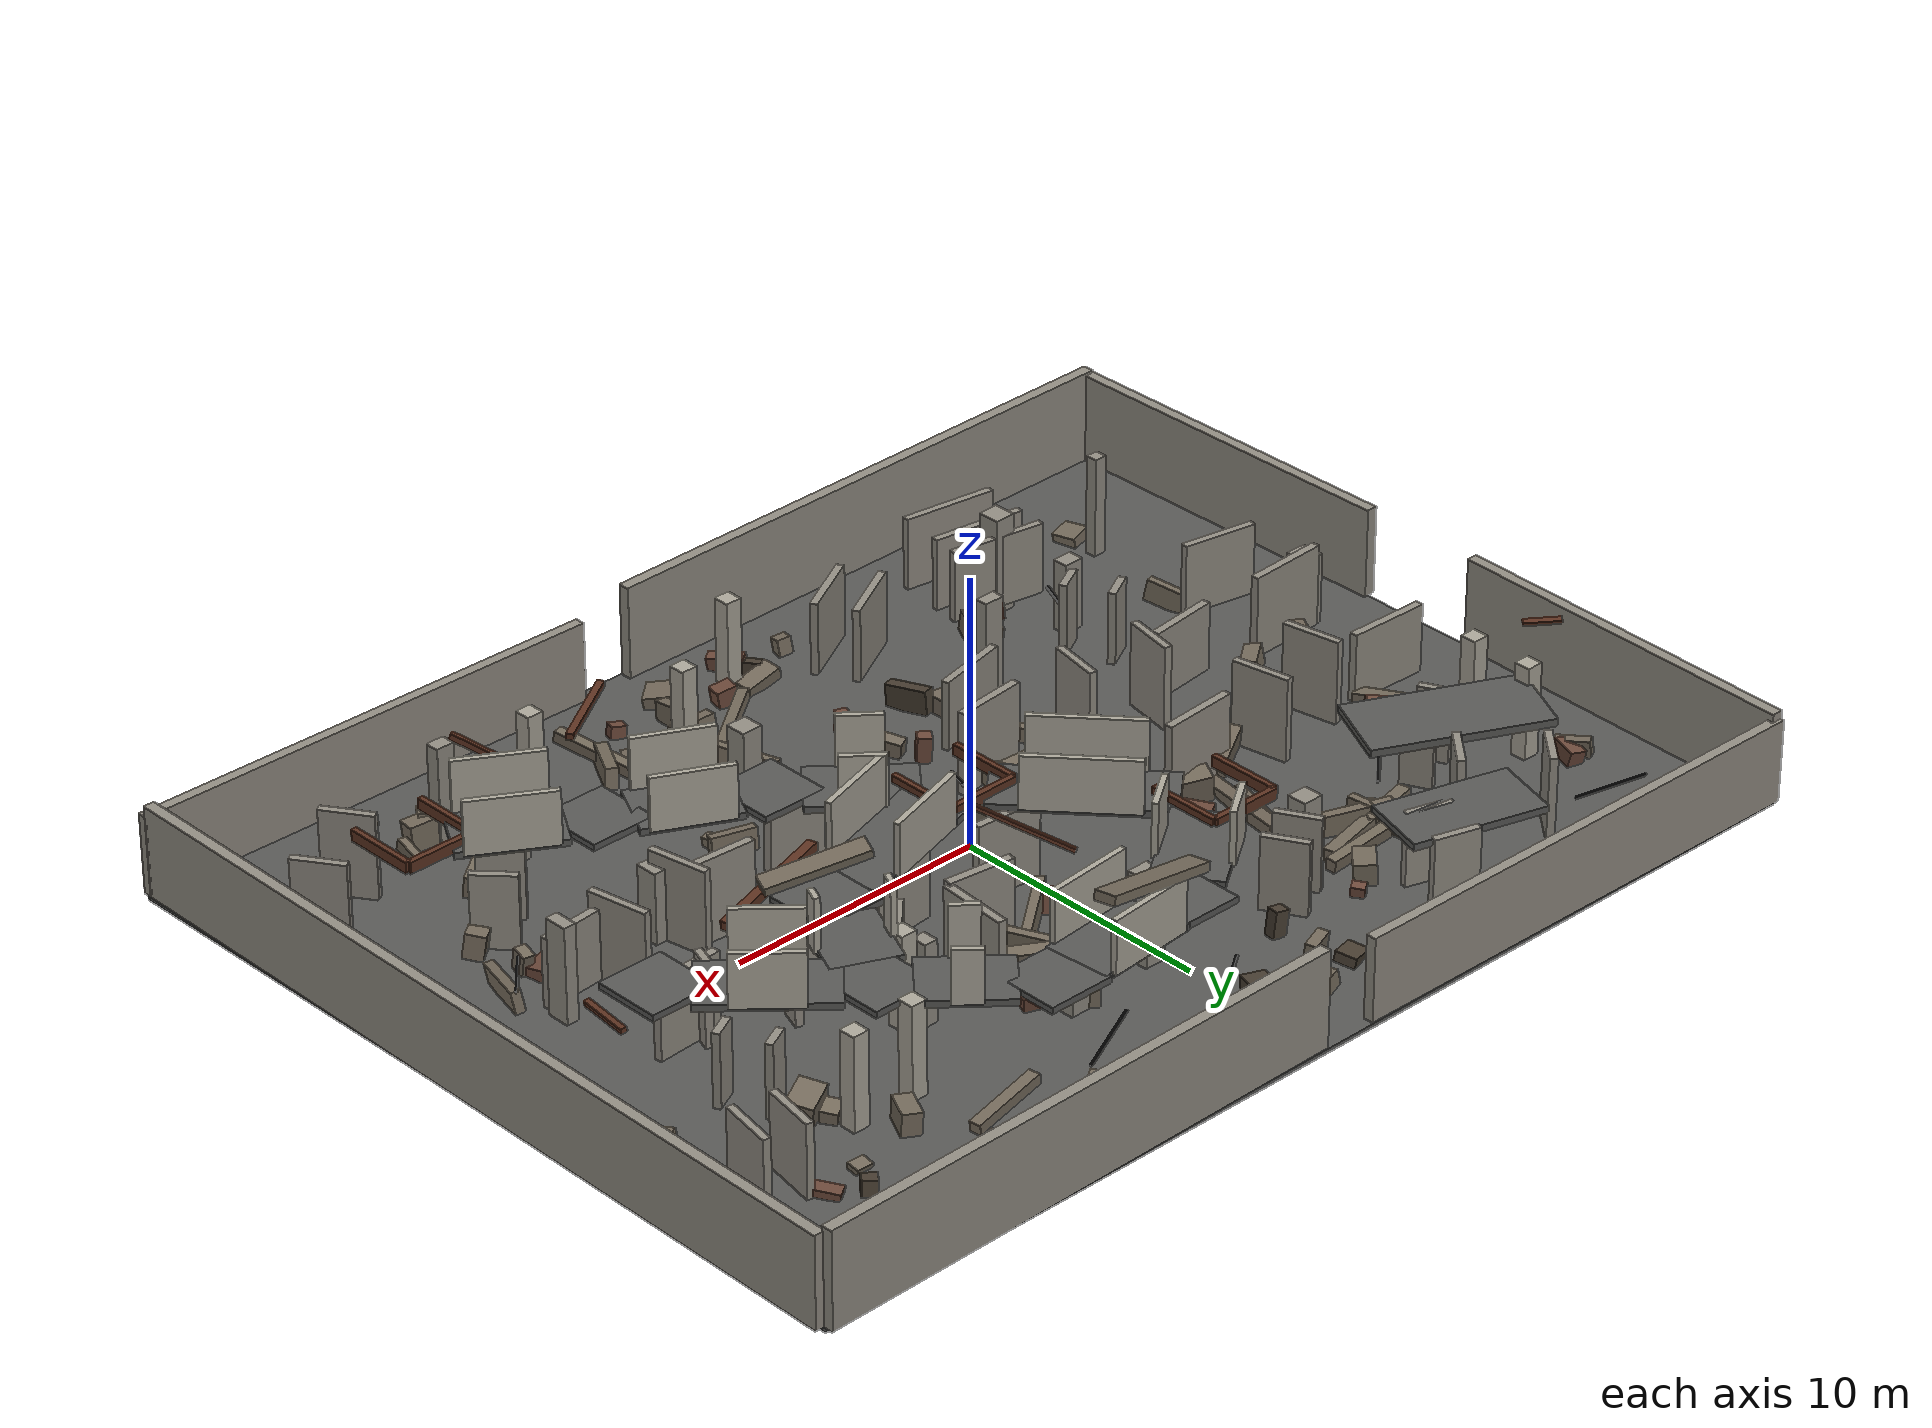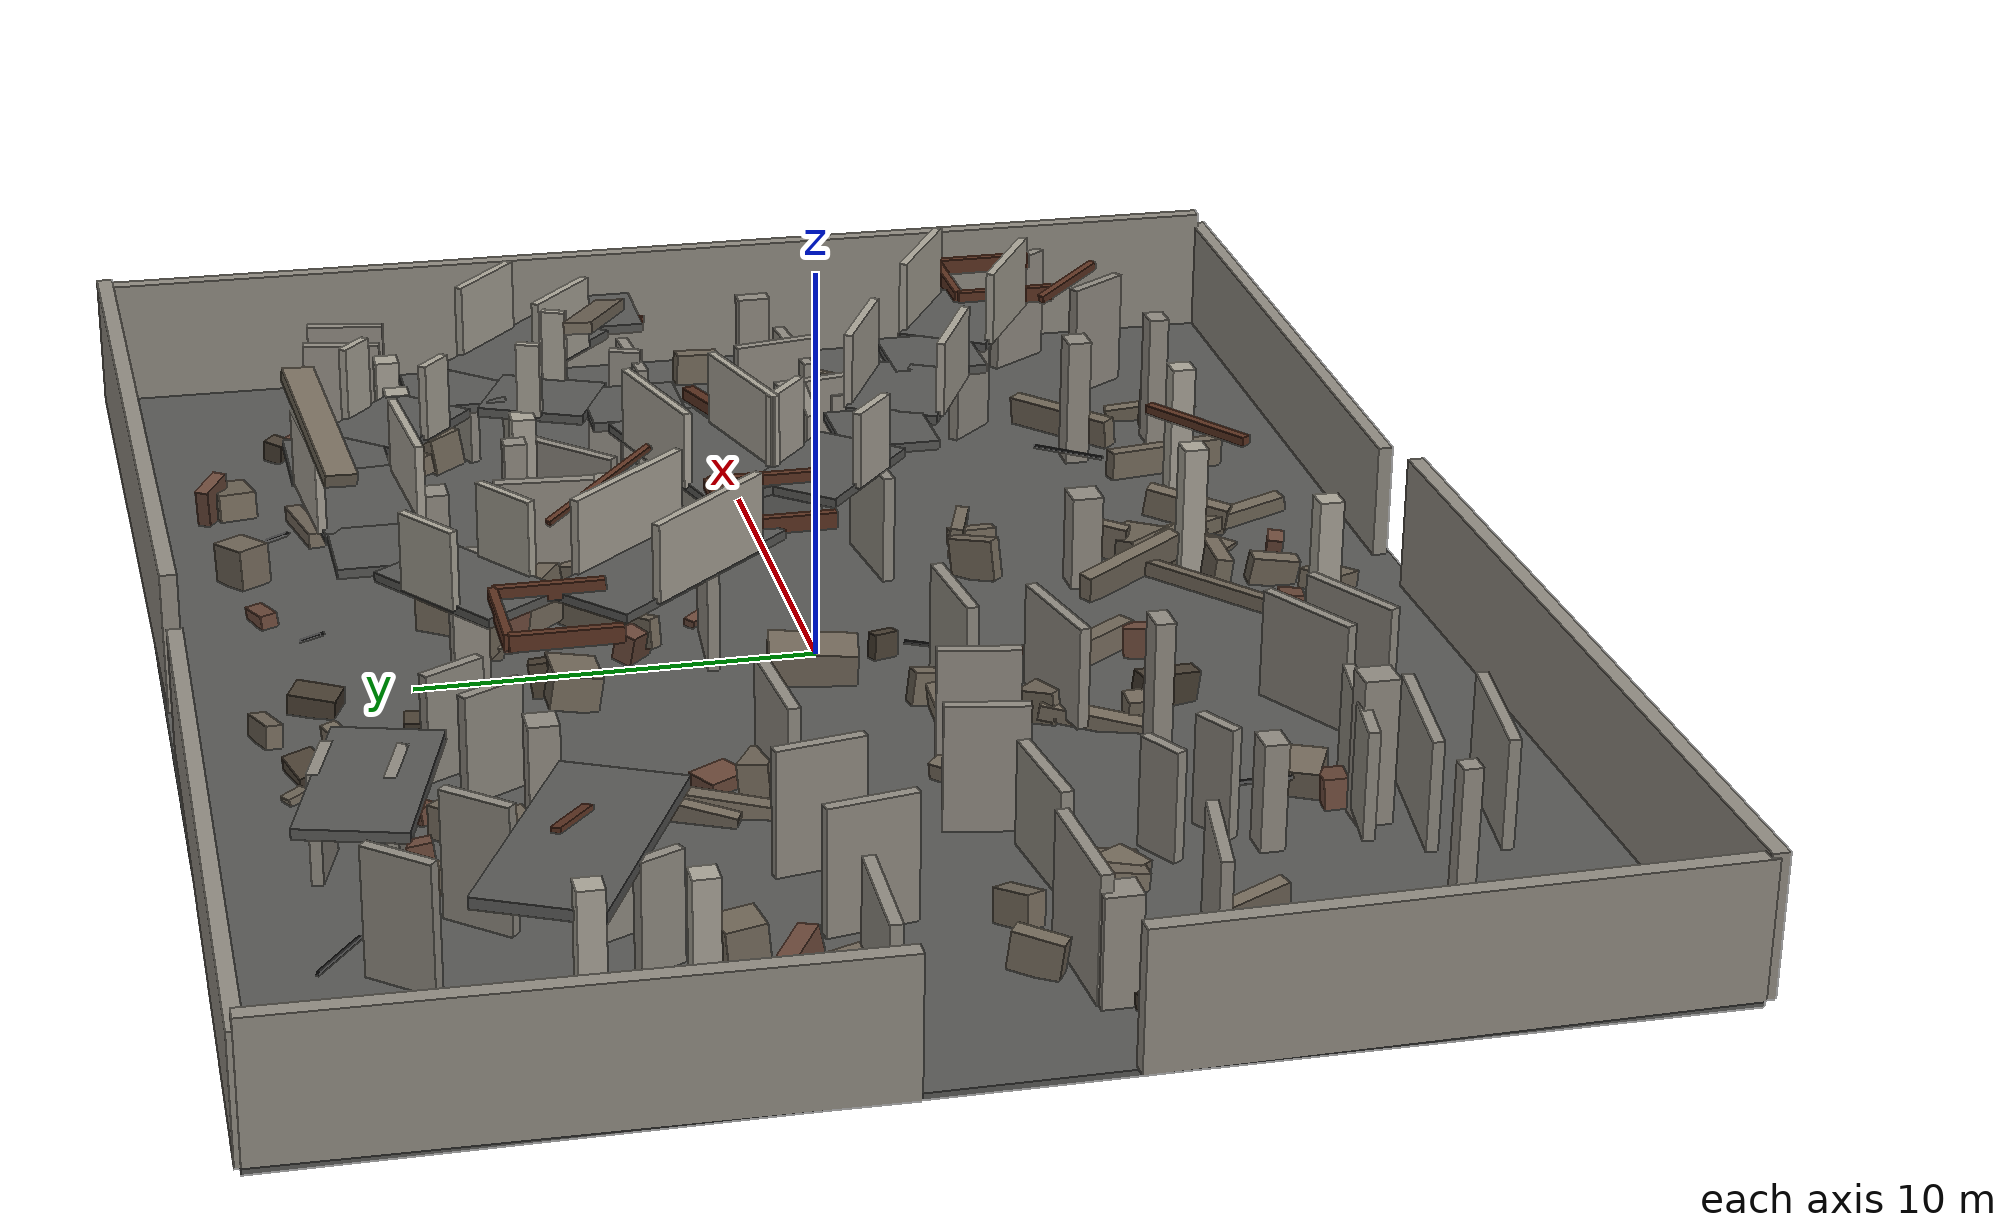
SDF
<?xml version="1.0" ?>
<sdf version="1.6">
  <world name="Ruins-Urban-01_complex">
    <gravity>0 0 -9.81</gravity>
    <scene>
      <ambient>0.42 0.41 0.38 1</ambient>
      <background>0.48 0.49 0.50 1</background>
      <shadows>true</shadows>

    </scene>
    <physics name="ode_physics" type="ode">
      <max_step_size>0.004</max_step_size>
      <real_time_factor>1</real_time_factor>
      <real_time_update_rate>250</real_time_update_rate>
    </physics>
    <light name="ceiling_area_light" type="point">
      <pose>-11 0 6.8 0 0 0</pose>
      <diffuse>0.68 0.65 0.58 1</diffuse>
      <specular>0.05 0.05 0.05 1</specular>
      <attenuation><range>38</range><constant>0.7</constant><linear>0.02</linear><quadratic>0.002</quadratic></attenuation>
    </light>
    <light name="damaged_east_light" type="point">
      <pose>12 5 5.8 0 0 0</pose>
      <diffuse>0.42 0.48 0.50 1</diffuse>
      <specular>0.03 0.03 0.03 1</specular>
      <attenuation><range>25</range><constant>0.8</constant><linear>0.04</linear><quadratic>0.004</quadratic></attenuation>
    </light>
    <light name="lower_south_light" type="point">
      <pose>-5 -10 3.0 0 0 0</pose>
      <diffuse>0.38 0.31 0.25 1</diffuse>
      <specular>0.02 0.02 0.02 1</specular>
      <attenuation><range>19</range><constant>0.9</constant><linear>0.05</linear><quadratic>0.006</quadratic></attenuation>
    </light>
    <include>
      <uri>model://ruins_urban_01_complex</uri>
    </include>
  </world>
</sdf>

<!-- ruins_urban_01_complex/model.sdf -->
<sdf version="1.6">
  <model name="ruins_urban_01_complex">
    <static>true</static>
    <link name="000_floor_slab">
      <pose>0.00000 0.00000 -0.08000 0.00000 0.00000 0.00000</pose>
      <visual name="visual">
        <geometry>
          <box><size>42.00000 32.00000 0.16000</size></box>
        </geometry>
          <material>
            <ambient>0.350 0.350 0.340 1</ambient>
            <diffuse>0.350 0.350 0.340 1</diffuse>
            <specular>0.03 0.03 0.03 1</specular>
          </material>
      </visual>
      <collision name="collision">
        <geometry>
          <box><size>42.00000 32.00000 0.16000</size></box>
        </geometry>
        <surface>
          <contact><collide_bitmask>0x01</collide_bitmask></contact>
          <friction>
            <ode><mu>1.0</mu><mu2>1.0</mu2></ode>
          </friction>
        </surface>
      </collision>
    </link>
    <link name="001_north_boundary_west">
      <pose>-11.50000 15.85000 1.55000 0.00000 0.00000 -0.01000</pose>
      <visual name="visual">
        <geometry>
          <box><size>19.00000 0.38000 3.10000</size></box>
        </geometry>
          <material>
            <ambient>0.580 0.560 0.520 1</ambient>
            <diffuse>0.580 0.560 0.520 1</diffuse>
            <specular>0.03 0.03 0.03 1</specular>
          </material>
      </visual>
      <collision name="collision">
        <geometry>
          <box><size>19.00000 0.38000 3.10000</size></box>
        </geometry>
        <surface>
          <contact><collide_bitmask>0x01</collide_bitmask></contact>
          <friction>
            <ode><mu>1.0</mu><mu2>1.0</mu2></ode>
          </friction>
        </surface>
      </collision>
    </link>
    <link name="002_north_boundary_east">
      <pose>10.50000 15.90000 1.80000 0.00000 0.00000 0.01500</pose>
      <visual name="visual">
        <geometry>
          <box><size>21.00000 0.42000 3.60000</size></box>
        </geometry>
          <material>
            <ambient>0.580 0.560 0.520 1</ambient>
            <diffuse>0.580 0.560 0.520 1</diffuse>
            <specular>0.03 0.03 0.03 1</specular>
          </material>
      </visual>
      <collision name="collision">
        <geometry>
          <box><size>21.00000 0.42000 3.60000</size></box>
        </geometry>
        <surface>
          <contact><collide_bitmask>0x01</collide_bitmask></contact>
          <friction>
            <ode><mu>1.0</mu><mu2>1.0</mu2></ode>
          </friction>
        </surface>
      </collision>
    </link>
    <link name="003_south_boundary_west">
      <pose>-10.00000 -15.90000 1.75000 0.00000 0.00000 0.01200</pose>
      <visual name="visual">
        <geometry>
          <box><size>22.00000 0.42000 3.50000</size></box>
        </geometry>
          <material>
            <ambient>0.580 0.560 0.520 1</ambient>
            <diffuse>0.580 0.560 0.520 1</diffuse>
            <specular>0.03 0.03 0.03 1</specular>
          </material>
      </visual>
      <collision name="collision">
        <geometry>
          <box><size>22.00000 0.42000 3.50000</size></box>
        </geometry>
        <surface>
          <contact><collide_bitmask>0x01</collide_bitmask></contact>
          <friction>
            <ode><mu>1.0</mu><mu2>1.0</mu2></ode>
          </friction>
        </surface>
      </collision>
    </link>
    <link name="004_south_boundary_east">
      <pose>12.00000 -15.85000 1.50000 0.00000 0.00000 -0.01800</pose>
      <visual name="visual">
        <geometry>
          <box><size>18.00000 0.38000 3.00000</size></box>
        </geometry>
          <material>
            <ambient>0.580 0.560 0.520 1</ambient>
            <diffuse>0.580 0.560 0.520 1</diffuse>
            <specular>0.03 0.03 0.03 1</specular>
          </material>
      </visual>
      <collision name="collision">
        <geometry>
          <box><size>18.00000 0.38000 3.00000</size></box>
        </geometry>
        <surface>
          <contact><collide_bitmask>0x01</collide_bitmask></contact>
          <friction>
            <ode><mu>1.0</mu><mu2>1.0</mu2></ode>
          </friction>
        </surface>
      </collision>
    </link>
    <link name="005_west_boundary_north">
      <pose>-20.95000 9.15000 1.70000 0.00000 0.00000 -0.02000</pose>
      <visual name="visual">
        <geometry>
          <box><size>0.42000 13.70000 3.40000</size></box>
        </geometry>
          <material>
            <ambient>0.580 0.560 0.520 1</ambient>
            <diffuse>0.580 0.560 0.520 1</diffuse>
            <specular>0.03 0.03 0.03 1</specular>
          </material>
      </visual>
      <collision name="collision">
        <geometry>
          <box><size>0.42000 13.70000 3.40000</size></box>
        </geometry>
        <surface>
          <contact><collide_bitmask>0x01</collide_bitmask></contact>
          <friction>
            <ode><mu>1.0</mu><mu2>1.0</mu2></ode>
          </friction>
        </surface>
      </collision>
    </link>
    <link name="006_west_boundary_south">
      <pose>-20.95000 -9.15000 1.70000 0.00000 0.00000 0.01500</pose>
      <visual name="visual">
        <geometry>
          <box><size>0.42000 13.70000 3.40000</size></box>
        </geometry>
          <material>
            <ambient>0.580 0.560 0.520 1</ambient>
            <diffuse>0.580 0.560 0.520 1</diffuse>
            <specular>0.03 0.03 0.03 1</specular>
          </material>
      </visual>
      <collision name="collision">
        <geometry>
          <box><size>0.42000 13.70000 3.40000</size></box>
        </geometry>
        <surface>
          <contact><collide_bitmask>0x01</collide_bitmask></contact>
          <friction>
            <ode><mu>1.0</mu><mu2>1.0</mu2></ode>
          </friction>
        </surface>
      </collision>
    </link>
    <link name="007_east_boundary">
      <pose>20.95000 0.00000 1.70000 0.00000 0.00000 -0.01000</pose>
      <visual name="visual">
        <geometry>
          <box><size>0.42000 31.80000 3.40000</size></box>
        </geometry>
          <material>
            <ambient>0.580 0.560 0.520 1</ambient>
            <diffuse>0.580 0.560 0.520 1</diffuse>
            <specular>0.03 0.03 0.03 1</specular>
          </material>
      </visual>
      <collision name="collision">
        <geometry>
          <box><size>0.42000 31.80000 3.40000</size></box>
        </geometry>
        <surface>
          <contact><collide_bitmask>0x01</collide_bitmask></contact>
          <friction>
            <ode><mu>1.0</mu><mu2>1.0</mu2></ode>
          </friction>
        </surface>
      </collision>
    </link>
    <link name="008_ground_corridor_g2_n1_left">
      <pose>-13.96680 1.73807 1.57500 0.00000 0.00000 1.74751</pose>
      <visual name="visual">
        <geometry>
          <box><size>2.18859 0.28000 3.15000</size></box>
        </geometry>
          <material>
            <ambient>0.580 0.560 0.520 1</ambient>
            <diffuse>0.580 0.560 0.520 1</diffuse>
            <specular>0.03 0.03 0.03 1</specular>
          </material>
      </visual>
      <collision name="collision">
        <geometry>
          <box><size>2.18859 0.28000 3.15000</size></box>
        </geometry>
        <surface>
          <contact><collide_bitmask>0x01</collide_bitmask></contact>
          <friction>
            <ode><mu>1.0</mu><mu2>1.0</mu2></ode>
          </friction>
        </surface>
      </collision>
    </link>
    <link name="009_ground_corridor_g2_n1_right">
      <pose>-11.03320 2.26193 1.57500 0.00000 0.00000 1.74751</pose>
      <visual name="visual">
        <geometry>
          <box><size>2.18859 0.28000 3.15000</size></box>
        </geometry>
          <material>
            <ambient>0.580 0.560 0.520 1</ambient>
            <diffuse>0.580 0.560 0.520 1</diffuse>
            <specular>0.03 0.03 0.03 1</specular>
          </material>
      </visual>
      <collision name="collision">
        <geometry>
          <box><size>2.18859 0.28000 3.15000</size></box>
        </geometry>
        <surface>
          <contact><collide_bitmask>0x01</collide_bitmask></contact>
          <friction>
            <ode><mu>1.0</mu><mu2>1.0</mu2></ode>
          </friction>
        </surface>
      </collision>
    </link>
    <link name="010_ground_corridor_n1_n2_left">
      <pose>-14.78097 6.52811 1.37500 0.00000 0.00000 2.01522</pose>
      <visual name="visual">
        <geometry>
          <box><size>1.15188 0.28000 2.75000</size></box>
        </geometry>
          <material>
            <ambient>0.580 0.560 0.520 1</ambient>
            <diffuse>0.580 0.560 0.520 1</diffuse>
            <specular>0.03 0.03 0.03 1</specular>
          </material>
      </visual>
      <collision name="collision">
        <geometry>
          <box><size>1.15188 0.28000 2.75000</size></box>
        </geometry>
        <surface>
          <contact><collide_bitmask>0x01</collide_bitmask></contact>
          <friction>
            <ode><mu>1.0</mu><mu2>1.0</mu2></ode>
          </friction>
        </surface>
      </collision>
    </link>
    <link name="011_ground_corridor_n1_n2_right">
      <pose>-13.21903 7.27189 1.37500 0.00000 0.00000 2.01522</pose>
      <visual name="visual">
        <geometry>
          <box><size>1.15188 0.28000 2.75000</size></box>
        </geometry>
          <material>
            <ambient>0.580 0.560 0.520 1</ambient>
            <diffuse>0.580 0.560 0.520 1</diffuse>
            <specular>0.03 0.03 0.03 1</specular>
          </material>
      </visual>
      <collision name="collision">
        <geometry>
          <box><size>1.15188 0.28000 2.75000</size></box>
        </geometry>
        <surface>
          <contact><collide_bitmask>0x01</collide_bitmask></contact>
          <friction>
            <ode><mu>1.0</mu><mu2>1.0</mu2></ode>
          </friction>
        </surface>
      </collision>
    </link>
    <link name="012_ground_corridor_n2_n3_left">
      <pose>-14.37134 11.98117 1.57500 0.00000 0.00000 0.85197</pose>
      <visual name="visual">
        <geometry>
          <box><size>1.81507 0.28000 3.15000</size></box>
        </geometry>
          <material>
            <ambient>0.580 0.560 0.520 1</ambient>
            <diffuse>0.580 0.560 0.520 1</diffuse>
            <specular>0.03 0.03 0.03 1</specular>
          </material>
      </visual>
      <collision name="collision">
        <geometry>
          <box><size>1.81507 0.28000 3.15000</size></box>
        </geometry>
        <surface>
          <contact><collide_bitmask>0x01</collide_bitmask></contact>
          <friction>
            <ode><mu>1.0</mu><mu2>1.0</mu2></ode>
          </friction>
        </surface>
      </collision>
    </link>
    <link name="013_ground_corridor_n2_n3_right">
      <pose>-12.12866 10.01883 1.57500 0.00000 0.00000 0.85197</pose>
      <visual name="visual">
        <geometry>
          <box><size>1.81507 0.28000 3.15000</size></box>
        </geometry>
          <material>
            <ambient>0.580 0.560 0.520 1</ambient>
            <diffuse>0.580 0.560 0.520 1</diffuse>
            <specular>0.03 0.03 0.03 1</specular>
          </material>
      </visual>
      <collision name="collision">
        <geometry>
          <box><size>1.81507 0.28000 3.15000</size></box>
        </geometry>
        <surface>
          <contact><collide_bitmask>0x01</collide_bitmask></contact>
          <friction>
            <ode><mu>1.0</mu><mu2>1.0</mu2></ode>
          </friction>
        </surface>
      </collision>
    </link>
    <link name="014_ground_corridor_n3_n4_left">
      <pose>-8.75144 13.07852 1.37500 0.00000 0.00000 -0.29146</pose>
      <visual name="visual">
        <geometry>
          <box><size>1.72015 0.28000 2.75000</size></box>
        </geometry>
          <material>
            <ambient>0.580 0.560 0.520 1</ambient>
            <diffuse>0.580 0.560 0.520 1</diffuse>
            <specular>0.03 0.03 0.03 1</specular>
          </material>
      </visual>
      <collision name="collision">
        <geometry>
          <box><size>1.72015 0.28000 2.75000</size></box>
        </geometry>
        <surface>
          <contact><collide_bitmask>0x01</collide_bitmask></contact>
          <friction>
            <ode><mu>1.0</mu><mu2>1.0</mu2></ode>
          </friction>
        </surface>
      </collision>
    </link>
    <link name="015_ground_corridor_n3_n4_right">
      <pose>-9.24856 11.42148 1.37500 0.00000 0.00000 -0.29146</pose>
      <visual name="visual">
        <geometry>
          <box><size>1.72015 0.28000 2.75000</size></box>
        </geometry>
          <material>
            <ambient>0.580 0.560 0.520 1</ambient>
            <diffuse>0.580 0.560 0.520 1</diffuse>
            <specular>0.03 0.03 0.03 1</specular>
          </material>
      </visual>
      <collision name="collision">
        <geometry>
          <box><size>1.72015 0.28000 2.75000</size></box>
        </geometry>
        <surface>
          <contact><collide_bitmask>0x01</collide_bitmask></contact>
          <friction>
            <ode><mu>1.0</mu><mu2>1.0</mu2></ode>
          </friction>
        </surface>
      </collision>
    </link>
    <link name="016_ground_corridor_n4_n5_left">
      <pose>-4.59438 9.61423 1.37500 0.00000 0.00000 -1.06370</pose>
      <visual name="visual">
        <geometry>
          <box><size>1.64782 0.28000 2.75000</size></box>
        </geometry>
          <material>
            <ambient>0.580 0.560 0.520 1</ambient>
            <diffuse>0.580 0.560 0.520 1</diffuse>
            <specular>0.03 0.03 0.03 1</specular>
          </material>
      </visual>
      <collision name="collision">
        <geometry>
          <box><size>1.64782 0.28000 2.75000</size></box>
        </geometry>
        <surface>
          <contact><collide_bitmask>0x01</collide_bitmask></contact>
          <friction>
            <ode><mu>1.0</mu><mu2>1.0</mu2></ode>
          </friction>
        </surface>
      </collision>
    </link>
    <link name="017_ground_corridor_n4_n5_right">
      <pose>-5.90562 8.88577 1.37500 0.00000 0.00000 -1.06370</pose>
      <visual name="visual">
        <geometry>
          <box><size>1.64782 0.28000 2.75000</size></box>
        </geometry>
          <material>
            <ambient>0.580 0.560 0.520 1</ambient>
            <diffuse>0.580 0.560 0.520 1</diffuse>
            <specular>0.03 0.03 0.03 1</specular>
          </material>
      </visual>
      <collision name="collision">
        <geometry>
          <box><size>1.64782 0.28000 2.75000</size></box>
        </geometry>
        <surface>
          <contact><collide_bitmask>0x01</collide_bitmask></contact>
          <friction>
            <ode><mu>1.0</mu><mu2>1.0</mu2></ode>
          </friction>
        </surface>
      </collision>
    </link>
    <link name="018_ground_corridor_g3_s1_left">
      <pose>-7.03491 -2.37131 1.57500 0.00000 0.00000 -1.75391</pose>
      <visual name="visual">
        <geometry>
          <box><size>1.99181 0.28000 3.15000</size></box>
        </geometry>
          <material>
            <ambient>0.580 0.560 0.520 1</ambient>
            <diffuse>0.580 0.560 0.520 1</diffuse>
            <specular>0.03 0.03 0.03 1</specular>
          </material>
      </visual>
      <collision name="collision">
        <geometry>
          <box><size>1.99181 0.28000 3.15000</size></box>
        </geometry>
        <surface>
          <contact><collide_bitmask>0x01</collide_bitmask></contact>
          <friction>
            <ode><mu>1.0</mu><mu2>1.0</mu2></ode>
          </friction>
        </surface>
      </collision>
    </link>
    <link name="019_ground_corridor_g3_s1_right">
      <pose>-9.96509 -1.82869 1.57500 0.00000 0.00000 -1.75391</pose>
      <visual name="visual">
        <geometry>
          <box><size>1.99181 0.28000 3.15000</size></box>
        </geometry>
          <material>
            <ambient>0.580 0.560 0.520 1</ambient>
            <diffuse>0.580 0.560 0.520 1</diffuse>
            <specular>0.03 0.03 0.03 1</specular>
          </material>
      </visual>
      <collision name="collision">
        <geometry>
          <box><size>1.99181 0.28000 3.15000</size></box>
        </geometry>
        <surface>
          <contact><collide_bitmask>0x01</collide_bitmask></contact>
          <friction>
            <ode><mu>1.0</mu><mu2>1.0</mu2></ode>
          </friction>
        </surface>
      </collision>
    </link>
    <link name="020_ground_corridor_s1_s2_left">
      <pose>-11.08900 -6.91112 1.37500 0.00000 0.00000 -2.64646</pose>
      <visual name="visual">
        <geometry>
          <box><size>1.18243 0.28000 2.75000</size></box>
        </geometry>
          <material>
            <ambient>0.580 0.560 0.520 1</ambient>
            <diffuse>0.580 0.560 0.520 1</diffuse>
            <specular>0.03 0.03 0.03 1</specular>
          </material>
      </visual>
      <collision name="collision">
        <geometry>
          <box><size>1.18243 0.28000 2.75000</size></box>
        </geometry>
        <surface>
          <contact><collide_bitmask>0x01</collide_bitmask></contact>
          <friction>
            <ode><mu>1.0</mu><mu2>1.0</mu2></ode>
          </friction>
        </surface>
      </collision>
    </link>
    <link name="021_ground_corridor_s1_s2_right">
      <pose>-11.91100 -5.38888 1.37500 0.00000 0.00000 -2.64646</pose>
      <visual name="visual">
        <geometry>
          <box><size>1.18243 0.28000 2.75000</size></box>
        </geometry>
          <material>
            <ambient>0.580 0.560 0.520 1</ambient>
            <diffuse>0.580 0.560 0.520 1</diffuse>
            <specular>0.03 0.03 0.03 1</specular>
          </material>
      </visual>
      <collision name="collision">
        <geometry>
          <box><size>1.18243 0.28000 2.75000</size></box>
        </geometry>
        <surface>
          <contact><collide_bitmask>0x01</collide_bitmask></contact>
          <friction>
            <ode><mu>1.0</mu><mu2>1.0</mu2></ode>
          </friction>
        </surface>
      </collision>
    </link>
    <link name="022_ground_corridor_s3_s4_left">
      <pose>-11.37767 -11.64369 1.37500 0.00000 0.00000 -0.14190</pose>
      <visual name="visual">
        <geometry>
          <box><size>3.57107 0.28000 2.75000</size></box>
        </geometry>
          <material>
            <ambient>0.580 0.560 0.520 1</ambient>
            <diffuse>0.580 0.560 0.520 1</diffuse>
            <specular>0.03 0.03 0.03 1</specular>
          </material>
      </visual>
      <collision name="collision">
        <geometry>
          <box><size>3.57107 0.28000 2.75000</size></box>
        </geometry>
        <surface>
          <contact><collide_bitmask>0x01</collide_bitmask></contact>
          <friction>
            <ode><mu>1.0</mu><mu2>1.0</mu2></ode>
          </friction>
        </surface>
      </collision>
    </link>
    <link name="023_ground_corridor_s3_s4_right">
      <pose>-11.62233 -13.35631 1.37500 0.00000 0.00000 -0.14190</pose>
      <visual name="visual">
        <geometry>
          <box><size>3.57107 0.28000 2.75000</size></box>
        </geometry>
          <material>
            <ambient>0.580 0.560 0.520 1</ambient>
            <diffuse>0.580 0.560 0.520 1</diffuse>
            <specular>0.03 0.03 0.03 1</specular>
          </material>
      </visual>
      <collision name="collision">
        <geometry>
          <box><size>3.57107 0.28000 2.75000</size></box>
        </geometry>
        <surface>
          <contact><collide_bitmask>0x01</collide_bitmask></contact>
          <friction>
            <ode><mu>1.0</mu><mu2>1.0</mu2></ode>
          </friction>
        </surface>
      </collision>
    </link>
    <link name="024_ground_corridor_s4_s5_left">
      <pose>-5.60914 -10.84158 1.37500 0.00000 0.00000 0.49935</pose>
      <visual name="visual">
        <geometry>
          <box><size>2.76498 0.28000 2.75000</size></box>
        </geometry>
          <material>
            <ambient>0.580 0.560 0.520 1</ambient>
            <diffuse>0.580 0.560 0.520 1</diffuse>
            <specular>0.03 0.03 0.03 1</specular>
          </material>
      </visual>
      <collision name="collision">
        <geometry>
          <box><size>2.76498 0.28000 2.75000</size></box>
        </geometry>
        <surface>
          <contact><collide_bitmask>0x01</collide_bitmask></contact>
          <friction>
            <ode><mu>1.0</mu><mu2>1.0</mu2></ode>
          </friction>
        </surface>
      </collision>
    </link>
    <link name="025_ground_corridor_s4_s5_right">
      <pose>-4.89086 -12.15842 1.37500 0.00000 0.00000 0.49935</pose>
      <visual name="visual">
        <geometry>
          <box><size>2.76498 0.28000 2.75000</size></box>
        </geometry>
          <material>
            <ambient>0.580 0.560 0.520 1</ambient>
            <diffuse>0.580 0.560 0.520 1</diffuse>
            <specular>0.03 0.03 0.03 1</specular>
          </material>
      </visual>
      <collision name="collision">
        <geometry>
          <box><size>2.76498 0.28000 2.75000</size></box>
        </geometry>
        <surface>
          <contact><collide_bitmask>0x01</collide_bitmask></contact>
          <friction>
            <ode><mu>1.0</mu><mu2>1.0</mu2></ode>
          </friction>
        </surface>
      </collision>
    </link>
    <link name="026_ground_corridor_g7_en1_left">
      <pose>10.85071 3.46194 1.57500 0.00000 0.00000 1.22007</pose>
      <visual name="visual">
        <geometry>
          <box><size>0.86578 0.28000 3.15000</size></box>
        </geometry>
          <material>
            <ambient>0.580 0.560 0.520 1</ambient>
            <diffuse>0.580 0.560 0.520 1</diffuse>
            <specular>0.03 0.03 0.03 1</specular>
          </material>
      </visual>
      <collision name="collision">
        <geometry>
          <box><size>0.86578 0.28000 3.15000</size></box>
        </geometry>
        <surface>
          <contact><collide_bitmask>0x01</collide_bitmask></contact>
          <friction>
            <ode><mu>1.0</mu><mu2>1.0</mu2></ode>
          </friction>
        </surface>
      </collision>
    </link>
    <link name="027_ground_corridor_g7_en1_right">
      <pose>13.64929 2.43806 1.57500 0.00000 0.00000 1.22007</pose>
      <visual name="visual">
        <geometry>
          <box><size>0.86578 0.28000 3.15000</size></box>
        </geometry>
          <material>
            <ambient>0.580 0.560 0.520 1</ambient>
            <diffuse>0.580 0.560 0.520 1</diffuse>
            <specular>0.03 0.03 0.03 1</specular>
          </material>
      </visual>
      <collision name="collision">
        <geometry>
          <box><size>0.86578 0.28000 3.15000</size></box>
        </geometry>
        <surface>
          <contact><collide_bitmask>0x01</collide_bitmask></contact>
          <friction>
            <ode><mu>1.0</mu><mu2>1.0</mu2></ode>
          </friction>
        </surface>
      </collision>
    </link>
    <link name="028_ground_corridor_en1_en2_left">
      <pose>14.61316 6.77368 1.37500 0.00000 0.00000 0.46365</pose>
      <visual name="visual">
        <geometry>
          <box><size>0.97214 0.28000 2.75000</size></box>
        </geometry>
          <material>
            <ambient>0.580 0.560 0.520 1</ambient>
            <diffuse>0.580 0.560 0.520 1</diffuse>
            <specular>0.03 0.03 0.03 1</specular>
          </material>
      </visual>
      <collision name="collision">
        <geometry>
          <box><size>0.97214 0.28000 2.75000</size></box>
        </geometry>
        <surface>
          <contact><collide_bitmask>0x01</collide_bitmask></contact>
          <friction>
            <ode><mu>1.0</mu><mu2>1.0</mu2></ode>
          </friction>
        </surface>
      </collision>
    </link>
    <link name="029_ground_corridor_en1_en2_right">
      <pose>15.38684 5.22632 1.37500 0.00000 0.00000 0.46365</pose>
      <visual name="visual">
        <geometry>
          <box><size>0.97214 0.28000 2.75000</size></box>
        </geometry>
          <material>
            <ambient>0.580 0.560 0.520 1</ambient>
            <diffuse>0.580 0.560 0.520 1</diffuse>
            <specular>0.03 0.03 0.03 1</specular>
          </material>
      </visual>
      <collision name="collision">
        <geometry>
          <box><size>0.97214 0.28000 2.75000</size></box>
        </geometry>
        <surface>
          <contact><collide_bitmask>0x01</collide_bitmask></contact>
          <friction>
            <ode><mu>1.0</mu><mu2>1.0</mu2></ode>
          </friction>
        </surface>
      </collision>
    </link>
    <link name="030_ground_corridor_en2_dead_ne_left">
      <pose>16.76210 9.88416 1.37500 0.00000 0.00000 1.39094</pose>
      <visual name="visual">
        <geometry>
          <box><size>2.09017 0.28000 2.75000</size></box>
        </geometry>
          <material>
            <ambient>0.580 0.560 0.520 1</ambient>
            <diffuse>0.580 0.560 0.520 1</diffuse>
            <specular>0.03 0.03 0.03 1</specular>
          </material>
      </visual>
      <collision name="collision">
        <geometry>
          <box><size>2.09017 0.28000 2.75000</size></box>
        </geometry>
        <surface>
          <contact><collide_bitmask>0x01</collide_bitmask></contact>
          <friction>
            <ode><mu>1.0</mu><mu2>1.0</mu2></ode>
          </friction>
        </surface>
      </collision>
    </link>
    <link name="031_ground_corridor_en2_dead_ne_right">
      <pose>18.23790 9.61584 1.37500 0.00000 0.00000 1.39094</pose>
      <visual name="visual">
        <geometry>
          <box><size>2.09017 0.28000 2.75000</size></box>
        </geometry>
          <material>
            <ambient>0.580 0.560 0.520 1</ambient>
            <diffuse>0.580 0.560 0.520 1</diffuse>
            <specular>0.03 0.03 0.03 1</specular>
          </material>
      </visual>
      <collision name="collision">
        <geometry>
          <box><size>2.09017 0.28000 2.75000</size></box>
        </geometry>
        <surface>
          <contact><collide_bitmask>0x01</collide_bitmask></contact>
          <friction>
            <ode><mu>1.0</mu><mu2>1.0</mu2></ode>
          </friction>
        </surface>
      </collision>
    </link>
    <link name="032_ground_corridor_g7_es1_left">
      <pose>13.46759 -1.69253 1.57500 0.00000 0.00000 -1.39713</pose>
      <visual name="visual">
        <geometry>
          <box><size>2.28705 0.28000 3.15000</size></box>
        </geometry>
          <material>
            <ambient>0.580 0.560 0.520 1</ambient>
            <diffuse>0.580 0.560 0.520 1</diffuse>
            <specular>0.03 0.03 0.03 1</specular>
          </material>
      </visual>
      <collision name="collision">
        <geometry>
          <box><size>2.28705 0.28000 3.15000</size></box>
        </geometry>
        <surface>
          <contact><collide_bitmask>0x01</collide_bitmask></contact>
          <friction>
            <ode><mu>1.0</mu><mu2>1.0</mu2></ode>
          </friction>
        </surface>
      </collision>
    </link>
    <link name="033_ground_corridor_g7_es1_right">
      <pose>10.53241 -2.20747 1.57500 0.00000 0.00000 -1.39713</pose>
      <visual name="visual">
        <geometry>
          <box><size>2.28705 0.28000 3.15000</size></box>
        </geometry>
          <material>
            <ambient>0.580 0.560 0.520 1</ambient>
            <diffuse>0.580 0.560 0.520 1</diffuse>
            <specular>0.03 0.03 0.03 1</specular>
          </material>
      </visual>
      <collision name="collision">
        <geometry>
          <box><size>2.28705 0.28000 3.15000</size></box>
        </geometry>
        <surface>
          <contact><collide_bitmask>0x01</collide_bitmask></contact>
          <friction>
            <ode><mu>1.0</mu><mu2>1.0</mu2></ode>
          </friction>
        </surface>
      </collision>
    </link>
    <link name="034_ground_corridor_es1_es2_left">
      <pose>14.87840 -6.05557 1.37500 0.00000 0.00000 -0.81317</pose>
      <visual name="visual">
        <geometry>
          <box><size>1.59313 0.28000 2.75000</size></box>
        </geometry>
          <material>
            <ambient>0.580 0.560 0.520 1</ambient>
            <diffuse>0.580 0.560 0.520 1</diffuse>
            <specular>0.03 0.03 0.03 1</specular>
          </material>
      </visual>
      <collision name="collision">
        <geometry>
          <box><size>1.59313 0.28000 2.75000</size></box>
        </geometry>
        <surface>
          <contact><collide_bitmask>0x01</collide_bitmask></contact>
          <friction>
            <ode><mu>1.0</mu><mu2>1.0</mu2></ode>
          </friction>
        </surface>
      </collision>
    </link>
    <link name="035_ground_corridor_es1_es2_right">
      <pose>13.62160 -7.24443 1.37500 0.00000 0.00000 -0.81317</pose>
      <visual name="visual">
        <geometry>
          <box><size>1.59313 0.28000 2.75000</size></box>
        </geometry>
          <material>
            <ambient>0.580 0.560 0.520 1</ambient>
            <diffuse>0.580 0.560 0.520 1</diffuse>
            <specular>0.03 0.03 0.03 1</specular>
          </material>
      </visual>
      <collision name="collision">
        <geometry>
          <box><size>1.59313 0.28000 2.75000</size></box>
        </geometry>
        <surface>
          <contact><collide_bitmask>0x01</collide_bitmask></contact>
          <friction>
            <ode><mu>1.0</mu><mu2>1.0</mu2></ode>
          </friction>
        </surface>
      </collision>
    </link>
    <link name="036_ground_corridor_es2_dead_se_left">
      <pose>18.73975 -9.92350 1.57500 0.00000 0.00000 -0.98279</pose>
      <visual name="visual">
        <geometry>
          <box><size>1.90833 0.28000 3.15000</size></box>
        </geometry>
          <material>
            <ambient>0.580 0.560 0.520 1</ambient>
            <diffuse>0.580 0.560 0.520 1</diffuse>
            <specular>0.03 0.03 0.03 1</specular>
          </material>
      </visual>
      <collision name="collision">
        <geometry>
          <box><size>1.90833 0.28000 3.15000</size></box>
        </geometry>
        <surface>
          <contact><collide_bitmask>0x01</collide_bitmask></contact>
          <friction>
            <ode><mu>1.0</mu><mu2>1.0</mu2></ode>
          </friction>
        </surface>
      </collision>
    </link>
    <link name="037_ground_corridor_es2_dead_se_right">
      <pose>16.26025 -11.57650 1.57500 0.00000 0.00000 -0.98279</pose>
      <visual name="visual">
        <geometry>
          <box><size>1.90833 0.28000 3.15000</size></box>
        </geometry>
          <material>
            <ambient>0.580 0.560 0.520 1</ambient>
            <diffuse>0.580 0.560 0.520 1</diffuse>
            <specular>0.03 0.03 0.03 1</specular>
          </material>
      </visual>
      <collision name="collision">
        <geometry>
          <box><size>1.90833 0.28000 3.15000</size></box>
        </geometry>
        <surface>
          <contact><collide_bitmask>0x01</collide_bitmask></contact>
          <friction>
            <ode><mu>1.0</mu><mu2>1.0</mu2></ode>
          </friction>
        </surface>
      </collision>
    </link>
    <link name="038_spine_broken_panel_00">
      <pose>-17.05000 2.20000 1.30000 0.00000 0.00000 -0.03225</pose>
      <visual name="visual">
        <geometry>
          <box><size>3.10161 0.30000 2.60000</size></box>
        </geometry>
          <material>
            <ambient>0.580 0.560 0.520 1</ambient>
            <diffuse>0.580 0.560 0.520 1</diffuse>
            <specular>0.03 0.03 0.03 1</specular>
          </material>
      </visual>
      <collision name="collision">
        <geometry>
          <box><size>3.10161 0.30000 2.60000</size></box>
        </geometry>
        <surface>
          <contact><collide_bitmask>0x01</collide_bitmask></contact>
          <friction>
            <ode><mu>1.0</mu><mu2>1.0</mu2></ode>
          </friction>
        </surface>
      </collision>
    </link>
    <link name="039_spine_broken_panel_02">
      <pose>-7.75000 2.55000 1.55000 0.00000 0.00000 0.06886</pose>
      <visual name="visual">
        <geometry>
          <box><size>2.90689 0.30000 3.10000</size></box>
        </geometry>
          <material>
            <ambient>0.580 0.560 0.520 1</ambient>
            <diffuse>0.580 0.560 0.520 1</diffuse>
            <specular>0.03 0.03 0.03 1</specular>
          </material>
      </visual>
      <collision name="collision">
        <geometry>
          <box><size>2.90689 0.30000 3.10000</size></box>
        </geometry>
        <surface>
          <contact><collide_bitmask>0x01</collide_bitmask></contact>
          <friction>
            <ode><mu>1.0</mu><mu2>1.0</mu2></ode>
          </friction>
        </surface>
      </collision>
    </link>
    <link name="040_spine_broken_panel_04">
      <pose>0.85000 2.55000 1.42500 0.00000 0.00000 -0.07983</pose>
      <visual name="visual">
        <geometry>
          <box><size>2.50799 0.30000 2.85000</size></box>
        </geometry>
          <material>
            <ambient>0.580 0.560 0.520 1</ambient>
            <diffuse>0.580 0.560 0.520 1</diffuse>
            <specular>0.03 0.03 0.03 1</specular>
          </material>
      </visual>
      <collision name="collision">
        <geometry>
          <box><size>2.50799 0.30000 2.85000</size></box>
        </geometry>
        <surface>
          <contact><collide_bitmask>0x01</collide_bitmask></contact>
          <friction>
            <ode><mu>1.0</mu><mu2>1.0</mu2></ode>
          </friction>
        </surface>
      </collision>
    </link>
    <link name="041_spine_broken_panel_05">
      <pose>5.00000 2.05000 1.55000 0.00000 0.00000 0.08314</pose>
      <visual name="visual">
        <geometry>
          <box><size>2.40832 0.30000 3.10000</size></box>
        </geometry>
          <material>
            <ambient>0.580 0.560 0.520 1</ambient>
            <diffuse>0.580 0.560 0.520 1</diffuse>
            <specular>0.03 0.03 0.03 1</specular>
          </material>
      </visual>
      <collision name="collision">
        <geometry>
          <box><size>2.40832 0.30000 3.10000</size></box>
        </geometry>
        <surface>
          <contact><collide_bitmask>0x01</collide_bitmask></contact>
          <friction>
            <ode><mu>1.0</mu><mu2>1.0</mu2></ode>
          </friction>
        </surface>
      </collision>
    </link>
    <link name="042_spine_broken_panel_06">
      <pose>8.90000 2.47500 1.30000 0.00000 0.00000 -0.10379</pose>
      <visual name="visual">
        <geometry>
          <box><size>2.41299 0.30000 2.60000</size></box>
        </geometry>
          <material>
            <ambient>0.580 0.560 0.520 1</ambient>
            <diffuse>0.580 0.560 0.520 1</diffuse>
            <specular>0.03 0.03 0.03 1</specular>
          </material>
      </visual>
      <collision name="collision">
        <geometry>
          <box><size>2.41299 0.30000 2.60000</size></box>
        </geometry>
        <surface>
          <contact><collide_bitmask>0x01</collide_bitmask></contact>
          <friction>
            <ode><mu>1.0</mu><mu2>1.0</mu2></ode>
          </friction>
        </surface>
      </collision>
    </link>
    <link name="043_spine_broken_panel_07">
      <pose>14.10000 2.17500 1.42500 0.00000 0.00000 0.05763</pose>
      <visual name="visual">
        <geometry>
          <box><size>2.60432 0.30000 2.85000</size></box>
        </geometry>
          <material>
            <ambient>0.580 0.560 0.520 1</ambient>
            <diffuse>0.580 0.560 0.520 1</diffuse>
            <specular>0.03 0.03 0.03 1</specular>
          </material>
      </visual>
      <collision name="collision">
        <geometry>
          <box><size>2.60432 0.30000 2.85000</size></box>
        </geometry>
        <surface>
          <contact><collide_bitmask>0x01</collide_bitmask></contact>
          <friction>
            <ode><mu>1.0</mu><mu2>1.0</mu2></ode>
          </friction>
        </surface>
      </collision>
    </link>
    <link name="044_spine_broken_panel_08">
      <pose>-16.75000 -2.22500 1.55000 0.00000 0.00000 0.04835</pose>
      <visual name="visual">
        <geometry>
          <box><size>3.10363 0.30000 3.10000</size></box>
        </geometry>
          <material>
            <ambient>0.580 0.560 0.520 1</ambient>
            <diffuse>0.580 0.560 0.520 1</diffuse>
            <specular>0.03 0.03 0.03 1</specular>
          </material>
      </visual>
      <collision name="collision">
        <geometry>
          <box><size>3.10363 0.30000 3.10000</size></box>
        </geometry>
        <surface>
          <contact><collide_bitmask>0x01</collide_bitmask></contact>
          <friction>
            <ode><mu>1.0</mu><mu2>1.0</mu2></ode>
          </friction>
        </surface>
      </collision>
    </link>
    <link name="045_spine_broken_panel_09">
      <pose>-12.15000 -2.60000 1.30000 0.00000 0.00000 0.11066</pose>
      <visual name="visual">
        <geometry>
          <box><size>2.71662 0.30000 2.60000</size></box>
        </geometry>
          <material>
            <ambient>0.580 0.560 0.520 1</ambient>
            <diffuse>0.580 0.560 0.520 1</diffuse>
            <specular>0.03 0.03 0.03 1</specular>
          </material>
      </visual>
      <collision name="collision">
        <geometry>
          <box><size>2.71662 0.30000 2.60000</size></box>
        </geometry>
        <surface>
          <contact><collide_bitmask>0x01</collide_bitmask></contact>
          <friction>
            <ode><mu>1.0</mu><mu2>1.0</mu2></ode>
          </friction>
        </surface>
      </collision>
    </link>
    <link name="046_spine_broken_panel_11">
      <pose>-3.35000 -2.67500 1.55000 0.00000 0.00000 0.09233</pose>
      <visual name="visual">
        <geometry>
          <box><size>2.71155 0.30000 3.10000</size></box>
        </geometry>
          <material>
            <ambient>0.580 0.560 0.520 1</ambient>
            <diffuse>0.580 0.560 0.520 1</diffuse>
            <specular>0.03 0.03 0.03 1</specular>
          </material>
      </visual>
      <collision name="collision">
        <geometry>
          <box><size>2.71155 0.30000 3.10000</size></box>
        </geometry>
        <surface>
          <contact><collide_bitmask>0x01</collide_bitmask></contact>
          <friction>
            <ode><mu>1.0</mu><mu2>1.0</mu2></ode>
          </friction>
        </surface>
      </collision>
    </link>
    <link name="047_spine_broken_panel_13">
      <pose>5.30000 -2.60000 1.42500 0.00000 0.00000 0.11488</pose>
      <visual name="visual">
        <geometry>
          <box><size>2.61725 0.30000 2.85000</size></box>
        </geometry>
          <material>
            <ambient>0.580 0.560 0.520 1</ambient>
            <diffuse>0.580 0.560 0.520 1</diffuse>
            <specular>0.03 0.03 0.03 1</specular>
          </material>
      </visual>
      <collision name="collision">
        <geometry>
          <box><size>2.61725 0.30000 2.85000</size></box>
        </geometry>
        <surface>
          <contact><collide_bitmask>0x01</collide_bitmask></contact>
          <friction>
            <ode><mu>1.0</mu><mu2>1.0</mu2></ode>
          </friction>
        </surface>
      </collision>
    </link>
    <link name="048_spine_broken_panel_14">
      <pose>9.20000 -1.67500 1.55000 0.00000 0.00000 -0.06242</pose>
      <visual name="visual">
        <geometry>
          <box><size>2.40468 0.30000 3.10000</size></box>
        </geometry>
          <material>
            <ambient>0.580 0.560 0.520 1</ambient>
            <diffuse>0.580 0.560 0.520 1</diffuse>
            <specular>0.03 0.03 0.03 1</specular>
          </material>
      </visual>
      <collision name="collision">
        <geometry>
          <box><size>2.40468 0.30000 3.10000</size></box>
        </geometry>
        <surface>
          <contact><collide_bitmask>0x01</collide_bitmask></contact>
          <friction>
            <ode><mu>1.0</mu><mu2>1.0</mu2></ode>
          </friction>
        </surface>
      </collision>
    </link>
    <link name="049_spine_broken_panel_15">
      <pose>14.50000 -2.42500 1.30000 0.00000 0.00000 0.08314</pose>
      <visual name="visual">
        <geometry>
          <box><size>3.01040 0.30000 2.60000</size></box>
        </geometry>
          <material>
            <ambient>0.580 0.560 0.520 1</ambient>
            <diffuse>0.580 0.560 0.520 1</diffuse>
            <specular>0.03 0.03 0.03 1</specular>
          </material>
      </visual>
      <collision name="collision">
        <geometry>
          <box><size>3.01040 0.30000 2.60000</size></box>
        </geometry>
        <surface>
          <contact><collide_bitmask>0x01</collide_bitmask></contact>
          <friction>
            <ode><mu>1.0</mu><mu2>1.0</mu2></ode>
          </friction>
        </surface>
      </collision>
    </link>
    <link name="050_utility_ceiling_01">
      <pose>-13.80000 8.00000 2.72000 0.00000 0.00000 -0.45000</pose>
      <visual name="visual">
        <geometry>
          <box><size>6.50000 3.00000 0.28000</size></box>
        </geometry>
          <material>
            <ambient>0.350 0.350 0.340 1</ambient>
            <diffuse>0.350 0.350 0.340 1</diffuse>
            <specular>0.03 0.03 0.03 1</specular>
          </material>
      </visual>
      <collision name="collision">
        <geometry>
          <box><size>6.50000 3.00000 0.28000</size></box>
        </geometry>
        <surface>
          <contact><collide_bitmask>0x01</collide_bitmask></contact>
          <friction>
            <ode><mu>1.0</mu><mu2>1.0</mu2></ode>
          </friction>
        </surface>
      </collision>
    </link>
    <link name="051_utility_ceiling_02">
      <pose>-10.00000 12.10000 2.62000 0.00000 0.00000 -0.28000</pose>
      <visual name="visual">
        <geometry>
          <box><size>5.00000 2.60000 0.26000</size></box>
        </geometry>
          <material>
            <ambient>0.350 0.350 0.340 1</ambient>
            <diffuse>0.350 0.350 0.340 1</diffuse>
            <specular>0.03 0.03 0.03 1</specular>
          </material>
      </visual>
      <collision name="collision">
        <geometry>
          <box><size>5.00000 2.60000 0.26000</size></box>
        </geometry>
        <surface>
          <contact><collide_bitmask>0x01</collide_bitmask></contact>
          <friction>
            <ode><mu>1.0</mu><mu2>1.0</mu2></ode>
          </friction>
        </surface>
      </collision>
    </link>
    <link name="052_fixed_column_00">
      <pose>-17.20000 6.00000 1.75000 0.00000 0.00000 0.00000</pose>
      <visual name="visual">
        <geometry>
          <box><size>0.62000 0.62000 3.50000</size></box>
        </geometry>
          <material>
            <ambient>0.680 0.660 0.610 1</ambient>
            <diffuse>0.680 0.660 0.610 1</diffuse>
            <specular>0.03 0.03 0.03 1</specular>
          </material>
      </visual>
      <collision name="collision">
        <geometry>
          <box><size>0.62000 0.62000 3.50000</size></box>
        </geometry>
        <surface>
          <contact><collide_bitmask>0x01</collide_bitmask></contact>
          <friction>
            <ode><mu>1.0</mu><mu2>1.0</mu2></ode>
          </friction>
        </surface>
      </collision>
    </link>
    <link name="053_fixed_column_01">
      <pose>-17.20000 8.40000 1.75000 0.00000 0.00000 0.00000</pose>
      <visual name="visual">
        <geometry>
          <box><size>0.62000 0.62000 3.50000</size></box>
        </geometry>
          <material>
            <ambient>0.680 0.660 0.610 1</ambient>
            <diffuse>0.680 0.660 0.610 1</diffuse>
            <specular>0.03 0.03 0.03 1</specular>
          </material>
      </visual>
      <collision name="collision">
        <geometry>
          <box><size>0.62000 0.62000 3.50000</size></box>
        </geometry>
        <surface>
          <contact><collide_bitmask>0x01</collide_bitmask></contact>
          <friction>
            <ode><mu>1.0</mu><mu2>1.0</mu2></ode>
          </friction>
        </surface>
      </collision>
    </link>
    <link name="054_fixed_column_03">
      <pose>8.60000 6.00000 1.75000 0.00000 0.00000 0.00000</pose>
      <visual name="visual">
        <geometry>
          <box><size>0.62000 0.62000 3.50000</size></box>
        </geometry>
          <material>
            <ambient>0.680 0.660 0.610 1</ambient>
            <diffuse>0.680 0.660 0.610 1</diffuse>
            <specular>0.03 0.03 0.03 1</specular>
          </material>
      </visual>
      <collision name="collision">
        <geometry>
          <box><size>0.62000 0.62000 3.50000</size></box>
        </geometry>
        <surface>
          <contact><collide_bitmask>0x01</collide_bitmask></contact>
          <friction>
            <ode><mu>1.0</mu><mu2>1.0</mu2></ode>
          </friction>
        </surface>
      </collision>
    </link>
    <link name="055_fixed_column_07">
      <pose>11.00000 9.00000 1.75000 0.00000 0.00000 0.00000</pose>
      <visual name="visual">
        <geometry>
          <box><size>0.62000 0.62000 3.50000</size></box>
        </geometry>
          <material>
            <ambient>0.680 0.660 0.610 1</ambient>
            <diffuse>0.680 0.660 0.610 1</diffuse>
            <specular>0.03 0.03 0.03 1</specular>
          </material>
      </visual>
      <collision name="collision">
        <geometry>
          <box><size>0.62000 0.62000 3.50000</size></box>
        </geometry>
        <surface>
          <contact><collide_bitmask>0x01</collide_bitmask></contact>
          <friction>
            <ode><mu>1.0</mu><mu2>1.0</mu2></ode>
          </friction>
        </surface>
      </collision>
    </link>
    <link name="056_fixed_column_08">
      <pose>13.40000 9.00000 1.75000 0.00000 0.00000 0.00000</pose>
      <visual name="visual">
        <geometry>
          <box><size>0.62000 0.62000 3.50000</size></box>
        </geometry>
          <material>
            <ambient>0.680 0.660 0.610 1</ambient>
            <diffuse>0.680 0.660 0.610 1</diffuse>
            <specular>0.03 0.03 0.03 1</specular>
          </material>
      </visual>
      <collision name="collision">
        <geometry>
          <box><size>0.62000 0.62000 3.50000</size></box>
        </geometry>
        <surface>
          <contact><collide_bitmask>0x01</collide_bitmask></contact>
          <friction>
            <ode><mu>1.0</mu><mu2>1.0</mu2></ode>
          </friction>
        </surface>
      </collision>
    </link>
    <link name="057_fixed_column_09">
      <pose>-1.00000 -12.80000 1.75000 0.00000 0.00000 0.00000</pose>
      <visual name="visual">
        <geometry>
          <box><size>0.62000 0.62000 3.50000</size></box>
        </geometry>
          <material>
            <ambient>0.680 0.660 0.610 1</ambient>
            <diffuse>0.680 0.660 0.610 1</diffuse>
            <specular>0.03 0.03 0.03 1</specular>
          </material>
      </visual>
      <collision name="collision">
        <geometry>
          <box><size>0.62000 0.62000 3.50000</size></box>
        </geometry>
        <surface>
          <contact><collide_bitmask>0x01</collide_bitmask></contact>
          <friction>
            <ode><mu>1.0</mu><mu2>1.0</mu2></ode>
          </friction>
        </surface>
      </collision>
    </link>
    <link name="058_fixed_column_10">
      <pose>3.00000 -10.50000 1.75000 0.00000 0.00000 0.00000</pose>
      <visual name="visual">
        <geometry>
          <box><size>0.62000 0.62000 3.50000</size></box>
        </geometry>
          <material>
            <ambient>0.680 0.660 0.610 1</ambient>
            <diffuse>0.680 0.660 0.610 1</diffuse>
            <specular>0.03 0.03 0.03 1</specular>
          </material>
      </visual>
      <collision name="collision">
        <geometry>
          <box><size>0.62000 0.62000 3.50000</size></box>
        </geometry>
        <surface>
          <contact><collide_bitmask>0x01</collide_bitmask></contact>
          <friction>
            <ode><mu>1.0</mu><mu2>1.0</mu2></ode>
          </friction>
        </surface>
      </collision>
    </link>
    <link name="059_fixed_column_11">
      <pose>8.50000 -11.80000 1.75000 0.00000 0.00000 0.00000</pose>
      <visual name="visual">
        <geometry>
          <box><size>0.62000 0.62000 3.50000</size></box>
        </geometry>
          <material>
            <ambient>0.680 0.660 0.610 1</ambient>
            <diffuse>0.680 0.660 0.610 1</diffuse>
            <specular>0.03 0.03 0.03 1</specular>
          </material>
      </visual>
      <collision name="collision">
        <geometry>
          <box><size>0.62000 0.62000 3.50000</size></box>
        </geometry>
        <surface>
          <contact><collide_bitmask>0x01</collide_bitmask></contact>
          <friction>
            <ode><mu>1.0</mu><mu2>1.0</mu2></ode>
          </friction>
        </surface>
      </collision>
    </link>
    <link name="060_overflight_rubble_gate">
      <pose>-1.20000 0.35000 0.45000 0.05000 -0.06000 -0.18000</pose>
      <visual name="visual">
        <geometry>
          <box><size>1.25000 2.20000 0.90000</size></box>
        </geometry>
          <material>
            <ambient>0.460 0.420 0.360 1</ambient>
            <diffuse>0.460 0.420 0.360 1</diffuse>
            <specular>0.03 0.03 0.03 1</specular>
          </material>
      </visual>
      <collision name="collision">
        <geometry>
          <box><size>1.25000 2.20000 0.90000</size></box>
        </geometry>
        <surface>
          <contact><collide_bitmask>0x01</collide_bitmask></contact>
          <friction>
            <ode><mu>1.0</mu><mu2>1.0</mu2></ode>
          </friction>
        </surface>
      </collision>
    </link>
    <link name="061_underflight_hanging_gate">
      <pose>4.00000 0.25000 2.55000 -0.04000 0.08000 -0.20000</pose>
      <visual name="visual">
        <geometry>
          <box><size>1.20000 2.40000 1.05000</size></box>
        </geometry>
          <material>
            <ambient>0.350 0.350 0.340 1</ambient>
            <diffuse>0.350 0.350 0.340 1</diffuse>
            <specular>0.03 0.03 0.03 1</specular>
          </material>
      </visual>
      <collision name="collision">
        <geometry>
          <box><size>1.20000 2.40000 1.05000</size></box>
        </geometry>
        <surface>
          <contact><collide_bitmask>0x01</collide_bitmask></contact>
          <friction>
            <ode><mu>1.0</mu><mu2>1.0</mu2></ode>
          </friction>
        </surface>
      </collision>
    </link>
    <link name="062_east_slanted_beam">
      <pose>9.20000 0.55000 2.85000 0.00000 0.10000 0.22000</pose>
      <visual name="visual">
        <geometry>
          <box><size>4.80000 0.34000 0.34000</size></box>
        </geometry>
          <material>
            <ambient>0.370 0.200 0.130 1</ambient>
            <diffuse>0.370 0.200 0.130 1</diffuse>
            <specular>0.03 0.03 0.03 1</specular>
          </material>
      </visual>
      <collision name="collision">
        <geometry>
          <box><size>4.80000 0.34000 0.34000</size></box>
        </geometry>
        <surface>
          <contact><collide_bitmask>0x01</collide_bitmask></contact>
          <friction>
            <ode><mu>1.0</mu><mu2>1.0</mu2></ode>
          </friction>
        </surface>
      </collision>
    </link>
    <link name="063_upper_walkway_ua_u1">
      <pose>-1.50000 8.75000 3.36000 0.00000 0.00000 0.61073</pose>
      <visual name="visual">
        <geometry>
          <box><size>4.00328 2.45000 0.24000</size></box>
        </geometry>
          <material>
            <ambient>0.350 0.350 0.340 1</ambient>
            <diffuse>0.350 0.350 0.340 1</diffuse>
            <specular>0.03 0.03 0.03 1</specular>
          </material>
      </visual>
      <collision name="collision">
        <geometry>
          <box><size>4.00328 2.45000 0.24000</size></box>
        </geometry>
        <surface>
          <contact><collide_bitmask>0x01</collide_bitmask></contact>
          <friction>
            <ode><mu>1.0</mu><mu2>1.0</mu2></ode>
          </friction>
        </surface>
      </collision>
    </link>
    <link name="064_upper_corridor_ua_u1_left">
      <pose>-2.20823 9.76175 4.38000 0.00000 0.00000 0.61073</pose>
      <visual name="visual">
        <geometry>
          <box><size>1.80328 0.22000 2.00000</size></box>
        </geometry>
          <material>
            <ambient>0.680 0.660 0.610 1</ambient>
            <diffuse>0.680 0.660 0.610 1</diffuse>
            <specular>0.03 0.03 0.03 1</specular>
          </material>
      </visual>
      <collision name="collision">
        <geometry>
          <box><size>1.80328 0.22000 2.00000</size></box>
        </geometry>
        <surface>
          <contact><collide_bitmask>0x01</collide_bitmask></contact>
          <friction>
            <ode><mu>1.0</mu><mu2>1.0</mu2></ode>
          </friction>
        </surface>
      </collision>
    </link>
    <link name="065_upper_corridor_ua_u1_right">
      <pose>-0.79177 7.73825 4.38000 0.00000 0.00000 0.61073</pose>
      <visual name="visual">
        <geometry>
          <box><size>1.80328 0.22000 2.00000</size></box>
        </geometry>
          <material>
            <ambient>0.680 0.660 0.610 1</ambient>
            <diffuse>0.680 0.660 0.610 1</diffuse>
            <specular>0.03 0.03 0.03 1</specular>
          </material>
      </visual>
      <collision name="collision">
        <geometry>
          <box><size>1.80328 0.22000 2.00000</size></box>
        </geometry>
        <surface>
          <contact><collide_bitmask>0x01</collide_bitmask></contact>
          <friction>
            <ode><mu>1.0</mu><mu2>1.0</mu2></ode>
          </friction>
        </surface>
      </collision>
    </link>
    <link name="066_upper_walkway_u1_u2">
      <pose>4.00000 10.75000 3.36000 0.00000 0.00000 0.08314</pose>
      <visual name="visual">
        <geometry>
          <box><size>3.92080 2.45000 0.24000</size></box>
        </geometry>
          <material>
            <ambient>0.350 0.350 0.340 1</ambient>
            <diffuse>0.350 0.350 0.340 1</diffuse>
            <specular>0.03 0.03 0.03 1</specular>
          </material>
      </visual>
      <collision name="collision">
        <geometry>
          <box><size>3.92080 2.45000 0.24000</size></box>
        </geometry>
        <surface>
          <contact><collide_bitmask>0x01</collide_bitmask></contact>
          <friction>
            <ode><mu>1.0</mu><mu2>1.0</mu2></ode>
          </friction>
        </surface>
      </collision>
    </link>
    <link name="067_upper_corridor_u1_u2_left">
      <pose>3.89744 11.98073 4.38000 0.00000 0.00000 0.08314</pose>
      <visual name="visual">
        <geometry>
          <box><size>3.32080 0.22000 2.00000</size></box>
        </geometry>
          <material>
            <ambient>0.680 0.660 0.610 1</ambient>
            <diffuse>0.680 0.660 0.610 1</diffuse>
            <specular>0.03 0.03 0.03 1</specular>
          </material>
      </visual>
      <collision name="collision">
        <geometry>
          <box><size>3.32080 0.22000 2.00000</size></box>
        </geometry>
        <surface>
          <contact><collide_bitmask>0x01</collide_bitmask></contact>
          <friction>
            <ode><mu>1.0</mu><mu2>1.0</mu2></ode>
          </friction>
        </surface>
      </collision>
    </link>
    <link name="068_upper_corridor_u1_u2_right">
      <pose>4.10256 9.51927 4.38000 0.00000 0.00000 0.08314</pose>
      <visual name="visual">
        <geometry>
          <box><size>3.32080 0.22000 2.00000</size></box>
        </geometry>
          <material>
            <ambient>0.680 0.660 0.610 1</ambient>
            <diffuse>0.680 0.660 0.610 1</diffuse>
            <specular>0.03 0.03 0.03 1</specular>
          </material>
      </visual>
      <collision name="collision">
        <geometry>
          <box><size>3.32080 0.22000 2.00000</size></box>
        </geometry>
        <surface>
          <contact><collide_bitmask>0x01</collide_bitmask></contact>
          <friction>
            <ode><mu>1.0</mu><mu2>1.0</mu2></ode>
          </friction>
        </surface>
      </collision>
    </link>
    <link name="069_upper_walkway_u2_u3">
      <pose>9.00000 9.25000 3.36000 0.00000 0.00000 -0.71883</pose>
      <visual name="visual">
        <geometry>
          <box><size>3.21507 2.45000 0.24000</size></box>
        </geometry>
          <material>
            <ambient>0.350 0.350 0.340 1</ambient>
            <diffuse>0.350 0.350 0.340 1</diffuse>
            <specular>0.03 0.03 0.03 1</specular>
          </material>
      </visual>
      <collision name="collision">
        <geometry>
          <box><size>3.21507 2.45000 0.24000</size></box>
        </geometry>
        <surface>
          <contact><collide_bitmask>0x01</collide_bitmask></contact>
          <friction>
            <ode><mu>1.0</mu><mu2>1.0</mu2></ode>
          </friction>
        </surface>
      </collision>
    </link>
    <link name="070_upper_corridor_u2_u3_left">
      <pose>9.81325 10.17943 4.38000 0.00000 0.00000 -0.71883</pose>
      <visual name="visual">
        <geometry>
          <box><size>1.01507 0.22000 2.00000</size></box>
        </geometry>
          <material>
            <ambient>0.680 0.660 0.610 1</ambient>
            <diffuse>0.680 0.660 0.610 1</diffuse>
            <specular>0.03 0.03 0.03 1</specular>
          </material>
      </visual>
      <collision name="collision">
        <geometry>
          <box><size>1.01507 0.22000 2.00000</size></box>
        </geometry>
        <surface>
          <contact><collide_bitmask>0x01</collide_bitmask></contact>
          <friction>
            <ode><mu>1.0</mu><mu2>1.0</mu2></ode>
          </friction>
        </surface>
      </collision>
    </link>
    <link name="071_upper_corridor_u2_u3_right">
      <pose>8.18675 8.32057 4.38000 0.00000 0.00000 -0.71883</pose>
      <visual name="visual">
        <geometry>
          <box><size>1.01507 0.22000 2.00000</size></box>
        </geometry>
          <material>
            <ambient>0.680 0.660 0.610 1</ambient>
            <diffuse>0.680 0.660 0.610 1</diffuse>
            <specular>0.03 0.03 0.03 1</specular>
          </material>
      </visual>
      <collision name="collision">
        <geometry>
          <box><size>1.01507 0.22000 2.00000</size></box>
        </geometry>
        <surface>
          <contact><collide_bitmask>0x01</collide_bitmask></contact>
          <friction>
            <ode><mu>1.0</mu><mu2>1.0</mu2></ode>
          </friction>
        </surface>
      </collision>
    </link>
    <link name="072_upper_walkway_u3_u4">
      <pose>10.00000 5.25000 3.36000 0.00000 0.00000 -1.98902</pose>
      <visual name="visual">
        <geometry>
          <box><size>2.82443 2.45000 0.24000</size></box>
        </geometry>
          <material>
            <ambient>0.350 0.350 0.340 1</ambient>
            <diffuse>0.350 0.350 0.340 1</diffuse>
            <specular>0.03 0.03 0.03 1</specular>
          </material>
      </visual>
      <collision name="collision">
        <geometry>
          <box><size>2.82443 2.45000 0.24000</size></box>
        </geometry>
        <surface>
          <contact><collide_bitmask>0x01</collide_bitmask></contact>
          <friction>
            <ode><mu>1.0</mu><mu2>1.0</mu2></ode>
          </friction>
        </surface>
      </collision>
    </link>
    <link name="073_upper_corridor_u3_u4_left">
      <pose>11.12856 4.74842 4.38000 0.00000 0.00000 -1.98902</pose>
      <visual name="visual">
        <geometry>
          <box><size>0.62443 0.22000 2.00000</size></box>
        </geometry>
          <material>
            <ambient>0.680 0.660 0.610 1</ambient>
            <diffuse>0.680 0.660 0.610 1</diffuse>
            <specular>0.03 0.03 0.03 1</specular>
          </material>
      </visual>
      <collision name="collision">
        <geometry>
          <box><size>0.62443 0.22000 2.00000</size></box>
        </geometry>
        <surface>
          <contact><collide_bitmask>0x01</collide_bitmask></contact>
          <friction>
            <ode><mu>1.0</mu><mu2>1.0</mu2></ode>
          </friction>
        </surface>
      </collision>
    </link>
    <link name="074_upper_corridor_u3_u4_right">
      <pose>8.87144 5.75158 4.38000 0.00000 0.00000 -1.98902</pose>
      <visual name="visual">
        <geometry>
          <box><size>0.62443 0.22000 2.00000</size></box>
        </geometry>
          <material>
            <ambient>0.680 0.660 0.610 1</ambient>
            <diffuse>0.680 0.660 0.610 1</diffuse>
            <specular>0.03 0.03 0.03 1</specular>
          </material>
      </visual>
      <collision name="collision">
        <geometry>
          <box><size>0.62443 0.22000 2.00000</size></box>
        </geometry>
        <surface>
          <contact><collide_bitmask>0x01</collide_bitmask></contact>
          <friction>
            <ode><mu>1.0</mu><mu2>1.0</mu2></ode>
          </friction>
        </surface>
      </collision>
    </link>
    <link name="075_upper_walkway_u4_uc">
      <pose>5.25000 1.90000 3.36000 0.00000 0.00000 -2.85626</pose>
      <visual name="visual">
        <geometry>
          <box><size>5.71601 2.45000 0.24000</size></box>
        </geometry>
          <material>
            <ambient>0.350 0.350 0.340 1</ambient>
            <diffuse>0.350 0.350 0.340 1</diffuse>
            <specular>0.03 0.03 0.03 1</specular>
          </material>
      </visual>
      <collision name="collision">
        <geometry>
          <box><size>5.71601 2.45000 0.24000</size></box>
        </geometry>
        <surface>
          <contact><collide_bitmask>0x01</collide_bitmask></contact>
          <friction>
            <ode><mu>1.0</mu><mu2>1.0</mu2></ode>
          </friction>
        </surface>
      </collision>
    </link>
    <link name="076_upper_corridor_u4_uc_left">
      <pose>5.59762 0.71493 4.38000 0.00000 0.00000 -2.85626</pose>
      <visual name="visual">
        <geometry>
          <box><size>3.51601 0.22000 2.00000</size></box>
        </geometry>
          <material>
            <ambient>0.680 0.660 0.610 1</ambient>
            <diffuse>0.680 0.660 0.610 1</diffuse>
            <specular>0.03 0.03 0.03 1</specular>
          </material>
      </visual>
      <collision name="collision">
        <geometry>
          <box><size>3.51601 0.22000 2.00000</size></box>
        </geometry>
        <surface>
          <contact><collide_bitmask>0x01</collide_bitmask></contact>
          <friction>
            <ode><mu>1.0</mu><mu2>1.0</mu2></ode>
          </friction>
        </surface>
      </collision>
    </link>
    <link name="077_upper_corridor_u4_uc_right">
      <pose>4.90238 3.08507 4.38000 0.00000 0.00000 -2.85626</pose>
      <visual name="visual">
        <geometry>
          <box><size>3.51601 0.22000 2.00000</size></box>
        </geometry>
          <material>
            <ambient>0.680 0.660 0.610 1</ambient>
            <diffuse>0.680 0.660 0.610 1</diffuse>
            <specular>0.03 0.03 0.03 1</specular>
          </material>
      </visual>
      <collision name="collision">
        <geometry>
          <box><size>3.51601 0.22000 2.00000</size></box>
        </geometry>
        <surface>
          <contact><collide_bitmask>0x01</collide_bitmask></contact>
          <friction>
            <ode><mu>1.0</mu><mu2>1.0</mu2></ode>
          </friction>
        </surface>
      </collision>
    </link>
    <link name="078_upper_walkway_uc_ua">
      <pose>-1.25000 3.90000 3.36000 0.00000 0.00000 2.29644</pose>
      <visual name="visual">
        <geometry>
          <box><size>6.18794 2.45000 0.24000</size></box>
        </geometry>
          <material>
            <ambient>0.350 0.350 0.340 1</ambient>
            <diffuse>0.350 0.350 0.340 1</diffuse>
            <specular>0.03 0.03 0.03 1</specular>
          </material>
      </visual>
      <collision name="collision">
        <geometry>
          <box><size>6.18794 2.45000 0.24000</size></box>
        </geometry>
        <surface>
          <contact><collide_bitmask>0x01</collide_bitmask></contact>
          <friction>
            <ode><mu>1.0</mu><mu2>1.0</mu2></ode>
          </friction>
        </surface>
      </collision>
    </link>
    <link name="079_upper_corridor_uc_ua_left">
      <pose>-2.17387 3.08044 4.38000 0.00000 0.00000 2.29644</pose>
      <visual name="visual">
        <geometry>
          <box><size>3.98794 0.22000 2.00000</size></box>
        </geometry>
          <material>
            <ambient>0.680 0.660 0.610 1</ambient>
            <diffuse>0.680 0.660 0.610 1</diffuse>
            <specular>0.03 0.03 0.03 1</specular>
          </material>
      </visual>
      <collision name="collision">
        <geometry>
          <box><size>3.98794 0.22000 2.00000</size></box>
        </geometry>
        <surface>
          <contact><collide_bitmask>0x01</collide_bitmask></contact>
          <friction>
            <ode><mu>1.0</mu><mu2>1.0</mu2></ode>
          </friction>
        </surface>
      </collision>
    </link>
    <link name="080_upper_corridor_uc_ua_right">
      <pose>-0.32613 4.71956 4.38000 0.00000 0.00000 2.29644</pose>
      <visual name="visual">
        <geometry>
          <box><size>3.98794 0.22000 2.00000</size></box>
        </geometry>
          <material>
            <ambient>0.680 0.660 0.610 1</ambient>
            <diffuse>0.680 0.660 0.610 1</diffuse>
            <specular>0.03 0.03 0.03 1</specular>
          </material>
      </visual>
      <collision name="collision">
        <geometry>
          <box><size>3.98794 0.22000 2.00000</size></box>
        </geometry>
        <surface>
          <contact><collide_bitmask>0x01</collide_bitmask></contact>
          <friction>
            <ode><mu>1.0</mu><mu2>1.0</mu2></ode>
          </friction>
        </surface>
      </collision>
    </link>
    <link name="081_upper_walkway_uc_u5">
      <pose>3.75000 -1.10000 3.36000 0.00000 0.00000 -0.70126</pose>
      <visual name="visual">
        <geometry>
          <box><size>3.78982 2.45000 0.24000</size></box>
        </geometry>
          <material>
            <ambient>0.350 0.350 0.340 1</ambient>
            <diffuse>0.350 0.350 0.340 1</diffuse>
            <specular>0.03 0.03 0.03 1</specular>
          </material>
      </visual>
      <collision name="collision">
        <geometry>
          <box><size>3.78982 2.45000 0.24000</size></box>
        </geometry>
        <surface>
          <contact><collide_bitmask>0x01</collide_bitmask></contact>
          <friction>
            <ode><mu>1.0</mu><mu2>1.0</mu2></ode>
          </friction>
        </surface>
      </collision>
    </link>
    <link name="082_upper_corridor_uc_u5_left">
      <pose>4.54680 -0.15642 4.38000 0.00000 0.00000 -0.70126</pose>
      <visual name="visual">
        <geometry>
          <box><size>1.58982 0.22000 2.00000</size></box>
        </geometry>
          <material>
            <ambient>0.680 0.660 0.610 1</ambient>
            <diffuse>0.680 0.660 0.610 1</diffuse>
            <specular>0.03 0.03 0.03 1</specular>
          </material>
      </visual>
      <collision name="collision">
        <geometry>
          <box><size>1.58982 0.22000 2.00000</size></box>
        </geometry>
        <surface>
          <contact><collide_bitmask>0x01</collide_bitmask></contact>
          <friction>
            <ode><mu>1.0</mu><mu2>1.0</mu2></ode>
          </friction>
        </surface>
      </collision>
    </link>
    <link name="083_upper_corridor_uc_u5_right">
      <pose>2.95320 -2.04358 4.38000 0.00000 0.00000 -0.70126</pose>
      <visual name="visual">
        <geometry>
          <box><size>1.58982 0.22000 2.00000</size></box>
        </geometry>
          <material>
            <ambient>0.680 0.660 0.610 1</ambient>
            <diffuse>0.680 0.660 0.610 1</diffuse>
            <specular>0.03 0.03 0.03 1</specular>
          </material>
      </visual>
      <collision name="collision">
        <geometry>
          <box><size>1.58982 0.22000 2.00000</size></box>
        </geometry>
        <surface>
          <contact><collide_bitmask>0x01</collide_bitmask></contact>
          <friction>
            <ode><mu>1.0</mu><mu2>1.0</mu2></ode>
          </friction>
        </surface>
      </collision>
    </link>
    <link name="084_upper_walkway_u5_u6">
      <pose>8.50000 -4.25000 3.36000 0.00000 0.00000 -0.46365</pose>
      <visual name="visual">
        <geometry>
          <box><size>3.49017 2.45000 0.24000</size></box>
        </geometry>
          <material>
            <ambient>0.350 0.350 0.340 1</ambient>
            <diffuse>0.350 0.350 0.340 1</diffuse>
            <specular>0.03 0.03 0.03 1</specular>
          </material>
      </visual>
      <collision name="collision">
        <geometry>
          <box><size>3.49017 2.45000 0.24000</size></box>
        </geometry>
        <surface>
          <contact><collide_bitmask>0x01</collide_bitmask></contact>
          <friction>
            <ode><mu>1.0</mu><mu2>1.0</mu2></ode>
          </friction>
        </surface>
      </collision>
    </link>
    <link name="085_upper_corridor_u5_u6_left">
      <pose>9.05231 -3.14538 4.38000 0.00000 0.00000 -0.46365</pose>
      <visual name="visual">
        <geometry>
          <box><size>2.89017 0.22000 2.00000</size></box>
        </geometry>
          <material>
            <ambient>0.680 0.660 0.610 1</ambient>
            <diffuse>0.680 0.660 0.610 1</diffuse>
            <specular>0.03 0.03 0.03 1</specular>
          </material>
      </visual>
      <collision name="collision">
        <geometry>
          <box><size>2.89017 0.22000 2.00000</size></box>
        </geometry>
        <surface>
          <contact><collide_bitmask>0x01</collide_bitmask></contact>
          <friction>
            <ode><mu>1.0</mu><mu2>1.0</mu2></ode>
          </friction>
        </surface>
      </collision>
    </link>
    <link name="086_upper_corridor_u5_u6_right">
      <pose>7.94769 -5.35462 4.38000 0.00000 0.00000 -0.46365</pose>
      <visual name="visual">
        <geometry>
          <box><size>2.89017 0.22000 2.00000</size></box>
        </geometry>
          <material>
            <ambient>0.680 0.660 0.610 1</ambient>
            <diffuse>0.680 0.660 0.610 1</diffuse>
            <specular>0.03 0.03 0.03 1</specular>
          </material>
      </visual>
      <collision name="collision">
        <geometry>
          <box><size>2.89017 0.22000 2.00000</size></box>
        </geometry>
        <surface>
          <contact><collide_bitmask>0x01</collide_bitmask></contact>
          <friction>
            <ode><mu>1.0</mu><mu2>1.0</mu2></ode>
          </friction>
        </surface>
      </collision>
    </link>
    <link name="087_upper_walkway_u6_ub">
      <pose>13.50000 -7.00000 3.36000 0.00000 0.00000 -0.54042</pose>
      <visual name="visual">
        <geometry>
          <box><size>3.73095 2.45000 0.24000</size></box>
        </geometry>
          <material>
            <ambient>0.350 0.350 0.340 1</ambient>
            <diffuse>0.350 0.350 0.340 1</diffuse>
            <specular>0.03 0.03 0.03 1</specular>
          </material>
      </visual>
      <collision name="collision">
        <geometry>
          <box><size>3.73095 2.45000 0.24000</size></box>
        </geometry>
        <surface>
          <contact><collide_bitmask>0x01</collide_bitmask></contact>
          <friction>
            <ode><mu>1.0</mu><mu2>1.0</mu2></ode>
          </friction>
        </surface>
      </collision>
    </link>
    <link name="088_upper_corridor_u6_ub_left">
      <pose>14.13540 -5.94100 4.38000 0.00000 0.00000 -0.54042</pose>
      <visual name="visual">
        <geometry>
          <box><size>3.13095 0.22000 2.00000</size></box>
        </geometry>
          <material>
            <ambient>0.680 0.660 0.610 1</ambient>
            <diffuse>0.680 0.660 0.610 1</diffuse>
            <specular>0.03 0.03 0.03 1</specular>
          </material>
      </visual>
      <collision name="collision">
        <geometry>
          <box><size>3.13095 0.22000 2.00000</size></box>
        </geometry>
        <surface>
          <contact><collide_bitmask>0x01</collide_bitmask></contact>
          <friction>
            <ode><mu>1.0</mu><mu2>1.0</mu2></ode>
          </friction>
        </surface>
      </collision>
    </link>
    <link name="089_upper_corridor_u6_ub_right">
      <pose>12.86460 -8.05900 4.38000 0.00000 0.00000 -0.54042</pose>
      <visual name="visual">
        <geometry>
          <box><size>3.13095 0.22000 2.00000</size></box>
        </geometry>
          <material>
            <ambient>0.680 0.660 0.610 1</ambient>
            <diffuse>0.680 0.660 0.610 1</diffuse>
            <specular>0.03 0.03 0.03 1</specular>
          </material>
      </visual>
      <collision name="collision">
        <geometry>
          <box><size>3.13095 0.22000 2.00000</size></box>
        </geometry>
        <surface>
          <contact><collide_bitmask>0x01</collide_bitmask></contact>
          <friction>
            <ode><mu>1.0</mu><mu2>1.0</mu2></ode>
          </friction>
        </surface>
      </collision>
    </link>
    <link name="090_upper_walkway_u3_upper_dead">
      <pose>13.50000 5.25000 3.36000 0.00000 0.00000 -0.73282</pose>
      <visual name="visual">
        <geometry>
          <box><size>4.62681 2.45000 0.24000</size></box>
        </geometry>
          <material>
            <ambient>0.350 0.350 0.340 1</ambient>
            <diffuse>0.350 0.350 0.340 1</diffuse>
            <specular>0.03 0.03 0.03 1</specular>
          </material>
      </visual>
      <collision name="collision">
        <geometry>
          <box><size>4.62681 2.45000 0.24000</size></box>
        </geometry>
        <surface>
          <contact><collide_bitmask>0x01</collide_bitmask></contact>
          <friction>
            <ode><mu>1.0</mu><mu2>1.0</mu2></ode>
          </friction>
        </surface>
      </collision>
    </link>
    <link name="091_upper_corridor_u3_upper_dead_left">
      <pose>14.32617 6.16797 4.38000 0.00000 0.00000 -0.73282</pose>
      <visual name="visual">
        <geometry>
          <box><size>2.42681 0.22000 2.00000</size></box>
        </geometry>
          <material>
            <ambient>0.680 0.660 0.610 1</ambient>
            <diffuse>0.680 0.660 0.610 1</diffuse>
            <specular>0.03 0.03 0.03 1</specular>
          </material>
      </visual>
      <collision name="collision">
        <geometry>
          <box><size>2.42681 0.22000 2.00000</size></box>
        </geometry>
        <surface>
          <contact><collide_bitmask>0x01</collide_bitmask></contact>
          <friction>
            <ode><mu>1.0</mu><mu2>1.0</mu2></ode>
          </friction>
        </surface>
      </collision>
    </link>
    <link name="092_upper_corridor_u3_upper_dead_right">
      <pose>12.67383 4.33203 4.38000 0.00000 0.00000 -0.73282</pose>
      <visual name="visual">
        <geometry>
          <box><size>2.42681 0.22000 2.00000</size></box>
        </geometry>
          <material>
            <ambient>0.680 0.660 0.610 1</ambient>
            <diffuse>0.680 0.660 0.610 1</diffuse>
            <specular>0.03 0.03 0.03 1</specular>
          </material>
      </visual>
      <collision name="collision">
        <geometry>
          <box><size>2.42681 0.22000 2.00000</size></box>
        </geometry>
        <surface>
          <contact><collide_bitmask>0x01</collide_bitmask></contact>
          <friction>
            <ode><mu>1.0</mu><mu2>1.0</mu2></ode>
          </friction>
        </surface>
      </collision>
    </link>
    <link name="093_upper_node_platform_u1">
      <pose>1.00000 10.50000 3.36000 0.00000 0.00000 0.00000</pose>
      <visual name="visual">
        <geometry>
          <box><size>2.50000 2.50000 0.24000</size></box>
        </geometry>
          <material>
            <ambient>0.350 0.350 0.340 1</ambient>
            <diffuse>0.350 0.350 0.340 1</diffuse>
            <specular>0.03 0.03 0.03 1</specular>
          </material>
      </visual>
      <collision name="collision">
        <geometry>
          <box><size>2.50000 2.50000 0.24000</size></box>
        </geometry>
        <surface>
          <contact><collide_bitmask>0x01</collide_bitmask></contact>
          <friction>
            <ode><mu>1.0</mu><mu2>1.0</mu2></ode>
          </friction>
        </surface>
      </collision>
    </link>
    <link name="094_upper_node_platform_u2">
      <pose>7.00000 11.00000 3.36000 0.00000 0.00000 0.00000</pose>
      <visual name="visual">
        <geometry>
          <box><size>2.50000 2.50000 0.24000</size></box>
        </geometry>
          <material>
            <ambient>0.350 0.350 0.340 1</ambient>
            <diffuse>0.350 0.350 0.340 1</diffuse>
            <specular>0.03 0.03 0.03 1</specular>
          </material>
      </visual>
      <collision name="collision">
        <geometry>
          <box><size>2.50000 2.50000 0.24000</size></box>
        </geometry>
        <surface>
          <contact><collide_bitmask>0x01</collide_bitmask></contact>
          <friction>
            <ode><mu>1.0</mu><mu2>1.0</mu2></ode>
          </friction>
        </surface>
      </collision>
    </link>
    <link name="095_upper_node_platform_u3">
      <pose>11.00000 7.50000 3.36000 0.00000 0.00000 0.00000</pose>
      <visual name="visual">
        <geometry>
          <box><size>2.50000 2.50000 0.24000</size></box>
        </geometry>
          <material>
            <ambient>0.350 0.350 0.340 1</ambient>
            <diffuse>0.350 0.350 0.340 1</diffuse>
            <specular>0.03 0.03 0.03 1</specular>
          </material>
      </visual>
      <collision name="collision">
        <geometry>
          <box><size>2.50000 2.50000 0.24000</size></box>
        </geometry>
        <surface>
          <contact><collide_bitmask>0x01</collide_bitmask></contact>
          <friction>
            <ode><mu>1.0</mu><mu2>1.0</mu2></ode>
          </friction>
        </surface>
      </collision>
    </link>
    <link name="096_upper_node_platform_u4">
      <pose>9.00000 3.00000 3.36000 0.00000 0.00000 0.00000</pose>
      <visual name="visual">
        <geometry>
          <box><size>2.50000 2.50000 0.24000</size></box>
        </geometry>
          <material>
            <ambient>0.350 0.350 0.340 1</ambient>
            <diffuse>0.350 0.350 0.340 1</diffuse>
            <specular>0.03 0.03 0.03 1</specular>
          </material>
      </visual>
      <collision name="collision">
        <geometry>
          <box><size>2.50000 2.50000 0.24000</size></box>
        </geometry>
        <surface>
          <contact><collide_bitmask>0x01</collide_bitmask></contact>
          <friction>
            <ode><mu>1.0</mu><mu2>1.0</mu2></ode>
          </friction>
        </surface>
      </collision>
    </link>
    <link name="097_upper_node_platform_u5">
      <pose>6.00000 -3.00000 3.36000 0.00000 0.00000 0.00000</pose>
      <visual name="visual">
        <geometry>
          <box><size>2.50000 2.50000 0.24000</size></box>
        </geometry>
          <material>
            <ambient>0.350 0.350 0.340 1</ambient>
            <diffuse>0.350 0.350 0.340 1</diffuse>
            <specular>0.03 0.03 0.03 1</specular>
          </material>
      </visual>
      <collision name="collision">
        <geometry>
          <box><size>2.50000 2.50000 0.24000</size></box>
        </geometry>
        <surface>
          <contact><collide_bitmask>0x01</collide_bitmask></contact>
          <friction>
            <ode><mu>1.0</mu><mu2>1.0</mu2></ode>
          </friction>
        </surface>
      </collision>
    </link>
    <link name="098_upper_node_platform_u6">
      <pose>11.00000 -5.50000 3.36000 0.00000 0.00000 0.00000</pose>
      <visual name="visual">
        <geometry>
          <box><size>2.50000 2.50000 0.24000</size></box>
        </geometry>
          <material>
            <ambient>0.350 0.350 0.340 1</ambient>
            <diffuse>0.350 0.350 0.340 1</diffuse>
            <specular>0.03 0.03 0.03 1</specular>
          </material>
      </visual>
      <collision name="collision">
        <geometry>
          <box><size>2.50000 2.50000 0.24000</size></box>
        </geometry>
        <surface>
          <contact><collide_bitmask>0x01</collide_bitmask></contact>
          <friction>
            <ode><mu>1.0</mu><mu2>1.0</mu2></ode>
          </friction>
        </surface>
      </collision>
    </link>
    <link name="099_upper_node_platform_upper_dead">
      <pose>16.00000 3.00000 3.36000 0.00000 0.00000 0.00000</pose>
      <visual name="visual">
        <geometry>
          <box><size>2.50000 2.50000 0.24000</size></box>
        </geometry>
          <material>
            <ambient>0.350 0.350 0.340 1</ambient>
            <diffuse>0.350 0.350 0.340 1</diffuse>
            <specular>0.03 0.03 0.03 1</specular>
          </material>
      </visual>
      <collision name="collision">
        <geometry>
          <box><size>2.50000 2.50000 0.24000</size></box>
        </geometry>
        <surface>
          <contact><collide_bitmask>0x01</collide_bitmask></contact>
          <friction>
            <ode><mu>1.0</mu><mu2>1.0</mu2></ode>
          </friction>
        </surface>
      </collision>
    </link>
    <link name="100_connector_01_frame_0">
      <pose>-5.35000 7.00000 3.55000 0.00000 0.00000 0.00000</pose>
      <visual name="visual">
        <geometry>
          <box><size>0.22000 2.70000 0.42000</size></box>
        </geometry>
          <material>
            <ambient>0.370 0.200 0.130 1</ambient>
            <diffuse>0.370 0.200 0.130 1</diffuse>
            <specular>0.03 0.03 0.03 1</specular>
          </material>
      </visual>
      <collision name="collision">
        <geometry>
          <box><size>0.22000 2.70000 0.42000</size></box>
        </geometry>
        <surface>
          <contact><collide_bitmask>0x01</collide_bitmask></contact>
          <friction>
            <ode><mu>1.0</mu><mu2>1.0</mu2></ode>
          </friction>
        </surface>
      </collision>
    </link>
    <link name="101_connector_01_frame_1">
      <pose>-2.65000 7.00000 3.55000 0.00000 0.00000 0.00000</pose>
      <visual name="visual">
        <geometry>
          <box><size>0.22000 2.70000 0.42000</size></box>
        </geometry>
          <material>
            <ambient>0.370 0.200 0.130 1</ambient>
            <diffuse>0.370 0.200 0.130 1</diffuse>
            <specular>0.03 0.03 0.03 1</specular>
          </material>
      </visual>
      <collision name="collision">
        <geometry>
          <box><size>0.22000 2.70000 0.42000</size></box>
        </geometry>
        <surface>
          <contact><collide_bitmask>0x01</collide_bitmask></contact>
          <friction>
            <ode><mu>1.0</mu><mu2>1.0</mu2></ode>
          </friction>
        </surface>
      </collision>
    </link>
    <link name="102_connector_01_frame_3">
      <pose>-4.00000 8.35000 3.55000 0.00000 0.00000 0.00000</pose>
      <visual name="visual">
        <geometry>
          <box><size>2.70000 0.22000 0.42000</size></box>
        </geometry>
          <material>
            <ambient>0.370 0.200 0.130 1</ambient>
            <diffuse>0.370 0.200 0.130 1</diffuse>
            <specular>0.03 0.03 0.03 1</specular>
          </material>
      </visual>
      <collision name="collision">
        <geometry>
          <box><size>2.70000 0.22000 0.42000</size></box>
        </geometry>
        <surface>
          <contact><collide_bitmask>0x01</collide_bitmask></contact>
          <friction>
            <ode><mu>1.0</mu><mu2>1.0</mu2></ode>
          </friction>
        </surface>
      </collision>
    </link>
    <link name="103_connector_02_frame_0">
      <pose>0.15000 0.80000 3.55000 0.00000 0.00000 0.00000</pose>
      <visual name="visual">
        <geometry>
          <box><size>0.22000 2.70000 0.42000</size></box>
        </geometry>
          <material>
            <ambient>0.370 0.200 0.130 1</ambient>
            <diffuse>0.370 0.200 0.130 1</diffuse>
            <specular>0.03 0.03 0.03 1</specular>
          </material>
      </visual>
      <collision name="collision">
        <geometry>
          <box><size>0.22000 2.70000 0.42000</size></box>
        </geometry>
        <surface>
          <contact><collide_bitmask>0x01</collide_bitmask></contact>
          <friction>
            <ode><mu>1.0</mu><mu2>1.0</mu2></ode>
          </friction>
        </surface>
      </collision>
    </link>
    <link name="104_connector_02_frame_1">
      <pose>2.85000 0.80000 3.55000 0.00000 0.00000 0.00000</pose>
      <visual name="visual">
        <geometry>
          <box><size>0.22000 2.70000 0.42000</size></box>
        </geometry>
          <material>
            <ambient>0.370 0.200 0.130 1</ambient>
            <diffuse>0.370 0.200 0.130 1</diffuse>
            <specular>0.03 0.03 0.03 1</specular>
          </material>
      </visual>
      <collision name="collision">
        <geometry>
          <box><size>0.22000 2.70000 0.42000</size></box>
        </geometry>
        <surface>
          <contact><collide_bitmask>0x01</collide_bitmask></contact>
          <friction>
            <ode><mu>1.0</mu><mu2>1.0</mu2></ode>
          </friction>
        </surface>
      </collision>
    </link>
    <link name="105_connector_02_frame_3">
      <pose>1.50000 2.15000 3.55000 0.00000 0.00000 0.00000</pose>
      <visual name="visual">
        <geometry>
          <box><size>2.70000 0.22000 0.42000</size></box>
        </geometry>
          <material>
            <ambient>0.370 0.200 0.130 1</ambient>
            <diffuse>0.370 0.200 0.130 1</diffuse>
            <specular>0.03 0.03 0.03 1</specular>
          </material>
      </visual>
      <collision name="collision">
        <geometry>
          <box><size>2.70000 0.22000 0.42000</size></box>
        </geometry>
        <surface>
          <contact><collide_bitmask>0x01</collide_bitmask></contact>
          <friction>
            <ode><mu>1.0</mu><mu2>1.0</mu2></ode>
          </friction>
        </surface>
      </collision>
    </link>
    <link name="106_connector_03_frame_0">
      <pose>14.65000 -8.50000 3.55000 0.00000 0.00000 0.00000</pose>
      <visual name="visual">
        <geometry>
          <box><size>0.22000 2.70000 0.42000</size></box>
        </geometry>
          <material>
            <ambient>0.370 0.200 0.130 1</ambient>
            <diffuse>0.370 0.200 0.130 1</diffuse>
            <specular>0.03 0.03 0.03 1</specular>
          </material>
      </visual>
      <collision name="collision">
        <geometry>
          <box><size>0.22000 2.70000 0.42000</size></box>
        </geometry>
        <surface>
          <contact><collide_bitmask>0x01</collide_bitmask></contact>
          <friction>
            <ode><mu>1.0</mu><mu2>1.0</mu2></ode>
          </friction>
        </surface>
      </collision>
    </link>
    <link name="107_connector_03_frame_1">
      <pose>17.35000 -8.50000 3.55000 0.00000 0.00000 0.00000</pose>
      <visual name="visual">
        <geometry>
          <box><size>0.22000 2.70000 0.42000</size></box>
        </geometry>
          <material>
            <ambient>0.370 0.200 0.130 1</ambient>
            <diffuse>0.370 0.200 0.130 1</diffuse>
            <specular>0.03 0.03 0.03 1</specular>
          </material>
      </visual>
      <collision name="collision">
        <geometry>
          <box><size>0.22000 2.70000 0.42000</size></box>
        </geometry>
        <surface>
          <contact><collide_bitmask>0x01</collide_bitmask></contact>
          <friction>
            <ode><mu>1.0</mu><mu2>1.0</mu2></ode>
          </friction>
        </surface>
      </collision>
    </link>
    <link name="108_connector_03_frame_3">
      <pose>16.00000 -7.15000 3.55000 0.00000 0.00000 0.00000</pose>
      <visual name="visual">
        <geometry>
          <box><size>2.70000 0.22000 0.42000</size></box>
        </geometry>
          <material>
            <ambient>0.370 0.200 0.130 1</ambient>
            <diffuse>0.370 0.200 0.130 1</diffuse>
            <specular>0.03 0.03 0.03 1</specular>
          </material>
      </visual>
      <collision name="collision">
        <geometry>
          <box><size>2.70000 0.22000 0.42000</size></box>
        </geometry>
        <surface>
          <contact><collide_bitmask>0x01</collide_bitmask></contact>
          <friction>
            <ode><mu>1.0</mu><mu2>1.0</mu2></ode>
          </friction>
        </surface>
      </collision>
    </link>
    <link name="109_complex_random_column_00">
      <pose>-16.31861 -10.90089 1.90509 0.00000 0.00000 0.00000</pose>
      <visual name="visual">
        <geometry>
          <box><size>0.48020 0.45210 3.81018</size></box>
        </geometry>
          <material>
            <ambient>0.580 0.560 0.520 1</ambient>
            <diffuse>0.580 0.560 0.520 1</diffuse>
            <specular>0.03 0.03 0.03 1</specular>
          </material>
      </visual>
      <collision name="collision">
        <geometry>
          <box><size>0.48020 0.45210 3.81018</size></box>
        </geometry>
        <surface>
          <contact><collide_bitmask>0x01</collide_bitmask></contact>
          <friction>
            <ode><mu>1.0</mu><mu2>1.0</mu2></ode>
          </friction>
        </surface>
      </collision>
    </link>
    <link name="110_complex_random_column_01">
      <pose>-7.20951 -6.67434 1.79994 0.00000 0.00000 0.00000</pose>
      <visual name="visual">
        <geometry>
          <box><size>0.78430 0.48339 3.59988</size></box>
        </geometry>
          <material>
            <ambient>0.580 0.560 0.520 1</ambient>
            <diffuse>0.580 0.560 0.520 1</diffuse>
            <specular>0.03 0.03 0.03 1</specular>
          </material>
      </visual>
      <collision name="collision">
        <geometry>
          <box><size>0.78430 0.48339 3.59988</size></box>
        </geometry>
        <surface>
          <contact><collide_bitmask>0x01</collide_bitmask></contact>
          <friction>
            <ode><mu>1.0</mu><mu2>1.0</mu2></ode>
          </friction>
        </surface>
      </collision>
    </link>
    <link name="111_complex_random_column_02">
      <pose>7.97858 6.32236 1.52864 0.00000 0.00000 0.00000</pose>
      <visual name="visual">
        <geometry>
          <box><size>0.51257 0.58807 3.05727</size></box>
        </geometry>
          <material>
            <ambient>0.580 0.560 0.520 1</ambient>
            <diffuse>0.580 0.560 0.520 1</diffuse>
            <specular>0.03 0.03 0.03 1</specular>
          </material>
      </visual>
      <collision name="collision">
        <geometry>
          <box><size>0.51257 0.58807 3.05727</size></box>
        </geometry>
        <surface>
          <contact><collide_bitmask>0x01</collide_bitmask></contact>
          <friction>
            <ode><mu>1.0</mu><mu2>1.0</mu2></ode>
          </friction>
        </surface>
      </collision>
    </link>
    <link name="112_complex_random_column_03">
      <pose>11.98217 -12.10070 1.81372 0.00000 0.00000 0.00000</pose>
      <visual name="visual">
        <geometry>
          <box><size>0.68977 0.52795 3.62745</size></box>
        </geometry>
          <material>
            <ambient>0.580 0.560 0.520 1</ambient>
            <diffuse>0.580 0.560 0.520 1</diffuse>
            <specular>0.03 0.03 0.03 1</specular>
          </material>
      </visual>
      <collision name="collision">
        <geometry>
          <box><size>0.68977 0.52795 3.62745</size></box>
        </geometry>
        <surface>
          <contact><collide_bitmask>0x01</collide_bitmask></contact>
          <friction>
            <ode><mu>1.0</mu><mu2>1.0</mu2></ode>
          </friction>
        </surface>
      </collision>
    </link>
    <link name="113_complex_random_column_04">
      <pose>11.09782 -9.60051 1.74563 0.00000 0.00000 0.00000</pose>
      <visual name="visual">
        <geometry>
          <box><size>0.75578 0.63238 3.49127</size></box>
        </geometry>
          <material>
            <ambient>0.580 0.560 0.520 1</ambient>
            <diffuse>0.580 0.560 0.520 1</diffuse>
            <specular>0.03 0.03 0.03 1</specular>
          </material>
      </visual>
      <collision name="collision">
        <geometry>
          <box><size>0.75578 0.63238 3.49127</size></box>
        </geometry>
        <surface>
          <contact><collide_bitmask>0x01</collide_bitmask></contact>
          <friction>
            <ode><mu>1.0</mu><mu2>1.0</mu2></ode>
          </friction>
        </surface>
      </collision>
    </link>
    <link name="114_complex_random_column_05">
      <pose>-11.25297 -10.56078 1.82414 0.00000 0.00000 0.00000</pose>
      <visual name="visual">
        <geometry>
          <box><size>0.79309 0.84533 3.64828</size></box>
        </geometry>
          <material>
            <ambient>0.580 0.560 0.520 1</ambient>
            <diffuse>0.580 0.560 0.520 1</diffuse>
            <specular>0.03 0.03 0.03 1</specular>
          </material>
      </visual>
      <collision name="collision">
        <geometry>
          <box><size>0.79309 0.84533 3.64828</size></box>
        </geometry>
        <surface>
          <contact><collide_bitmask>0x01</collide_bitmask></contact>
          <friction>
            <ode><mu>1.0</mu><mu2>1.0</mu2></ode>
          </friction>
        </surface>
      </collision>
    </link>
    <link name="115_complex_random_column_06">
      <pose>-12.03186 -7.88208 1.34004 0.00000 0.00000 0.00000</pose>
      <visual name="visual">
        <geometry>
          <box><size>0.76443 0.58805 2.68007</size></box>
        </geometry>
          <material>
            <ambient>0.580 0.560 0.520 1</ambient>
            <diffuse>0.580 0.560 0.520 1</diffuse>
            <specular>0.03 0.03 0.03 1</specular>
          </material>
      </visual>
      <collision name="collision">
        <geometry>
          <box><size>0.76443 0.58805 2.68007</size></box>
        </geometry>
        <surface>
          <contact><collide_bitmask>0x01</collide_bitmask></contact>
          <friction>
            <ode><mu>1.0</mu><mu2>1.0</mu2></ode>
          </friction>
        </surface>
      </collision>
    </link>
    <link name="116_complex_random_column_07">
      <pose>15.94271 -1.55036 1.79042 0.00000 0.00000 0.00000</pose>
      <visual name="visual">
        <geometry>
          <box><size>0.46483 0.86816 3.58084</size></box>
        </geometry>
          <material>
            <ambient>0.580 0.560 0.520 1</ambient>
            <diffuse>0.580 0.560 0.520 1</diffuse>
            <specular>0.03 0.03 0.03 1</specular>
          </material>
      </visual>
      <collision name="collision">
        <geometry>
          <box><size>0.46483 0.86816 3.58084</size></box>
        </geometry>
        <surface>
          <contact><collide_bitmask>0x01</collide_bitmask></contact>
          <friction>
            <ode><mu>1.0</mu><mu2>1.0</mu2></ode>
          </friction>
        </surface>
      </collision>
    </link>
    <link name="117_complex_random_column_08">
      <pose>10.79681 -3.05063 1.32445 0.00000 0.00000 0.00000</pose>
      <visual name="visual">
        <geometry>
          <box><size>0.75829 0.84111 2.64890</size></box>
        </geometry>
          <material>
            <ambient>0.580 0.560 0.520 1</ambient>
            <diffuse>0.580 0.560 0.520 1</diffuse>
            <specular>0.03 0.03 0.03 1</specular>
          </material>
      </visual>
      <collision name="collision">
        <geometry>
          <box><size>0.75829 0.84111 2.64890</size></box>
        </geometry>
        <surface>
          <contact><collide_bitmask>0x01</collide_bitmask></contact>
          <friction>
            <ode><mu>1.0</mu><mu2>1.0</mu2></ode>
          </friction>
        </surface>
      </collision>
    </link>
    <link name="118_complex_random_column_09">
      <pose>0.53388 8.53959 1.63237 0.00000 0.00000 0.00000</pose>
      <visual name="visual">
        <geometry>
          <box><size>0.82144 0.87648 3.26475</size></box>
        </geometry>
          <material>
            <ambient>0.580 0.560 0.520 1</ambient>
            <diffuse>0.580 0.560 0.520 1</diffuse>
            <specular>0.03 0.03 0.03 1</specular>
          </material>
      </visual>
      <collision name="collision">
        <geometry>
          <box><size>0.82144 0.87648 3.26475</size></box>
        </geometry>
        <surface>
          <contact><collide_bitmask>0x01</collide_bitmask></contact>
          <friction>
            <ode><mu>1.0</mu><mu2>1.0</mu2></ode>
          </friction>
        </surface>
      </collision>
    </link>
    <link name="119_complex_random_column_10">
      <pose>2.92931 -7.61558 1.23699 0.00000 0.00000 0.00000</pose>
      <visual name="visual">
        <geometry>
          <box><size>0.80604 0.79261 2.47398</size></box>
        </geometry>
          <material>
            <ambient>0.580 0.560 0.520 1</ambient>
            <diffuse>0.580 0.560 0.520 1</diffuse>
            <specular>0.03 0.03 0.03 1</specular>
          </material>
      </visual>
      <collision name="collision">
        <geometry>
          <box><size>0.80604 0.79261 2.47398</size></box>
        </geometry>
        <surface>
          <contact><collide_bitmask>0x01</collide_bitmask></contact>
          <friction>
            <ode><mu>1.0</mu><mu2>1.0</mu2></ode>
          </friction>
        </surface>
      </collision>
    </link>
    <link name="120_complex_random_column_11">
      <pose>-7.23143 7.90929 1.22130 0.00000 0.00000 0.00000</pose>
      <visual name="visual">
        <geometry>
          <box><size>0.77988 0.74795 2.44261</size></box>
        </geometry>
          <material>
            <ambient>0.580 0.560 0.520 1</ambient>
            <diffuse>0.580 0.560 0.520 1</diffuse>
            <specular>0.03 0.03 0.03 1</specular>
          </material>
      </visual>
      <collision name="collision">
        <geometry>
          <box><size>0.77988 0.74795 2.44261</size></box>
        </geometry>
        <surface>
          <contact><collide_bitmask>0x01</collide_bitmask></contact>
          <friction>
            <ode><mu>1.0</mu><mu2>1.0</mu2></ode>
          </friction>
        </surface>
      </collision>
    </link>
    <link name="121_complex_random_column_12">
      <pose>4.17546 8.94306 1.73249 0.00000 0.00000 0.00000</pose>
      <visual name="visual">
        <geometry>
          <box><size>0.73125 0.79295 3.46498</size></box>
        </geometry>
          <material>
            <ambient>0.580 0.560 0.520 1</ambient>
            <diffuse>0.580 0.560 0.520 1</diffuse>
            <specular>0.03 0.03 0.03 1</specular>
          </material>
      </visual>
      <collision name="collision">
        <geometry>
          <box><size>0.73125 0.79295 3.46498</size></box>
        </geometry>
        <surface>
          <contact><collide_bitmask>0x01</collide_bitmask></contact>
          <friction>
            <ode><mu>1.0</mu><mu2>1.0</mu2></ode>
          </friction>
        </surface>
      </collision>
    </link>
    <link name="122_complex_random_column_13">
      <pose>-18.12196 -2.63805 1.33309 0.00000 0.00000 0.00000</pose>
      <visual name="visual">
        <geometry>
          <box><size>0.78894 0.88315 2.66618</size></box>
        </geometry>
          <material>
            <ambient>0.580 0.560 0.520 1</ambient>
            <diffuse>0.580 0.560 0.520 1</diffuse>
            <specular>0.03 0.03 0.03 1</specular>
          </material>
      </visual>
      <collision name="collision">
        <geometry>
          <box><size>0.78894 0.88315 2.66618</size></box>
        </geometry>
        <surface>
          <contact><collide_bitmask>0x01</collide_bitmask></contact>
          <friction>
            <ode><mu>1.0</mu><mu2>1.0</mu2></ode>
          </friction>
        </surface>
      </collision>
    </link>
    <link name="123_complex_rubble_000">
      <pose>3.65067 5.24821 0.09500 0.03263 0.10690 2.04429</pose>
      <visual name="visual">
        <geometry>
          <box><size>0.93155 1.12097 0.19000</size></box>
        </geometry>
          <material>
            <ambient>0.430 0.290 0.230 1</ambient>
            <diffuse>0.430 0.290 0.230 1</diffuse>
            <specular>0.03 0.03 0.03 1</specular>
          </material>
      </visual>
      <collision name="collision">
        <geometry>
          <box><size>0.93155 1.12097 0.19000</size></box>
        </geometry>
        <surface>
          <contact><collide_bitmask>0x01</collide_bitmask></contact>
          <friction>
            <ode><mu>1.0</mu><mu2>1.0</mu2></ode>
          </friction>
        </surface>
      </collision>
    </link>
    <link name="124_complex_rubble_001">
      <pose>4.29405 -8.76906 0.46883 -0.05203 -0.10694 1.02570</pose>
      <visual name="visual">
        <geometry>
          <box><size>0.81879 0.34289 0.93766</size></box>
        </geometry>
          <material>
            <ambient>0.460 0.420 0.360 1</ambient>
            <diffuse>0.460 0.420 0.360 1</diffuse>
            <specular>0.03 0.03 0.03 1</specular>
          </material>
      </visual>
      <collision name="collision">
        <geometry>
          <box><size>0.81879 0.34289 0.93766</size></box>
        </geometry>
        <surface>
          <contact><collide_bitmask>0x01</collide_bitmask></contact>
          <friction>
            <ode><mu>1.0</mu><mu2>1.0</mu2></ode>
          </friction>
        </surface>
      </collision>
    </link>
    <link name="125_complex_rubble_002">
      <pose>15.18127 -4.36764 0.40190 -0.02598 0.16034 1.43051</pose>
      <visual name="visual">
        <geometry>
          <box><size>0.61446 0.43403 0.80380</size></box>
        </geometry>
          <material>
            <ambient>0.460 0.420 0.360 1</ambient>
            <diffuse>0.460 0.420 0.360 1</diffuse>
            <specular>0.03 0.03 0.03 1</specular>
          </material>
      </visual>
      <collision name="collision">
        <geometry>
          <box><size>0.61446 0.43403 0.80380</size></box>
        </geometry>
        <surface>
          <contact><collide_bitmask>0x01</collide_bitmask></contact>
          <friction>
            <ode><mu>1.0</mu><mu2>1.0</mu2></ode>
          </friction>
        </surface>
      </collision>
    </link>
    <link name="126_complex_rubble_003">
      <pose>15.63624 -6.12589 0.44688 -0.07795 0.14036 2.23636</pose>
      <visual name="visual">
        <geometry>
          <box><size>0.71558 0.68508 0.89377</size></box>
        </geometry>
          <material>
            <ambient>0.460 0.420 0.360 1</ambient>
            <diffuse>0.460 0.420 0.360 1</diffuse>
            <specular>0.03 0.03 0.03 1</specular>
          </material>
      </visual>
      <collision name="collision">
        <geometry>
          <box><size>0.71558 0.68508 0.89377</size></box>
        </geometry>
        <surface>
          <contact><collide_bitmask>0x01</collide_bitmask></contact>
          <friction>
            <ode><mu>1.0</mu><mu2>1.0</mu2></ode>
          </friction>
        </surface>
      </collision>
    </link>
    <link name="127_complex_rubble_004">
      <pose>-9.19070 11.03568 0.32411 0.05196 0.12334 1.57832</pose>
      <visual name="visual">
        <geometry>
          <box><size>0.73373 0.40573 0.64821</size></box>
        </geometry>
          <material>
            <ambient>0.430 0.290 0.230 1</ambient>
            <diffuse>0.430 0.290 0.230 1</diffuse>
            <specular>0.03 0.03 0.03 1</specular>
          </material>
      </visual>
      <collision name="collision">
        <geometry>
          <box><size>0.73373 0.40573 0.64821</size></box>
        </geometry>
        <surface>
          <contact><collide_bitmask>0x01</collide_bitmask></contact>
          <friction>
            <ode><mu>1.0</mu><mu2>1.0</mu2></ode>
          </friction>
        </surface>
      </collision>
    </link>
    <link name="128_complex_rubble_005">
      <pose>-18.34483 9.54595 0.31203 0.10867 0.01916 0.50640</pose>
      <visual name="visual">
        <geometry>
          <box><size>0.38334 1.23587 0.62406</size></box>
        </geometry>
          <material>
            <ambient>0.460 0.420 0.360 1</ambient>
            <diffuse>0.460 0.420 0.360 1</diffuse>
            <specular>0.03 0.03 0.03 1</specular>
          </material>
      </visual>
      <collision name="collision">
        <geometry>
          <box><size>0.38334 1.23587 0.62406</size></box>
        </geometry>
        <surface>
          <contact><collide_bitmask>0x01</collide_bitmask></contact>
          <friction>
            <ode><mu>1.0</mu><mu2>1.0</mu2></ode>
          </friction>
        </surface>
      </collision>
    </link>
    <link name="129_complex_rubble_006">
      <pose>18.93049 -0.45910 0.43816 0.06455 0.03768 0.07491</pose>
      <visual name="visual">
        <geometry>
          <box><size>0.48116 1.21450 0.87632</size></box>
        </geometry>
          <material>
            <ambient>0.460 0.420 0.360 1</ambient>
            <diffuse>0.460 0.420 0.360 1</diffuse>
            <specular>0.03 0.03 0.03 1</specular>
          </material>
      </visual>
      <collision name="collision">
        <geometry>
          <box><size>0.48116 1.21450 0.87632</size></box>
        </geometry>
        <surface>
          <contact><collide_bitmask>0x01</collide_bitmask></contact>
          <friction>
            <ode><mu>1.0</mu><mu2>1.0</mu2></ode>
          </friction>
        </surface>
      </collision>
    </link>
    <link name="130_complex_rubble_007">
      <pose>-3.43072 10.41726 0.49132 -0.13561 -0.01149 1.44580</pose>
      <visual name="visual">
        <geometry>
          <box><size>0.43937 0.52861 0.98264</size></box>
        </geometry>
          <material>
            <ambient>0.290 0.250 0.200 1</ambient>
            <diffuse>0.290 0.250 0.200 1</diffuse>
            <specular>0.03 0.03 0.03 1</specular>
          </material>
      </visual>
      <collision name="collision">
        <geometry>
          <box><size>0.43937 0.52861 0.98264</size></box>
        </geometry>
        <surface>
          <contact><collide_bitmask>0x01</collide_bitmask></contact>
          <friction>
            <ode><mu>1.0</mu><mu2>1.0</mu2></ode>
          </friction>
        </surface>
      </collision>
    </link>
    <link name="131_complex_rubble_008">
      <pose>-2.56943 -4.95653 0.48924 0.03520 0.03979 2.51784</pose>
      <visual name="visual">
        <geometry>
          <box><size>0.50950 0.47386 0.97848</size></box>
        </geometry>
          <material>
            <ambient>0.430 0.290 0.230 1</ambient>
            <diffuse>0.430 0.290 0.230 1</diffuse>
            <specular>0.03 0.03 0.03 1</specular>
          </material>
      </visual>
      <collision name="collision">
        <geometry>
          <box><size>0.50950 0.47386 0.97848</size></box>
        </geometry>
        <surface>
          <contact><collide_bitmask>0x01</collide_bitmask></contact>
          <friction>
            <ode><mu>1.0</mu><mu2>1.0</mu2></ode>
          </friction>
        </surface>
      </collision>
    </link>
    <link name="132_complex_rubble_009">
      <pose>13.55110 -11.85682 0.20865 -0.10552 0.13066 1.40724</pose>
      <visual name="visual">
        <geometry>
          <box><size>1.30889 0.32664 0.41730</size></box>
        </geometry>
          <material>
            <ambient>0.460 0.420 0.360 1</ambient>
            <diffuse>0.460 0.420 0.360 1</diffuse>
            <specular>0.03 0.03 0.03 1</specular>
          </material>
      </visual>
      <collision name="collision">
        <geometry>
          <box><size>1.30889 0.32664 0.41730</size></box>
        </geometry>
        <surface>
          <contact><collide_bitmask>0x01</collide_bitmask></contact>
          <friction>
            <ode><mu>1.0</mu><mu2>1.0</mu2></ode>
          </friction>
        </surface>
      </collision>
    </link>
    <link name="133_complex_rubble_010">
      <pose>12.28040 10.09779 0.41186 -0.01480 0.05258 2.66717</pose>
      <visual name="visual">
        <geometry>
          <box><size>0.68415 1.16415 0.82372</size></box>
        </geometry>
          <material>
            <ambient>0.460 0.420 0.360 1</ambient>
            <diffuse>0.460 0.420 0.360 1</diffuse>
            <specular>0.03 0.03 0.03 1</specular>
          </material>
      </visual>
      <collision name="collision">
        <geometry>
          <box><size>0.68415 1.16415 0.82372</size></box>
        </geometry>
        <surface>
          <contact><collide_bitmask>0x01</collide_bitmask></contact>
          <friction>
            <ode><mu>1.0</mu><mu2>1.0</mu2></ode>
          </friction>
        </surface>
      </collision>
    </link>
    <link name="134_complex_rubble_011">
      <pose>12.33741 -12.56032 0.53228 0.10742 -0.12520 0.99560</pose>
      <visual name="visual">
        <geometry>
          <box><size>0.69726 0.47266 1.06455</size></box>
        </geometry>
          <material>
            <ambient>0.460 0.420 0.360 1</ambient>
            <diffuse>0.460 0.420 0.360 1</diffuse>
            <specular>0.03 0.03 0.03 1</specular>
          </material>
      </visual>
      <collision name="collision">
        <geometry>
          <box><size>0.69726 0.47266 1.06455</size></box>
        </geometry>
        <surface>
          <contact><collide_bitmask>0x01</collide_bitmask></contact>
          <friction>
            <ode><mu>1.0</mu><mu2>1.0</mu2></ode>
          </friction>
        </surface>
      </collision>
    </link>
    <link name="135_complex_rubble_012">
      <pose>-6.97537 10.60741 0.21251 0.16391 0.05622 2.14925</pose>
      <visual name="visual">
        <geometry>
          <box><size>0.48813 0.36905 0.42502</size></box>
        </geometry>
          <material>
            <ambient>0.430 0.290 0.230 1</ambient>
            <diffuse>0.430 0.290 0.230 1</diffuse>
            <specular>0.03 0.03 0.03 1</specular>
          </material>
      </visual>
      <collision name="collision">
        <geometry>
          <box><size>0.48813 0.36905 0.42502</size></box>
        </geometry>
        <surface>
          <contact><collide_bitmask>0x01</collide_bitmask></contact>
          <friction>
            <ode><mu>1.0</mu><mu2>1.0</mu2></ode>
          </friction>
        </surface>
      </collision>
    </link>
    <link name="136_complex_rubble_013">
      <pose>-12.86006 -4.11045 0.21759 -0.08977 -0.03817 2.14965</pose>
      <visual name="visual">
        <geometry>
          <box><size>1.25882 0.94819 0.43518</size></box>
        </geometry>
          <material>
            <ambient>0.460 0.420 0.360 1</ambient>
            <diffuse>0.460 0.420 0.360 1</diffuse>
            <specular>0.03 0.03 0.03 1</specular>
          </material>
      </visual>
      <collision name="collision">
        <geometry>
          <box><size>1.25882 0.94819 0.43518</size></box>
        </geometry>
        <surface>
          <contact><collide_bitmask>0x01</collide_bitmask></contact>
          <friction>
            <ode><mu>1.0</mu><mu2>1.0</mu2></ode>
          </friction>
        </surface>
      </collision>
    </link>
    <link name="137_complex_rubble_014">
      <pose>-0.86909 7.00918 0.44624 0.15146 -0.07727 2.91046</pose>
      <visual name="visual">
        <geometry>
          <box><size>0.44687 0.48209 0.89249</size></box>
        </geometry>
          <material>
            <ambient>0.290 0.250 0.200 1</ambient>
            <diffuse>0.290 0.250 0.200 1</diffuse>
            <specular>0.03 0.03 0.03 1</specular>
          </material>
      </visual>
      <collision name="collision">
        <geometry>
          <box><size>0.44687 0.48209 0.89249</size></box>
        </geometry>
        <surface>
          <contact><collide_bitmask>0x01</collide_bitmask></contact>
          <friction>
            <ode><mu>1.0</mu><mu2>1.0</mu2></ode>
          </friction>
        </surface>
      </collision>
    </link>
    <link name="138_complex_rubble_015">
      <pose>13.65826 8.24837 0.26329 -0.07514 0.15256 0.53903</pose>
      <visual name="visual">
        <geometry>
          <box><size>0.71810 0.60253 0.52659</size></box>
        </geometry>
          <material>
            <ambient>0.460 0.420 0.360 1</ambient>
            <diffuse>0.460 0.420 0.360 1</diffuse>
            <specular>0.03 0.03 0.03 1</specular>
          </material>
      </visual>
      <collision name="collision">
        <geometry>
          <box><size>0.71810 0.60253 0.52659</size></box>
        </geometry>
        <surface>
          <contact><collide_bitmask>0x01</collide_bitmask></contact>
          <friction>
            <ode><mu>1.0</mu><mu2>1.0</mu2></ode>
          </friction>
        </surface>
      </collision>
    </link>
    <link name="139_complex_rubble_016">
      <pose>14.62678 -3.90905 0.21994 0.05771 -0.17801 1.72022</pose>
      <visual name="visual">
        <geometry>
          <box><size>0.84152 1.29856 0.43987</size></box>
        </geometry>
          <material>
            <ambient>0.430 0.290 0.230 1</ambient>
            <diffuse>0.430 0.290 0.230 1</diffuse>
            <specular>0.03 0.03 0.03 1</specular>
          </material>
      </visual>
      <collision name="collision">
        <geometry>
          <box><size>0.84152 1.29856 0.43987</size></box>
        </geometry>
        <surface>
          <contact><collide_bitmask>0x01</collide_bitmask></contact>
          <friction>
            <ode><mu>1.0</mu><mu2>1.0</mu2></ode>
          </friction>
        </surface>
      </collision>
    </link>
    <link name="140_complex_rubble_017">
      <pose>-3.41573 12.14511 0.36490 -0.10319 -0.04711 0.39429</pose>
      <visual name="visual">
        <geometry>
          <box><size>1.11202 0.40294 0.72979</size></box>
        </geometry>
          <material>
            <ambient>0.460 0.420 0.360 1</ambient>
            <diffuse>0.460 0.420 0.360 1</diffuse>
            <specular>0.03 0.03 0.03 1</specular>
          </material>
      </visual>
      <collision name="collision">
        <geometry>
          <box><size>1.11202 0.40294 0.72979</size></box>
        </geometry>
        <surface>
          <contact><collide_bitmask>0x01</collide_bitmask></contact>
          <friction>
            <ode><mu>1.0</mu><mu2>1.0</mu2></ode>
          </friction>
        </surface>
      </collision>
    </link>
    <link name="141_complex_rubble_018">
      <pose>-7.22802 2.82563 0.49326 0.09688 0.12297 1.11733</pose>
      <visual name="visual">
        <geometry>
          <box><size>0.75986 1.30910 0.98652</size></box>
        </geometry>
          <material>
            <ambient>0.460 0.420 0.360 1</ambient>
            <diffuse>0.460 0.420 0.360 1</diffuse>
            <specular>0.03 0.03 0.03 1</specular>
          </material>
      </visual>
      <collision name="collision">
        <geometry>
          <box><size>0.75986 1.30910 0.98652</size></box>
        </geometry>
        <surface>
          <contact><collide_bitmask>0x01</collide_bitmask></contact>
          <friction>
            <ode><mu>1.0</mu><mu2>1.0</mu2></ode>
          </friction>
        </surface>
      </collision>
    </link>
    <link name="142_complex_rubble_019">
      <pose>2.25122 -10.96889 0.45903 -0.12207 -0.01729 3.08737</pose>
      <visual name="visual">
        <geometry>
          <box><size>1.62017 0.44845 0.91807</size></box>
        </geometry>
          <material>
            <ambient>0.460 0.420 0.360 1</ambient>
            <diffuse>0.460 0.420 0.360 1</diffuse>
            <specular>0.03 0.03 0.03 1</specular>
          </material>
      </visual>
      <collision name="collision">
        <geometry>
          <box><size>1.62017 0.44845 0.91807</size></box>
        </geometry>
        <surface>
          <contact><collide_bitmask>0x01</collide_bitmask></contact>
          <friction>
            <ode><mu>1.0</mu><mu2>1.0</mu2></ode>
          </friction>
        </surface>
      </collision>
    </link>
    <link name="143_complex_rubble_020">
      <pose>11.62911 13.94843 0.54558 -0.14032 -0.03390 1.02399</pose>
      <visual name="visual">
        <geometry>
          <box><size>0.35799 1.09413 1.09115</size></box>
        </geometry>
          <material>
            <ambient>0.430 0.290 0.230 1</ambient>
            <diffuse>0.430 0.290 0.230 1</diffuse>
            <specular>0.03 0.03 0.03 1</specular>
          </material>
      </visual>
      <collision name="collision">
        <geometry>
          <box><size>0.35799 1.09413 1.09115</size></box>
        </geometry>
        <surface>
          <contact><collide_bitmask>0x01</collide_bitmask></contact>
          <friction>
            <ode><mu>1.0</mu><mu2>1.0</mu2></ode>
          </friction>
        </surface>
      </collision>
    </link>
    <link name="144_complex_rubble_021">
      <pose>-0.43541 -1.60096 0.32989 0.07800 -0.07114 1.95615</pose>
      <visual name="visual">
        <geometry>
          <box><size>0.68015 0.31015 0.65979</size></box>
        </geometry>
          <material>
            <ambient>0.290 0.250 0.200 1</ambient>
            <diffuse>0.290 0.250 0.200 1</diffuse>
            <specular>0.03 0.03 0.03 1</specular>
          </material>
      </visual>
      <collision name="collision">
        <geometry>
          <box><size>0.68015 0.31015 0.65979</size></box>
        </geometry>
        <surface>
          <contact><collide_bitmask>0x01</collide_bitmask></contact>
          <friction>
            <ode><mu>1.0</mu><mu2>1.0</mu2></ode>
          </friction>
        </surface>
      </collision>
    </link>
    <link name="145_complex_rubble_022">
      <pose>-4.48725 -4.81208 0.40244 0.03493 0.17965 0.75597</pose>
      <visual name="visual">
        <geometry>
          <box><size>1.01367 1.31741 0.80487</size></box>
        </geometry>
          <material>
            <ambient>0.460 0.420 0.360 1</ambient>
            <diffuse>0.460 0.420 0.360 1</diffuse>
            <specular>0.03 0.03 0.03 1</specular>
          </material>
      </visual>
      <collision name="collision">
        <geometry>
          <box><size>1.01367 1.31741 0.80487</size></box>
        </geometry>
        <surface>
          <contact><collide_bitmask>0x01</collide_bitmask></contact>
          <friction>
            <ode><mu>1.0</mu><mu2>1.0</mu2></ode>
          </friction>
        </surface>
      </collision>
    </link>
    <link name="146_complex_rubble_023">
      <pose>-16.65829 -1.31015 0.46945 -0.12176 -0.01071 2.57824</pose>
      <visual name="visual">
        <geometry>
          <box><size>0.45609 1.21373 0.93889</size></box>
        </geometry>
          <material>
            <ambient>0.460 0.420 0.360 1</ambient>
            <diffuse>0.460 0.420 0.360 1</diffuse>
            <specular>0.03 0.03 0.03 1</specular>
          </material>
      </visual>
      <collision name="collision">
        <geometry>
          <box><size>0.45609 1.21373 0.93889</size></box>
        </geometry>
        <surface>
          <contact><collide_bitmask>0x01</collide_bitmask></contact>
          <friction>
            <ode><mu>1.0</mu><mu2>1.0</mu2></ode>
          </friction>
        </surface>
      </collision>
    </link>
    <link name="147_complex_rubble_024">
      <pose>0.73968 4.47221 0.38138 -0.17544 -0.05395 2.36582</pose>
      <visual name="visual">
        <geometry>
          <box><size>0.84803 0.55991 0.76275</size></box>
        </geometry>
          <material>
            <ambient>0.430 0.290 0.230 1</ambient>
            <diffuse>0.430 0.290 0.230 1</diffuse>
            <specular>0.03 0.03 0.03 1</specular>
          </material>
      </visual>
      <collision name="collision">
        <geometry>
          <box><size>0.84803 0.55991 0.76275</size></box>
        </geometry>
        <surface>
          <contact><collide_bitmask>0x01</collide_bitmask></contact>
          <friction>
            <ode><mu>1.0</mu><mu2>1.0</mu2></ode>
          </friction>
        </surface>
      </collision>
    </link>
    <link name="148_complex_rubble_025">
      <pose>-5.29698 13.39229 0.09751 0.13198 0.17853 2.06617</pose>
      <visual name="visual">
        <geometry>
          <box><size>0.57519 0.38409 0.19502</size></box>
        </geometry>
          <material>
            <ambient>0.460 0.420 0.360 1</ambient>
            <diffuse>0.460 0.420 0.360 1</diffuse>
            <specular>0.03 0.03 0.03 1</specular>
          </material>
      </visual>
      <collision name="collision">
        <geometry>
          <box><size>0.57519 0.38409 0.19502</size></box>
        </geometry>
        <surface>
          <contact><collide_bitmask>0x01</collide_bitmask></contact>
          <friction>
            <ode><mu>1.0</mu><mu2>1.0</mu2></ode>
          </friction>
        </surface>
      </collision>
    </link>
    <link name="149_complex_rubble_026">
      <pose>-16.28250 -12.07378 0.20561 0.15162 -0.08512 1.76005</pose>
      <visual name="visual">
        <geometry>
          <box><size>0.93502 0.87152 0.41122</size></box>
        </geometry>
          <material>
            <ambient>0.460 0.420 0.360 1</ambient>
            <diffuse>0.460 0.420 0.360 1</diffuse>
            <specular>0.03 0.03 0.03 1</specular>
          </material>
      </visual>
      <collision name="collision">
        <geometry>
          <box><size>0.93502 0.87152 0.41122</size></box>
        </geometry>
        <surface>
          <contact><collide_bitmask>0x01</collide_bitmask></contact>
          <friction>
            <ode><mu>1.0</mu><mu2>1.0</mu2></ode>
          </friction>
        </surface>
      </collision>
    </link>
    <link name="150_complex_rubble_027">
      <pose>-3.83640 -13.30038 0.31654 0.09377 -0.16076 1.34292</pose>
      <visual name="visual">
        <geometry>
          <box><size>0.46579 0.52179 0.63308</size></box>
        </geometry>
          <material>
            <ambient>0.460 0.420 0.360 1</ambient>
            <diffuse>0.460 0.420 0.360 1</diffuse>
            <specular>0.03 0.03 0.03 1</specular>
          </material>
      </visual>
      <collision name="collision">
        <geometry>
          <box><size>0.46579 0.52179 0.63308</size></box>
        </geometry>
        <surface>
          <contact><collide_bitmask>0x01</collide_bitmask></contact>
          <friction>
            <ode><mu>1.0</mu><mu2>1.0</mu2></ode>
          </friction>
        </surface>
      </collision>
    </link>
    <link name="151_complex_rubble_028">
      <pose>16.44851 11.08615 0.13817 -0.02699 0.08304 2.15508</pose>
      <visual name="visual">
        <geometry>
          <box><size>0.96865 0.54676 0.27635</size></box>
        </geometry>
          <material>
            <ambient>0.430 0.290 0.230 1</ambient>
            <diffuse>0.430 0.290 0.230 1</diffuse>
            <specular>0.03 0.03 0.03 1</specular>
          </material>
      </visual>
      <collision name="collision">
        <geometry>
          <box><size>0.96865 0.54676 0.27635</size></box>
        </geometry>
        <surface>
          <contact><collide_bitmask>0x01</collide_bitmask></contact>
          <friction>
            <ode><mu>1.0</mu><mu2>1.0</mu2></ode>
          </friction>
        </surface>
      </collision>
    </link>
    <link name="152_complex_rubble_029">
      <pose>14.81851 10.75913 0.10868 -0.04625 0.16797 1.57291</pose>
      <visual name="visual">
        <geometry>
          <box><size>0.47318 0.65692 0.21737</size></box>
        </geometry>
          <material>
            <ambient>0.460 0.420 0.360 1</ambient>
            <diffuse>0.460 0.420 0.360 1</diffuse>
            <specular>0.03 0.03 0.03 1</specular>
          </material>
      </visual>
      <collision name="collision">
        <geometry>
          <box><size>0.47318 0.65692 0.21737</size></box>
        </geometry>
        <surface>
          <contact><collide_bitmask>0x01</collide_bitmask></contact>
          <friction>
            <ode><mu>1.0</mu><mu2>1.0</mu2></ode>
          </friction>
        </surface>
      </collision>
    </link>
    <link name="153_complex_rubble_030">
      <pose>-10.23896 8.04498 0.37668 0.15033 -0.02281 2.63002</pose>
      <visual name="visual">
        <geometry>
          <box><size>0.49242 1.00747 0.75337</size></box>
        </geometry>
          <material>
            <ambient>0.460 0.420 0.360 1</ambient>
            <diffuse>0.460 0.420 0.360 1</diffuse>
            <specular>0.03 0.03 0.03 1</specular>
          </material>
      </visual>
      <collision name="collision">
        <geometry>
          <box><size>0.49242 1.00747 0.75337</size></box>
        </geometry>
        <surface>
          <contact><collide_bitmask>0x01</collide_bitmask></contact>
          <friction>
            <ode><mu>1.0</mu><mu2>1.0</mu2></ode>
          </friction>
        </surface>
      </collision>
    </link>
    <link name="154_complex_rubble_031">
      <pose>4.47594 -9.36875 0.29045 0.17466 0.02044 2.15475</pose>
      <visual name="visual">
        <geometry>
          <box><size>1.36765 1.33602 0.58090</size></box>
        </geometry>
          <material>
            <ambient>0.460 0.420 0.360 1</ambient>
            <diffuse>0.460 0.420 0.360 1</diffuse>
            <specular>0.03 0.03 0.03 1</specular>
          </material>
      </visual>
      <collision name="collision">
        <geometry>
          <box><size>1.36765 1.33602 0.58090</size></box>
        </geometry>
        <surface>
          <contact><collide_bitmask>0x01</collide_bitmask></contact>
          <friction>
            <ode><mu>1.0</mu><mu2>1.0</mu2></ode>
          </friction>
        </surface>
      </collision>
    </link>
    <link name="155_complex_rubble_032">
      <pose>3.77530 -13.06503 0.23301 -0.14192 -0.07303 1.24630</pose>
      <visual name="visual">
        <geometry>
          <box><size>0.41532 0.56377 0.46601</size></box>
        </geometry>
          <material>
            <ambient>0.430 0.290 0.230 1</ambient>
            <diffuse>0.430 0.290 0.230 1</diffuse>
            <specular>0.03 0.03 0.03 1</specular>
          </material>
      </visual>
      <collision name="collision">
        <geometry>
          <box><size>0.41532 0.56377 0.46601</size></box>
        </geometry>
        <surface>
          <contact><collide_bitmask>0x01</collide_bitmask></contact>
          <friction>
            <ode><mu>1.0</mu><mu2>1.0</mu2></ode>
          </friction>
        </surface>
      </collision>
    </link>
    <link name="156_complex_rubble_033">
      <pose>1.87654 -12.38496 0.37250 -0.07516 -0.15280 1.53565</pose>
      <visual name="visual">
        <geometry>
          <box><size>1.24768 0.46881 0.74499</size></box>
        </geometry>
          <material>
            <ambient>0.460 0.420 0.360 1</ambient>
            <diffuse>0.460 0.420 0.360 1</diffuse>
            <specular>0.03 0.03 0.03 1</specular>
          </material>
      </visual>
      <collision name="collision">
        <geometry>
          <box><size>1.24768 0.46881 0.74499</size></box>
        </geometry>
        <surface>
          <contact><collide_bitmask>0x01</collide_bitmask></contact>
          <friction>
            <ode><mu>1.0</mu><mu2>1.0</mu2></ode>
          </friction>
        </surface>
      </collision>
    </link>
    <link name="157_complex_rubble_034">
      <pose>13.94091 -13.53939 0.39662 0.13927 0.17007 1.97509</pose>
      <visual name="visual">
        <geometry>
          <box><size>0.40109 0.52417 0.79324</size></box>
        </geometry>
          <material>
            <ambient>0.460 0.420 0.360 1</ambient>
            <diffuse>0.460 0.420 0.360 1</diffuse>
            <specular>0.03 0.03 0.03 1</specular>
          </material>
      </visual>
      <collision name="collision">
        <geometry>
          <box><size>0.40109 0.52417 0.79324</size></box>
        </geometry>
        <surface>
          <contact><collide_bitmask>0x01</collide_bitmask></contact>
          <friction>
            <ode><mu>1.0</mu><mu2>1.0</mu2></ode>
          </friction>
        </surface>
      </collision>
    </link>
    <link name="158_complex_rubble_035">
      <pose>-4.11793 13.03092 0.18619 -0.15804 0.12841 1.87112</pose>
      <visual name="visual">
        <geometry>
          <box><size>0.76409 1.02094 0.37238</size></box>
        </geometry>
          <material>
            <ambient>0.290 0.250 0.200 1</ambient>
            <diffuse>0.290 0.250 0.200 1</diffuse>
            <specular>0.03 0.03 0.03 1</specular>
          </material>
      </visual>
      <collision name="collision">
        <geometry>
          <box><size>0.76409 1.02094 0.37238</size></box>
        </geometry>
        <surface>
          <contact><collide_bitmask>0x01</collide_bitmask></contact>
          <friction>
            <ode><mu>1.0</mu><mu2>1.0</mu2></ode>
          </friction>
        </surface>
      </collision>
    </link>
    <link name="159_complex_rubble_036">
      <pose>-1.70766 -7.86547 0.40880 0.05462 -0.01738 2.75887</pose>
      <visual name="visual">
        <geometry>
          <box><size>0.45488 0.85881 0.81759</size></box>
        </geometry>
          <material>
            <ambient>0.430 0.290 0.230 1</ambient>
            <diffuse>0.430 0.290 0.230 1</diffuse>
            <specular>0.03 0.03 0.03 1</specular>
          </material>
      </visual>
      <collision name="collision">
        <geometry>
          <box><size>0.45488 0.85881 0.81759</size></box>
        </geometry>
        <surface>
          <contact><collide_bitmask>0x01</collide_bitmask></contact>
          <friction>
            <ode><mu>1.0</mu><mu2>1.0</mu2></ode>
          </friction>
        </surface>
      </collision>
    </link>
    <link name="160_complex_rubble_037">
      <pose>-7.91788 9.97210 0.40691 0.03379 -0.06977 2.36825</pose>
      <visual name="visual">
        <geometry>
          <box><size>0.78205 1.11736 0.81382</size></box>
        </geometry>
          <material>
            <ambient>0.460 0.420 0.360 1</ambient>
            <diffuse>0.460 0.420 0.360 1</diffuse>
            <specular>0.03 0.03 0.03 1</specular>
          </material>
      </visual>
      <collision name="collision">
        <geometry>
          <box><size>0.78205 1.11736 0.81382</size></box>
        </geometry>
        <surface>
          <contact><collide_bitmask>0x01</collide_bitmask></contact>
          <friction>
            <ode><mu>1.0</mu><mu2>1.0</mu2></ode>
          </friction>
        </surface>
      </collision>
    </link>
    <link name="161_complex_rubble_038">
      <pose>18.44591 5.78203 0.31689 0.13778 0.14300 0.44949</pose>
      <visual name="visual">
        <geometry>
          <box><size>0.45909 1.00467 0.63379</size></box>
        </geometry>
          <material>
            <ambient>0.460 0.420 0.360 1</ambient>
            <diffuse>0.460 0.420 0.360 1</diffuse>
            <specular>0.03 0.03 0.03 1</specular>
          </material>
      </visual>
      <collision name="collision">
        <geometry>
          <box><size>0.45909 1.00467 0.63379</size></box>
        </geometry>
        <surface>
          <contact><collide_bitmask>0x01</collide_bitmask></contact>
          <friction>
            <ode><mu>1.0</mu><mu2>1.0</mu2></ode>
          </friction>
        </surface>
      </collision>
    </link>
    <link name="162_complex_rubble_039">
      <pose>1.24094 -13.69305 0.25105 0.02864 -0.17101 2.27383</pose>
      <visual name="visual">
        <geometry>
          <box><size>1.11206 1.08778 0.50209</size></box>
        </geometry>
          <material>
            <ambient>0.460 0.420 0.360 1</ambient>
            <diffuse>0.460 0.420 0.360 1</diffuse>
            <specular>0.03 0.03 0.03 1</specular>
          </material>
      </visual>
      <collision name="collision">
        <geometry>
          <box><size>1.11206 1.08778 0.50209</size></box>
        </geometry>
        <surface>
          <contact><collide_bitmask>0x01</collide_bitmask></contact>
          <friction>
            <ode><mu>1.0</mu><mu2>1.0</mu2></ode>
          </friction>
        </surface>
      </collision>
    </link>
    <link name="163_complex_rubble_040">
      <pose>-10.34471 -10.20958 0.36846 0.15217 0.05945 1.47067</pose>
      <visual name="visual">
        <geometry>
          <box><size>1.05565 0.92745 0.73692</size></box>
        </geometry>
          <material>
            <ambient>0.430 0.290 0.230 1</ambient>
            <diffuse>0.430 0.290 0.230 1</diffuse>
            <specular>0.03 0.03 0.03 1</specular>
          </material>
      </visual>
      <collision name="collision">
        <geometry>
          <box><size>1.05565 0.92745 0.73692</size></box>
        </geometry>
        <surface>
          <contact><collide_bitmask>0x01</collide_bitmask></contact>
          <friction>
            <ode><mu>1.0</mu><mu2>1.0</mu2></ode>
          </friction>
        </surface>
      </collision>
    </link>
    <link name="164_complex_rubble_041">
      <pose>4.10136 -11.45740 0.10936 -0.09148 -0.12978 2.45599</pose>
      <visual name="visual">
        <geometry>
          <box><size>1.34937 0.86461 0.21871</size></box>
        </geometry>
          <material>
            <ambient>0.460 0.420 0.360 1</ambient>
            <diffuse>0.460 0.420 0.360 1</diffuse>
            <specular>0.03 0.03 0.03 1</specular>
          </material>
      </visual>
      <collision name="collision">
        <geometry>
          <box><size>1.34937 0.86461 0.21871</size></box>
        </geometry>
        <surface>
          <contact><collide_bitmask>0x01</collide_bitmask></contact>
          <friction>
            <ode><mu>1.0</mu><mu2>1.0</mu2></ode>
          </friction>
        </surface>
      </collision>
    </link>
    <link name="165_complex_rubble_042">
      <pose>-2.05180 -13.05726 0.26462 0.13944 -0.01614 0.55014</pose>
      <visual name="visual">
        <geometry>
          <box><size>0.35038 1.13855 0.52924</size></box>
        </geometry>
          <material>
            <ambient>0.290 0.250 0.200 1</ambient>
            <diffuse>0.290 0.250 0.200 1</diffuse>
            <specular>0.03 0.03 0.03 1</specular>
          </material>
      </visual>
      <collision name="collision">
        <geometry>
          <box><size>0.35038 1.13855 0.52924</size></box>
        </geometry>
        <surface>
          <contact><collide_bitmask>0x01</collide_bitmask></contact>
          <friction>
            <ode><mu>1.0</mu><mu2>1.0</mu2></ode>
          </friction>
        </surface>
      </collision>
    </link>
    <link name="166_complex_rubble_043">
      <pose>-15.48397 -6.50024 0.39341 -0.10437 0.16280 1.86201</pose>
      <visual name="visual">
        <geometry>
          <box><size>1.61925 0.35087 0.78682</size></box>
        </geometry>
          <material>
            <ambient>0.460 0.420 0.360 1</ambient>
            <diffuse>0.460 0.420 0.360 1</diffuse>
            <specular>0.03 0.03 0.03 1</specular>
          </material>
      </visual>
      <collision name="collision">
        <geometry>
          <box><size>1.61925 0.35087 0.78682</size></box>
        </geometry>
        <surface>
          <contact><collide_bitmask>0x01</collide_bitmask></contact>
          <friction>
            <ode><mu>1.0</mu><mu2>1.0</mu2></ode>
          </friction>
        </surface>
      </collision>
    </link>
    <link name="167_complex_rubble_044">
      <pose>-6.58443 3.71746 0.18198 -0.01654 -0.00762 0.50639</pose>
      <visual name="visual">
        <geometry>
          <box><size>0.86593 1.05210 0.36397</size></box>
        </geometry>
          <material>
            <ambient>0.430 0.290 0.230 1</ambient>
            <diffuse>0.430 0.290 0.230 1</diffuse>
            <specular>0.03 0.03 0.03 1</specular>
          </material>
      </visual>
      <collision name="collision">
        <geometry>
          <box><size>0.86593 1.05210 0.36397</size></box>
        </geometry>
        <surface>
          <contact><collide_bitmask>0x01</collide_bitmask></contact>
          <friction>
            <ode><mu>1.0</mu><mu2>1.0</mu2></ode>
          </friction>
        </surface>
      </collision>
    </link>
    <link name="168_complex_rubble_045">
      <pose>-1.31000 6.31554 0.45263 -0.17232 -0.04942 3.13874</pose>
      <visual name="visual">
        <geometry>
          <box><size>1.51736 1.21564 0.90526</size></box>
        </geometry>
          <material>
            <ambient>0.460 0.420 0.360 1</ambient>
            <diffuse>0.460 0.420 0.360 1</diffuse>
            <specular>0.03 0.03 0.03 1</specular>
          </material>
      </visual>
      <collision name="collision">
        <geometry>
          <box><size>1.51736 1.21564 0.90526</size></box>
        </geometry>
        <surface>
          <contact><collide_bitmask>0x01</collide_bitmask></contact>
          <friction>
            <ode><mu>1.0</mu><mu2>1.0</mu2></ode>
          </friction>
        </surface>
      </collision>
    </link>
    <link name="169_complex_rubble_046">
      <pose>12.62852 -12.32534 0.48987 0.07428 -0.05193 1.39493</pose>
      <visual name="visual">
        <geometry>
          <box><size>0.68312 1.25880 0.97974</size></box>
        </geometry>
          <material>
            <ambient>0.460 0.420 0.360 1</ambient>
            <diffuse>0.460 0.420 0.360 1</diffuse>
            <specular>0.03 0.03 0.03 1</specular>
          </material>
      </visual>
      <collision name="collision">
        <geometry>
          <box><size>0.68312 1.25880 0.97974</size></box>
        </geometry>
        <surface>
          <contact><collide_bitmask>0x01</collide_bitmask></contact>
          <friction>
            <ode><mu>1.0</mu><mu2>1.0</mu2></ode>
          </friction>
        </surface>
      </collision>
    </link>
    <link name="170_complex_rubble_047">
      <pose>11.94203 13.40964 0.36211 -0.00243 0.16230 0.14586</pose>
      <visual name="visual">
        <geometry>
          <box><size>1.55447 0.97837 0.72423</size></box>
        </geometry>
          <material>
            <ambient>0.460 0.420 0.360 1</ambient>
            <diffuse>0.460 0.420 0.360 1</diffuse>
            <specular>0.03 0.03 0.03 1</specular>
          </material>
      </visual>
      <collision name="collision">
        <geometry>
          <box><size>1.55447 0.97837 0.72423</size></box>
        </geometry>
        <surface>
          <contact><collide_bitmask>0x01</collide_bitmask></contact>
          <friction>
            <ode><mu>1.0</mu><mu2>1.0</mu2></ode>
          </friction>
        </surface>
      </collision>
    </link>
    <link name="171_complex_rubble_048">
      <pose>-0.23520 -12.20202 0.33496 0.15351 -0.01506 1.35243</pose>
      <visual name="visual">
        <geometry>
          <box><size>0.60705 0.76967 0.66992</size></box>
        </geometry>
          <material>
            <ambient>0.430 0.290 0.230 1</ambient>
            <diffuse>0.430 0.290 0.230 1</diffuse>
            <specular>0.03 0.03 0.03 1</specular>
          </material>
      </visual>
      <collision name="collision">
        <geometry>
          <box><size>0.60705 0.76967 0.66992</size></box>
        </geometry>
        <surface>
          <contact><collide_bitmask>0x01</collide_bitmask></contact>
          <friction>
            <ode><mu>1.0</mu><mu2>1.0</mu2></ode>
          </friction>
        </surface>
      </collision>
    </link>
    <link name="172_complex_rubble_049">
      <pose>-0.61460 12.44796 0.26021 -0.09289 0.00656 2.76307</pose>
      <visual name="visual">
        <geometry>
          <box><size>0.87100 1.19121 0.52043</size></box>
        </geometry>
          <material>
            <ambient>0.290 0.250 0.200 1</ambient>
            <diffuse>0.290 0.250 0.200 1</diffuse>
            <specular>0.03 0.03 0.03 1</specular>
          </material>
      </visual>
      <collision name="collision">
        <geometry>
          <box><size>0.87100 1.19121 0.52043</size></box>
        </geometry>
        <surface>
          <contact><collide_bitmask>0x01</collide_bitmask></contact>
          <friction>
            <ode><mu>1.0</mu><mu2>1.0</mu2></ode>
          </friction>
        </surface>
      </collision>
    </link>
    <link name="173_complex_rubble_050">
      <pose>-14.44772 -1.45538 0.40561 0.16179 -0.16182 2.16269</pose>
      <visual name="visual">
        <geometry>
          <box><size>0.59296 0.99499 0.81122</size></box>
        </geometry>
          <material>
            <ambient>0.460 0.420 0.360 1</ambient>
            <diffuse>0.460 0.420 0.360 1</diffuse>
            <specular>0.03 0.03 0.03 1</specular>
          </material>
      </visual>
      <collision name="collision">
        <geometry>
          <box><size>0.59296 0.99499 0.81122</size></box>
        </geometry>
        <surface>
          <contact><collide_bitmask>0x01</collide_bitmask></contact>
          <friction>
            <ode><mu>1.0</mu><mu2>1.0</mu2></ode>
          </friction>
        </surface>
      </collision>
    </link>
    <link name="174_complex_rubble_051">
      <pose>-5.14200 -6.85821 0.30796 -0.08502 0.01527 1.57652</pose>
      <visual name="visual">
        <geometry>
          <box><size>0.73730 0.61796 0.61593</size></box>
        </geometry>
          <material>
            <ambient>0.460 0.420 0.360 1</ambient>
            <diffuse>0.460 0.420 0.360 1</diffuse>
            <specular>0.03 0.03 0.03 1</specular>
          </material>
      </visual>
      <collision name="collision">
        <geometry>
          <box><size>0.73730 0.61796 0.61593</size></box>
        </geometry>
        <surface>
          <contact><collide_bitmask>0x01</collide_bitmask></contact>
          <friction>
            <ode><mu>1.0</mu><mu2>1.0</mu2></ode>
          </friction>
        </surface>
      </collision>
    </link>
    <link name="175_complex_rubble_052">
      <pose>-1.72146 -13.72480 0.30852 0.16703 -0.11319 2.13133</pose>
      <visual name="visual">
        <geometry>
          <box><size>1.32406 0.42733 0.61703</size></box>
        </geometry>
          <material>
            <ambient>0.430 0.290 0.230 1</ambient>
            <diffuse>0.430 0.290 0.230 1</diffuse>
            <specular>0.03 0.03 0.03 1</specular>
          </material>
      </visual>
      <collision name="collision">
        <geometry>
          <box><size>1.32406 0.42733 0.61703</size></box>
        </geometry>
        <surface>
          <contact><collide_bitmask>0x01</collide_bitmask></contact>
          <friction>
            <ode><mu>1.0</mu><mu2>1.0</mu2></ode>
          </friction>
        </surface>
      </collision>
    </link>
    <link name="176_complex_rubble_053">
      <pose>14.25113 7.70045 0.50487 0.08048 0.12887 2.07042</pose>
      <visual name="visual">
        <geometry>
          <box><size>0.94438 1.34430 1.00975</size></box>
        </geometry>
          <material>
            <ambient>0.460 0.420 0.360 1</ambient>
            <diffuse>0.460 0.420 0.360 1</diffuse>
            <specular>0.03 0.03 0.03 1</specular>
          </material>
      </visual>
      <collision name="collision">
        <geometry>
          <box><size>0.94438 1.34430 1.00975</size></box>
        </geometry>
        <surface>
          <contact><collide_bitmask>0x01</collide_bitmask></contact>
          <friction>
            <ode><mu>1.0</mu><mu2>1.0</mu2></ode>
          </friction>
        </surface>
      </collision>
    </link>
    <link name="177_complex_rubble_054">
      <pose>10.16577 -12.41729 0.34934 0.01562 -0.03841 3.02718</pose>
      <visual name="visual">
        <geometry>
          <box><size>0.36476 0.42606 0.69867</size></box>
        </geometry>
          <material>
            <ambient>0.460 0.420 0.360 1</ambient>
            <diffuse>0.460 0.420 0.360 1</diffuse>
            <specular>0.03 0.03 0.03 1</specular>
          </material>
      </visual>
      <collision name="collision">
        <geometry>
          <box><size>0.36476 0.42606 0.69867</size></box>
        </geometry>
        <surface>
          <contact><collide_bitmask>0x01</collide_bitmask></contact>
          <friction>
            <ode><mu>1.0</mu><mu2>1.0</mu2></ode>
          </friction>
        </surface>
      </collision>
    </link>
    <link name="178_complex_rubble_055">
      <pose>5.77735 -5.03124 0.41012 -0.08952 -0.02493 2.81166</pose>
      <visual name="visual">
        <geometry>
          <box><size>1.62709 0.33112 0.82025</size></box>
        </geometry>
          <material>
            <ambient>0.460 0.420 0.360 1</ambient>
            <diffuse>0.460 0.420 0.360 1</diffuse>
            <specular>0.03 0.03 0.03 1</specular>
          </material>
      </visual>
      <collision name="collision">
        <geometry>
          <box><size>1.62709 0.33112 0.82025</size></box>
        </geometry>
        <surface>
          <contact><collide_bitmask>0x01</collide_bitmask></contact>
          <friction>
            <ode><mu>1.0</mu><mu2>1.0</mu2></ode>
          </friction>
        </surface>
      </collision>
    </link>
    <link name="179_complex_rubble_056">
      <pose>2.18975 7.53042 0.56033 0.00349 -0.14453 1.75361</pose>
      <visual name="visual">
        <geometry>
          <box><size>1.01600 1.18065 1.12066</size></box>
        </geometry>
          <material>
            <ambient>0.430 0.290 0.230 1</ambient>
            <diffuse>0.430 0.290 0.230 1</diffuse>
            <specular>0.03 0.03 0.03 1</specular>
          </material>
      </visual>
      <collision name="collision">
        <geometry>
          <box><size>1.01600 1.18065 1.12066</size></box>
        </geometry>
        <surface>
          <contact><collide_bitmask>0x01</collide_bitmask></contact>
          <friction>
            <ode><mu>1.0</mu><mu2>1.0</mu2></ode>
          </friction>
        </surface>
      </collision>
    </link>
    <link name="180_complex_rubble_057">
      <pose>-12.83776 -4.09718 0.20467 -0.11598 -0.13117 3.06853</pose>
      <visual name="visual">
        <geometry>
          <box><size>1.61856 1.22207 0.40934</size></box>
        </geometry>
          <material>
            <ambient>0.460 0.420 0.360 1</ambient>
            <diffuse>0.460 0.420 0.360 1</diffuse>
            <specular>0.03 0.03 0.03 1</specular>
          </material>
      </visual>
      <collision name="collision">
        <geometry>
          <box><size>1.61856 1.22207 0.40934</size></box>
        </geometry>
        <surface>
          <contact><collide_bitmask>0x01</collide_bitmask></contact>
          <friction>
            <ode><mu>1.0</mu><mu2>1.0</mu2></ode>
          </friction>
        </surface>
      </collision>
    </link>
    <link name="181_complex_rubble_058">
      <pose>-2.08775 13.79512 0.29061 0.11717 0.13023 0.29347</pose>
      <visual name="visual">
        <geometry>
          <box><size>1.16877 0.43130 0.58121</size></box>
        </geometry>
          <material>
            <ambient>0.460 0.420 0.360 1</ambient>
            <diffuse>0.460 0.420 0.360 1</diffuse>
            <specular>0.03 0.03 0.03 1</specular>
          </material>
      </visual>
      <collision name="collision">
        <geometry>
          <box><size>1.16877 0.43130 0.58121</size></box>
        </geometry>
        <surface>
          <contact><collide_bitmask>0x01</collide_bitmask></contact>
          <friction>
            <ode><mu>1.0</mu><mu2>1.0</mu2></ode>
          </friction>
        </surface>
      </collision>
    </link>
    <link name="182_complex_rubble_059">
      <pose>-3.20242 -1.96060 0.42204 0.07637 -0.14568 1.67900</pose>
      <visual name="visual">
        <geometry>
          <box><size>0.62327 0.44994 0.84408</size></box>
        </geometry>
          <material>
            <ambient>0.460 0.420 0.360 1</ambient>
            <diffuse>0.460 0.420 0.360 1</diffuse>
            <specular>0.03 0.03 0.03 1</specular>
          </material>
      </visual>
      <collision name="collision">
        <geometry>
          <box><size>0.62327 0.44994 0.84408</size></box>
        </geometry>
        <surface>
          <contact><collide_bitmask>0x01</collide_bitmask></contact>
          <friction>
            <ode><mu>1.0</mu><mu2>1.0</mu2></ode>
          </friction>
        </surface>
      </collision>
    </link>
    <link name="183_complex_rubble_060">
      <pose>4.65424 7.87513 0.32160 0.13192 -0.07920 2.75363</pose>
      <visual name="visual">
        <geometry>
          <box><size>1.31074 1.10416 0.64319</size></box>
        </geometry>
          <material>
            <ambient>0.430 0.290 0.230 1</ambient>
            <diffuse>0.430 0.290 0.230 1</diffuse>
            <specular>0.03 0.03 0.03 1</specular>
          </material>
      </visual>
      <collision name="collision">
        <geometry>
          <box><size>1.31074 1.10416 0.64319</size></box>
        </geometry>
        <surface>
          <contact><collide_bitmask>0x01</collide_bitmask></contact>
          <friction>
            <ode><mu>1.0</mu><mu2>1.0</mu2></ode>
          </friction>
        </surface>
      </collision>
    </link>
    <link name="184_complex_rubble_061">
      <pose>4.90034 4.92539 0.42061 0.14851 0.08999 2.65207</pose>
      <visual name="visual">
        <geometry>
          <box><size>0.41613 1.27227 0.84122</size></box>
        </geometry>
          <material>
            <ambient>0.460 0.420 0.360 1</ambient>
            <diffuse>0.460 0.420 0.360 1</diffuse>
            <specular>0.03 0.03 0.03 1</specular>
          </material>
      </visual>
      <collision name="collision">
        <geometry>
          <box><size>0.41613 1.27227 0.84122</size></box>
        </geometry>
        <surface>
          <contact><collide_bitmask>0x01</collide_bitmask></contact>
          <friction>
            <ode><mu>1.0</mu><mu2>1.0</mu2></ode>
          </friction>
        </surface>
      </collision>
    </link>
    <link name="185_complex_rubble_062">
      <pose>3.69274 -10.46269 0.40506 0.04274 -0.00947 0.73706</pose>
      <visual name="visual">
        <geometry>
          <box><size>0.84563 1.23325 0.81011</size></box>
        </geometry>
          <material>
            <ambient>0.460 0.420 0.360 1</ambient>
            <diffuse>0.460 0.420 0.360 1</diffuse>
            <specular>0.03 0.03 0.03 1</specular>
          </material>
      </visual>
      <collision name="collision">
        <geometry>
          <box><size>0.84563 1.23325 0.81011</size></box>
        </geometry>
        <surface>
          <contact><collide_bitmask>0x01</collide_bitmask></contact>
          <friction>
            <ode><mu>1.0</mu><mu2>1.0</mu2></ode>
          </friction>
        </surface>
      </collision>
    </link>
    <link name="186_complex_rubble_063">
      <pose>-18.74368 -3.44853 0.20266 0.17772 -0.02028 1.86238</pose>
      <visual name="visual">
        <geometry>
          <box><size>0.91898 0.67231 0.40532</size></box>
        </geometry>
          <material>
            <ambient>0.290 0.250 0.200 1</ambient>
            <diffuse>0.290 0.250 0.200 1</diffuse>
            <specular>0.03 0.03 0.03 1</specular>
          </material>
      </visual>
      <collision name="collision">
        <geometry>
          <box><size>0.91898 0.67231 0.40532</size></box>
        </geometry>
        <surface>
          <contact><collide_bitmask>0x01</collide_bitmask></contact>
          <friction>
            <ode><mu>1.0</mu><mu2>1.0</mu2></ode>
          </friction>
        </surface>
      </collision>
    </link>
    <link name="187_complex_rubble_064">
      <pose>4.70684 13.27176 0.18242 0.11518 0.07131 1.89415</pose>
      <visual name="visual">
        <geometry>
          <box><size>0.44702 0.97874 0.36484</size></box>
        </geometry>
          <material>
            <ambient>0.430 0.290 0.230 1</ambient>
            <diffuse>0.430 0.290 0.230 1</diffuse>
            <specular>0.03 0.03 0.03 1</specular>
          </material>
      </visual>
      <collision name="collision">
        <geometry>
          <box><size>0.44702 0.97874 0.36484</size></box>
        </geometry>
        <surface>
          <contact><collide_bitmask>0x01</collide_bitmask></contact>
          <friction>
            <ode><mu>1.0</mu><mu2>1.0</mu2></ode>
          </friction>
        </surface>
      </collision>
    </link>
    <link name="188_complex_rubble_065">
      <pose>-9.38832 -9.35579 0.37689 -0.13195 0.02437 1.08610</pose>
      <visual name="visual">
        <geometry>
          <box><size>1.37561 1.15788 0.75377</size></box>
        </geometry>
          <material>
            <ambient>0.460 0.420 0.360 1</ambient>
            <diffuse>0.460 0.420 0.360 1</diffuse>
            <specular>0.03 0.03 0.03 1</specular>
          </material>
      </visual>
      <collision name="collision">
        <geometry>
          <box><size>1.37561 1.15788 0.75377</size></box>
        </geometry>
        <surface>
          <contact><collide_bitmask>0x01</collide_bitmask></contact>
          <friction>
            <ode><mu>1.0</mu><mu2>1.0</mu2></ode>
          </friction>
        </surface>
      </collision>
    </link>
    <link name="189_complex_rubble_066">
      <pose>5.95895 -5.06371 0.20216 -0.00607 0.17435 2.57565</pose>
      <visual name="visual">
        <geometry>
          <box><size>0.50255 0.36968 0.40433</size></box>
        </geometry>
          <material>
            <ambient>0.460 0.420 0.360 1</ambient>
            <diffuse>0.460 0.420 0.360 1</diffuse>
            <specular>0.03 0.03 0.03 1</specular>
          </material>
      </visual>
      <collision name="collision">
        <geometry>
          <box><size>0.50255 0.36968 0.40433</size></box>
        </geometry>
        <surface>
          <contact><collide_bitmask>0x01</collide_bitmask></contact>
          <friction>
            <ode><mu>1.0</mu><mu2>1.0</mu2></ode>
          </friction>
        </surface>
      </collision>
    </link>
    <link name="190_complex_rubble_067">
      <pose>3.40652 8.85091 0.43747 0.03109 0.01193 0.94042</pose>
      <visual name="visual">
        <geometry>
          <box><size>1.21528 0.64715 0.87494</size></box>
        </geometry>
          <material>
            <ambient>0.460 0.420 0.360 1</ambient>
            <diffuse>0.460 0.420 0.360 1</diffuse>
            <specular>0.03 0.03 0.03 1</specular>
          </material>
      </visual>
      <collision name="collision">
        <geometry>
          <box><size>1.21528 0.64715 0.87494</size></box>
        </geometry>
        <surface>
          <contact><collide_bitmask>0x01</collide_bitmask></contact>
          <friction>
            <ode><mu>1.0</mu><mu2>1.0</mu2></ode>
          </friction>
        </surface>
      </collision>
    </link>
    <link name="191_complex_rubble_068">
      <pose>-15.48012 3.61993 0.35943 0.12855 0.16937 2.53939</pose>
      <visual name="visual">
        <geometry>
          <box><size>1.27340 0.49551 0.71886</size></box>
        </geometry>
          <material>
            <ambient>0.430 0.290 0.230 1</ambient>
            <diffuse>0.430 0.290 0.230 1</diffuse>
            <specular>0.03 0.03 0.03 1</specular>
          </material>
      </visual>
      <collision name="collision">
        <geometry>
          <box><size>1.27340 0.49551 0.71886</size></box>
        </geometry>
        <surface>
          <contact><collide_bitmask>0x01</collide_bitmask></contact>
          <friction>
            <ode><mu>1.0</mu><mu2>1.0</mu2></ode>
          </friction>
        </surface>
      </collision>
    </link>
    <link name="192_complex_rubble_069">
      <pose>3.79350 -4.98679 0.53562 0.04712 0.16527 0.79823</pose>
      <visual name="visual">
        <geometry>
          <box><size>1.28179 0.39434 1.07123</size></box>
        </geometry>
          <material>
            <ambient>0.460 0.420 0.360 1</ambient>
            <diffuse>0.460 0.420 0.360 1</diffuse>
            <specular>0.03 0.03 0.03 1</specular>
          </material>
      </visual>
      <collision name="collision">
        <geometry>
          <box><size>1.28179 0.39434 1.07123</size></box>
        </geometry>
        <surface>
          <contact><collide_bitmask>0x01</collide_bitmask></contact>
          <friction>
            <ode><mu>1.0</mu><mu2>1.0</mu2></ode>
          </friction>
        </surface>
      </collision>
    </link>
    <link name="193_complex_rubble_070">
      <pose>15.47367 11.87480 0.28683 -0.02897 -0.13201 0.91078</pose>
      <visual name="visual">
        <geometry>
          <box><size>0.55353 0.51805 0.57366</size></box>
        </geometry>
          <material>
            <ambient>0.290 0.250 0.200 1</ambient>
            <diffuse>0.290 0.250 0.200 1</diffuse>
            <specular>0.03 0.03 0.03 1</specular>
          </material>
      </visual>
      <collision name="collision">
        <geometry>
          <box><size>0.55353 0.51805 0.57366</size></box>
        </geometry>
        <surface>
          <contact><collide_bitmask>0x01</collide_bitmask></contact>
          <friction>
            <ode><mu>1.0</mu><mu2>1.0</mu2></ode>
          </friction>
        </surface>
      </collision>
    </link>
    <link name="194_complex_rubble_071">
      <pose>-1.79488 -12.25134 0.22930 -0.07540 0.17959 0.04836</pose>
      <visual name="visual">
        <geometry>
          <box><size>1.47499 0.69076 0.45859</size></box>
        </geometry>
          <material>
            <ambient>0.460 0.420 0.360 1</ambient>
            <diffuse>0.460 0.420 0.360 1</diffuse>
            <specular>0.03 0.03 0.03 1</specular>
          </material>
      </visual>
      <collision name="collision">
        <geometry>
          <box><size>1.47499 0.69076 0.45859</size></box>
        </geometry>
        <surface>
          <contact><collide_bitmask>0x01</collide_bitmask></contact>
          <friction>
            <ode><mu>1.0</mu><mu2>1.0</mu2></ode>
          </friction>
        </surface>
      </collision>
    </link>
    <link name="195_complex_rubble_072">
      <pose>2.51956 2.48958 0.10838 -0.14538 0.02427 2.31819</pose>
      <visual name="visual">
        <geometry>
          <box><size>0.84666 0.30492 0.21675</size></box>
        </geometry>
          <material>
            <ambient>0.430 0.290 0.230 1</ambient>
            <diffuse>0.430 0.290 0.230 1</diffuse>
            <specular>0.03 0.03 0.03 1</specular>
          </material>
      </visual>
      <collision name="collision">
        <geometry>
          <box><size>0.84666 0.30492 0.21675</size></box>
        </geometry>
        <surface>
          <contact><collide_bitmask>0x01</collide_bitmask></contact>
          <friction>
            <ode><mu>1.0</mu><mu2>1.0</mu2></ode>
          </friction>
        </surface>
      </collision>
    </link>
    <link name="196_complex_rubble_073">
      <pose>-14.74329 4.75538 0.48522 0.02676 0.08915 1.69294</pose>
      <visual name="visual">
        <geometry>
          <box><size>0.97084 1.01007 0.97044</size></box>
        </geometry>
          <material>
            <ambient>0.460 0.420 0.360 1</ambient>
            <diffuse>0.460 0.420 0.360 1</diffuse>
            <specular>0.03 0.03 0.03 1</specular>
          </material>
      </visual>
      <collision name="collision">
        <geometry>
          <box><size>0.97084 1.01007 0.97044</size></box>
        </geometry>
        <surface>
          <contact><collide_bitmask>0x01</collide_bitmask></contact>
          <friction>
            <ode><mu>1.0</mu><mu2>1.0</mu2></ode>
          </friction>
        </surface>
      </collision>
    </link>
    <link name="197_complex_rubble_074">
      <pose>5.98146 -5.43105 0.20653 0.04965 0.09618 0.15272</pose>
      <visual name="visual">
        <geometry>
          <box><size>0.38895 1.23400 0.41307</size></box>
        </geometry>
          <material>
            <ambient>0.460 0.420 0.360 1</ambient>
            <diffuse>0.460 0.420 0.360 1</diffuse>
            <specular>0.03 0.03 0.03 1</specular>
          </material>
      </visual>
      <collision name="collision">
        <geometry>
          <box><size>0.38895 1.23400 0.41307</size></box>
        </geometry>
        <surface>
          <contact><collide_bitmask>0x01</collide_bitmask></contact>
          <friction>
            <ode><mu>1.0</mu><mu2>1.0</mu2></ode>
          </friction>
        </surface>
      </collision>
    </link>
    <link name="198_complex_rubble_075">
      <pose>7.39009 13.51180 0.53142 0.01528 0.07891 0.58040</pose>
      <visual name="visual">
        <geometry>
          <box><size>1.08159 0.90223 1.06284</size></box>
        </geometry>
          <material>
            <ambient>0.460 0.420 0.360 1</ambient>
            <diffuse>0.460 0.420 0.360 1</diffuse>
            <specular>0.03 0.03 0.03 1</specular>
          </material>
      </visual>
      <collision name="collision">
        <geometry>
          <box><size>1.08159 0.90223 1.06284</size></box>
        </geometry>
        <surface>
          <contact><collide_bitmask>0x01</collide_bitmask></contact>
          <friction>
            <ode><mu>1.0</mu><mu2>1.0</mu2></ode>
          </friction>
        </surface>
      </collision>
    </link>
    <link name="199_complex_rubble_076">
      <pose>-18.02262 9.63600 0.28050 0.10465 0.17333 2.90471</pose>
      <visual name="visual">
        <geometry>
          <box><size>0.62611 0.97621 0.56099</size></box>
        </geometry>
          <material>
            <ambient>0.430 0.290 0.230 1</ambient>
            <diffuse>0.430 0.290 0.230 1</diffuse>
            <specular>0.03 0.03 0.03 1</specular>
          </material>
      </visual>
      <collision name="collision">
        <geometry>
          <box><size>0.62611 0.97621 0.56099</size></box>
        </geometry>
        <surface>
          <contact><collide_bitmask>0x01</collide_bitmask></contact>
          <friction>
            <ode><mu>1.0</mu><mu2>1.0</mu2></ode>
          </friction>
        </surface>
      </collision>
    </link>
    <link name="200_complex_rubble_077">
      <pose>-4.46880 -7.67433 0.44042 -0.04116 -0.10751 1.82426</pose>
      <visual name="visual">
        <geometry>
          <box><size>1.60885 0.46877 0.88083</size></box>
        </geometry>
          <material>
            <ambient>0.290 0.250 0.200 1</ambient>
            <diffuse>0.290 0.250 0.200 1</diffuse>
            <specular>0.03 0.03 0.03 1</specular>
          </material>
      </visual>
      <collision name="collision">
        <geometry>
          <box><size>1.60885 0.46877 0.88083</size></box>
        </geometry>
        <surface>
          <contact><collide_bitmask>0x01</collide_bitmask></contact>
          <friction>
            <ode><mu>1.0</mu><mu2>1.0</mu2></ode>
          </friction>
        </surface>
      </collision>
    </link>
    <link name="201_complex_collapsed_wall_00">
      <pose>9.67470 11.68374 0.42737 0.00172 0.12989 0.12443</pose>
      <visual name="visual">
        <geometry>
          <box><size>2.91878 0.42411 0.38821</size></box>
        </geometry>
          <material>
            <ambient>0.460 0.420 0.360 1</ambient>
            <diffuse>0.460 0.420 0.360 1</diffuse>
            <specular>0.03 0.03 0.03 1</specular>
          </material>
      </visual>
      <collision name="collision">
        <geometry>
          <box><size>2.91878 0.42411 0.38821</size></box>
        </geometry>
        <surface>
          <contact><collide_bitmask>0x01</collide_bitmask></contact>
          <friction>
            <ode><mu>1.0</mu><mu2>1.0</mu2></ode>
          </friction>
        </surface>
      </collision>
    </link>
    <link name="202_complex_collapsed_wall_01">
      <pose>-9.42128 8.95441 0.36333 -0.08257 0.02169 0.07087</pose>
      <visual name="visual">
        <geometry>
          <box><size>4.37500 0.39677 0.45478</size></box>
        </geometry>
          <material>
            <ambient>0.460 0.420 0.360 1</ambient>
            <diffuse>0.460 0.420 0.360 1</diffuse>
            <specular>0.03 0.03 0.03 1</specular>
          </material>
      </visual>
      <collision name="collision">
        <geometry>
          <box><size>4.37500 0.39677 0.45478</size></box>
        </geometry>
        <surface>
          <contact><collide_bitmask>0x01</collide_bitmask></contact>
          <friction>
            <ode><mu>1.0</mu><mu2>1.0</mu2></ode>
          </friction>
        </surface>
      </collision>
    </link>
    <link name="203_complex_collapsed_wall_02">
      <pose>-7.76033 4.70216 0.31718 0.06174 -0.13570 1.29490</pose>
      <visual name="visual">
        <geometry>
          <box><size>4.41273 0.51277 0.48781</size></box>
        </geometry>
          <material>
            <ambient>0.460 0.420 0.360 1</ambient>
            <diffuse>0.460 0.420 0.360 1</diffuse>
            <specular>0.03 0.03 0.03 1</specular>
          </material>
      </visual>
      <collision name="collision">
        <geometry>
          <box><size>4.41273 0.51277 0.48781</size></box>
        </geometry>
        <surface>
          <contact><collide_bitmask>0x01</collide_bitmask></contact>
          <friction>
            <ode><mu>1.0</mu><mu2>1.0</mu2></ode>
          </friction>
        </surface>
      </collision>
    </link>
    <link name="204_complex_collapsed_wall_03">
      <pose>-9.80479 8.30433 0.40339 -0.00038 0.05652 0.17409</pose>
      <visual name="visual">
        <geometry>
          <box><size>4.40858 0.46739 0.50546</size></box>
        </geometry>
          <material>
            <ambient>0.460 0.420 0.360 1</ambient>
            <diffuse>0.460 0.420 0.360 1</diffuse>
            <specular>0.03 0.03 0.03 1</specular>
          </material>
      </visual>
      <collision name="collision">
        <geometry>
          <box><size>4.40858 0.46739 0.50546</size></box>
        </geometry>
        <surface>
          <contact><collide_bitmask>0x01</collide_bitmask></contact>
          <friction>
            <ode><mu>1.0</mu><mu2>1.0</mu2></ode>
          </friction>
        </surface>
      </collision>
    </link>
    <link name="205_complex_collapsed_wall_04">
      <pose>-3.88162 -2.21331 0.32814 0.10750 0.00064 3.08899</pose>
      <visual name="visual">
        <geometry>
          <box><size>2.06635 0.46958 0.57717</size></box>
        </geometry>
          <material>
            <ambient>0.460 0.420 0.360 1</ambient>
            <diffuse>0.460 0.420 0.360 1</diffuse>
            <specular>0.03 0.03 0.03 1</specular>
          </material>
      </visual>
      <collision name="collision">
        <geometry>
          <box><size>2.06635 0.46958 0.57717</size></box>
        </geometry>
        <surface>
          <contact><collide_bitmask>0x01</collide_bitmask></contact>
          <friction>
            <ode><mu>1.0</mu><mu2>1.0</mu2></ode>
          </friction>
        </surface>
      </collision>
    </link>
    <link name="206_complex_collapsed_wall_05">
      <pose>5.77902 -11.26176 0.50119 -0.05259 -0.14960 1.02395</pose>
      <visual name="visual">
        <geometry>
          <box><size>2.24002 0.44332 0.77319</size></box>
        </geometry>
          <material>
            <ambient>0.460 0.420 0.360 1</ambient>
            <diffuse>0.460 0.420 0.360 1</diffuse>
            <specular>0.03 0.03 0.03 1</specular>
          </material>
      </visual>
      <collision name="collision">
        <geometry>
          <box><size>2.24002 0.44332 0.77319</size></box>
        </geometry>
        <surface>
          <contact><collide_bitmask>0x01</collide_bitmask></contact>
          <friction>
            <ode><mu>1.0</mu><mu2>1.0</mu2></ode>
          </friction>
        </surface>
      </collision>
    </link>
    <link name="207_complex_collapsed_wall_06">
      <pose>-5.36346 -5.59550 0.23118 -0.06985 -0.17323 1.26337</pose>
      <visual name="visual">
        <geometry>
          <box><size>2.55194 0.48556 0.38610</size></box>
        </geometry>
          <material>
            <ambient>0.460 0.420 0.360 1</ambient>
            <diffuse>0.460 0.420 0.360 1</diffuse>
            <specular>0.03 0.03 0.03 1</specular>
          </material>
      </visual>
      <collision name="collision">
        <geometry>
          <box><size>2.55194 0.48556 0.38610</size></box>
        </geometry>
        <surface>
          <contact><collide_bitmask>0x01</collide_bitmask></contact>
          <friction>
            <ode><mu>1.0</mu><mu2>1.0</mu2></ode>
          </friction>
        </surface>
      </collision>
    </link>
    <link name="208_complex_collapsed_wall_07">
      <pose>-6.29954 -2.43497 0.38087 0.00416 0.15123 2.32569</pose>
      <visual name="visual">
        <geometry>
          <box><size>3.20591 0.36676 0.55339</size></box>
        </geometry>
          <material>
            <ambient>0.460 0.420 0.360 1</ambient>
            <diffuse>0.460 0.420 0.360 1</diffuse>
            <specular>0.03 0.03 0.03 1</specular>
          </material>
      </visual>
      <collision name="collision">
        <geometry>
          <box><size>3.20591 0.36676 0.55339</size></box>
        </geometry>
        <surface>
          <contact><collide_bitmask>0x01</collide_bitmask></contact>
          <friction>
            <ode><mu>1.0</mu><mu2>1.0</mu2></ode>
          </friction>
        </surface>
      </collision>
    </link>
    <link name="209_complex_collapsed_wall_08">
      <pose>-16.06400 3.19450 0.29505 -0.01973 -0.05257 2.01608</pose>
      <visual name="visual">
        <geometry>
          <box><size>2.18666 0.54906 0.40754</size></box>
        </geometry>
          <material>
            <ambient>0.460 0.420 0.360 1</ambient>
            <diffuse>0.460 0.420 0.360 1</diffuse>
            <specular>0.03 0.03 0.03 1</specular>
          </material>
      </visual>
      <collision name="collision">
        <geometry>
          <box><size>2.18666 0.54906 0.40754</size></box>
        </geometry>
        <surface>
          <contact><collide_bitmask>0x01</collide_bitmask></contact>
          <friction>
            <ode><mu>1.0</mu><mu2>1.0</mu2></ode>
          </friction>
        </surface>
      </collision>
    </link>
    <link name="210_complex_collapsed_wall_09">
      <pose>16.68993 -3.49092 0.52864 0.14941 -0.16522 1.21322</pose>
      <visual name="visual">
        <geometry>
          <box><size>2.57766 0.34690 0.79091</size></box>
        </geometry>
          <material>
            <ambient>0.460 0.420 0.360 1</ambient>
            <diffuse>0.460 0.420 0.360 1</diffuse>
            <specular>0.03 0.03 0.03 1</specular>
          </material>
      </visual>
      <collision name="collision">
        <geometry>
          <box><size>2.57766 0.34690 0.79091</size></box>
        </geometry>
        <surface>
          <contact><collide_bitmask>0x01</collide_bitmask></contact>
          <friction>
            <ode><mu>1.0</mu><mu2>1.0</mu2></ode>
          </friction>
        </surface>
      </collision>
    </link>
    <link name="211_complex_collapsed_wall_10">
      <pose>5.30417 -12.06101 0.35136 -0.03951 0.12451 1.79435</pose>
      <visual name="visual">
        <geometry>
          <box><size>3.61537 0.44136 0.40940</size></box>
        </geometry>
          <material>
            <ambient>0.460 0.420 0.360 1</ambient>
            <diffuse>0.460 0.420 0.360 1</diffuse>
            <specular>0.03 0.03 0.03 1</specular>
          </material>
      </visual>
      <collision name="collision">
        <geometry>
          <box><size>3.61537 0.44136 0.40940</size></box>
        </geometry>
        <surface>
          <contact><collide_bitmask>0x01</collide_bitmask></contact>
          <friction>
            <ode><mu>1.0</mu><mu2>1.0</mu2></ode>
          </friction>
        </surface>
      </collision>
    </link>
    <link name="212_complex_collapsed_wall_11">
      <pose>2.47178 -8.76077 0.52889 -0.11531 0.12558 2.05500</pose>
      <visual name="visual">
        <geometry>
          <box><size>3.16527 0.38937 0.74978</size></box>
        </geometry>
          <material>
            <ambient>0.460 0.420 0.360 1</ambient>
            <diffuse>0.460 0.420 0.360 1</diffuse>
            <specular>0.03 0.03 0.03 1</specular>
          </material>
      </visual>
      <collision name="collision">
        <geometry>
          <box><size>3.16527 0.38937 0.74978</size></box>
        </geometry>
        <surface>
          <contact><collide_bitmask>0x01</collide_bitmask></contact>
          <friction>
            <ode><mu>1.0</mu><mu2>1.0</mu2></ode>
          </friction>
        </surface>
      </collision>
    </link>
    <link name="213_complex_collapsed_wall_12">
      <pose>-1.74378 -6.61895 0.38675 0.06536 0.11952 2.02580</pose>
      <visual name="visual">
        <geometry>
          <box><size>2.30360 0.50696 0.64652</size></box>
        </geometry>
          <material>
            <ambient>0.460 0.420 0.360 1</ambient>
            <diffuse>0.460 0.420 0.360 1</diffuse>
            <specular>0.03 0.03 0.03 1</specular>
          </material>
      </visual>
      <collision name="collision">
        <geometry>
          <box><size>2.30360 0.50696 0.64652</size></box>
        </geometry>
        <surface>
          <contact><collide_bitmask>0x01</collide_bitmask></contact>
          <friction>
            <ode><mu>1.0</mu><mu2>1.0</mu2></ode>
          </friction>
        </surface>
      </collision>
    </link>
    <link name="214_complex_collapsed_wall_13">
      <pose>0.98527 -10.48669 0.43668 0.11282 0.02378 0.62645</pose>
      <visual name="visual">
        <geometry>
          <box><size>3.98534 0.38818 0.37803</size></box>
        </geometry>
          <material>
            <ambient>0.460 0.420 0.360 1</ambient>
            <diffuse>0.460 0.420 0.360 1</diffuse>
            <specular>0.03 0.03 0.03 1</specular>
          </material>
      </visual>
      <collision name="collision">
        <geometry>
          <box><size>3.98534 0.38818 0.37803</size></box>
        </geometry>
        <surface>
          <contact><collide_bitmask>0x01</collide_bitmask></contact>
          <friction>
            <ode><mu>1.0</mu><mu2>1.0</mu2></ode>
          </friction>
        </surface>
      </collision>
    </link>
    <link name="215_complex_collapsed_wall_14">
      <pose>3.23312 5.86734 0.55838 0.04215 0.11892 2.15442</pose>
      <visual name="visual">
        <geometry>
          <box><size>3.72013 0.34625 0.77553</size></box>
        </geometry>
          <material>
            <ambient>0.460 0.420 0.360 1</ambient>
            <diffuse>0.460 0.420 0.360 1</diffuse>
            <specular>0.03 0.03 0.03 1</specular>
          </material>
      </visual>
      <collision name="collision">
        <geometry>
          <box><size>3.72013 0.34625 0.77553</size></box>
        </geometry>
        <surface>
          <contact><collide_bitmask>0x01</collide_bitmask></contact>
          <friction>
            <ode><mu>1.0</mu><mu2>1.0</mu2></ode>
          </friction>
        </surface>
      </collision>
    </link>
    <link name="216_complex_collapsed_wall_15">
      <pose>-7.68818 5.72974 0.33775 -0.08023 -0.14992 1.13805</pose>
      <visual name="visual">
        <geometry>
          <box><size>4.66937 0.33632 0.56333</size></box>
        </geometry>
          <material>
            <ambient>0.460 0.420 0.360 1</ambient>
            <diffuse>0.460 0.420 0.360 1</diffuse>
            <specular>0.03 0.03 0.03 1</specular>
          </material>
      </visual>
      <collision name="collision">
        <geometry>
          <box><size>4.66937 0.33632 0.56333</size></box>
        </geometry>
        <surface>
          <contact><collide_bitmask>0x01</collide_bitmask></contact>
          <friction>
            <ode><mu>1.0</mu><mu2>1.0</mu2></ode>
          </friction>
        </surface>
      </collision>
    </link>
    <link name="217_complex_collapsed_wall_16">
      <pose>3.19097 7.80916 0.41317 0.14329 -0.14325 0.01455</pose>
      <visual name="visual">
        <geometry>
          <box><size>3.90373 0.33543 0.45335</size></box>
        </geometry>
          <material>
            <ambient>0.460 0.420 0.360 1</ambient>
            <diffuse>0.460 0.420 0.360 1</diffuse>
            <specular>0.03 0.03 0.03 1</specular>
          </material>
      </visual>
      <collision name="collision">
        <geometry>
          <box><size>3.90373 0.33543 0.45335</size></box>
        </geometry>
        <surface>
          <contact><collide_bitmask>0x01</collide_bitmask></contact>
          <friction>
            <ode><mu>1.0</mu><mu2>1.0</mu2></ode>
          </friction>
        </surface>
      </collision>
    </link>
    <link name="218_complex_collapsed_wall_17">
      <pose>12.43963 -9.62444 0.56964 -0.07555 0.04313 0.62424</pose>
      <visual name="visual">
        <geometry>
          <box><size>3.34954 0.41528 0.78120</size></box>
        </geometry>
          <material>
            <ambient>0.460 0.420 0.360 1</ambient>
            <diffuse>0.460 0.420 0.360 1</diffuse>
            <specular>0.03 0.03 0.03 1</specular>
          </material>
      </visual>
      <collision name="collision">
        <geometry>
          <box><size>3.34954 0.41528 0.78120</size></box>
        </geometry>
        <surface>
          <contact><collide_bitmask>0x01</collide_bitmask></contact>
          <friction>
            <ode><mu>1.0</mu><mu2>1.0</mu2></ode>
          </friction>
        </surface>
      </collision>
    </link>
    <link name="219_complex_collapsed_wall_18">
      <pose>9.38347 -11.67823 0.52175 0.03056 -0.04059 1.80245</pose>
      <visual name="visual">
        <geometry>
          <box><size>3.36601 0.39823 0.75924</size></box>
        </geometry>
          <material>
            <ambient>0.460 0.420 0.360 1</ambient>
            <diffuse>0.460 0.420 0.360 1</diffuse>
            <specular>0.03 0.03 0.03 1</specular>
          </material>
      </visual>
      <collision name="collision">
        <geometry>
          <box><size>3.36601 0.39823 0.75924</size></box>
        </geometry>
        <surface>
          <contact><collide_bitmask>0x01</collide_bitmask></contact>
          <friction>
            <ode><mu>1.0</mu><mu2>1.0</mu2></ode>
          </friction>
        </surface>
      </collision>
    </link>
    <link name="220_complex_collapsed_wall_19">
      <pose>-9.53137 2.16436 0.59003 -0.08770 0.01693 0.54815</pose>
      <visual name="visual">
        <geometry>
          <box><size>2.05457 0.50151 0.79583</size></box>
        </geometry>
          <material>
            <ambient>0.460 0.420 0.360 1</ambient>
            <diffuse>0.460 0.420 0.360 1</diffuse>
            <specular>0.03 0.03 0.03 1</specular>
          </material>
      </visual>
      <collision name="collision">
        <geometry>
          <box><size>2.05457 0.50151 0.79583</size></box>
        </geometry>
        <surface>
          <contact><collide_bitmask>0x01</collide_bitmask></contact>
          <friction>
            <ode><mu>1.0</mu><mu2>1.0</mu2></ode>
          </friction>
        </surface>
      </collision>
    </link>
    <link name="221_complex_collapsed_wall_20">
      <pose>2.17050 5.03899 0.39068 0.04816 0.14698 0.63514</pose>
      <visual name="visual">
        <geometry>
          <box><size>3.80884 0.33599 0.76528</size></box>
        </geometry>
          <material>
            <ambient>0.460 0.420 0.360 1</ambient>
            <diffuse>0.460 0.420 0.360 1</diffuse>
            <specular>0.03 0.03 0.03 1</specular>
          </material>
      </visual>
      <collision name="collision">
        <geometry>
          <box><size>3.80884 0.33599 0.76528</size></box>
        </geometry>
        <surface>
          <contact><collide_bitmask>0x01</collide_bitmask></contact>
          <friction>
            <ode><mu>1.0</mu><mu2>1.0</mu2></ode>
          </friction>
        </surface>
      </collision>
    </link>
    <link name="222_complex_collapsed_wall_21">
      <pose>-10.37102 9.26419 0.52129 -0.08325 0.05162 1.74376</pose>
      <visual name="visual">
        <geometry>
          <box><size>4.05473 0.35580 0.69391</size></box>
        </geometry>
          <material>
            <ambient>0.460 0.420 0.360 1</ambient>
            <diffuse>0.460 0.420 0.360 1</diffuse>
            <specular>0.03 0.03 0.03 1</specular>
          </material>
      </visual>
      <collision name="collision">
        <geometry>
          <box><size>4.05473 0.35580 0.69391</size></box>
        </geometry>
        <surface>
          <contact><collide_bitmask>0x01</collide_bitmask></contact>
          <friction>
            <ode><mu>1.0</mu><mu2>1.0</mu2></ode>
          </friction>
        </surface>
      </collision>
    </link>
    <link name="223_complex_collapsed_wall_22">
      <pose>-9.56020 7.86516 0.54318 0.00588 0.01748 2.82281</pose>
      <visual name="visual">
        <geometry>
          <box><size>2.88468 0.35301 0.79445</size></box>
        </geometry>
          <material>
            <ambient>0.460 0.420 0.360 1</ambient>
            <diffuse>0.460 0.420 0.360 1</diffuse>
            <specular>0.03 0.03 0.03 1</specular>
          </material>
      </visual>
      <collision name="collision">
        <geometry>
          <box><size>2.88468 0.35301 0.79445</size></box>
        </geometry>
        <surface>
          <contact><collide_bitmask>0x01</collide_bitmask></contact>
          <friction>
            <ode><mu>1.0</mu><mu2>1.0</mu2></ode>
          </friction>
        </surface>
      </collision>
    </link>
    <link name="224_complex_collapsed_wall_23">
      <pose>2.86072 7.11254 0.54935 0.13141 -0.00905 2.59424</pose>
      <visual name="visual">
        <geometry>
          <box><size>4.78060 0.52968 0.75543</size></box>
        </geometry>
          <material>
            <ambient>0.460 0.420 0.360 1</ambient>
            <diffuse>0.460 0.420 0.360 1</diffuse>
            <specular>0.03 0.03 0.03 1</specular>
          </material>
      </visual>
      <collision name="collision">
        <geometry>
          <box><size>4.78060 0.52968 0.75543</size></box>
        </geometry>
        <surface>
          <contact><collide_bitmask>0x01</collide_bitmask></contact>
          <friction>
            <ode><mu>1.0</mu><mu2>1.0</mu2></ode>
          </friction>
        </surface>
      </collision>
    </link>
    <link name="225_complex_broken_upper_slab_01">
      <pose>3.50000 11.70000 5.70000 0.08000 -0.22000 0.12000</pose>
      <visual name="visual">
        <geometry>
          <box><size>4.80000 0.80000 0.34000</size></box>
        </geometry>
          <material>
            <ambient>0.460 0.420 0.360 1</ambient>
            <diffuse>0.460 0.420 0.360 1</diffuse>
            <specular>0.03 0.03 0.03 1</specular>
          </material>
      </visual>
      <collision name="collision">
        <geometry>
          <box><size>4.80000 0.80000 0.34000</size></box>
        </geometry>
        <surface>
          <contact><collide_bitmask>0x01</collide_bitmask></contact>
          <friction>
            <ode><mu>1.0</mu><mu2>1.0</mu2></ode>
          </friction>
        </surface>
      </collision>
    </link>
    <link name="226_complex_broken_upper_slab_02">
      <pose>10.20000 3.80000 5.50000 -0.10000 0.18000 -0.40000</pose>
      <visual name="visual">
        <geometry>
          <box><size>3.60000 0.75000 0.30000</size></box>
        </geometry>
          <material>
            <ambient>0.460 0.420 0.360 1</ambient>
            <diffuse>0.460 0.420 0.360 1</diffuse>
            <specular>0.03 0.03 0.03 1</specular>
          </material>
      </visual>
      <collision name="collision">
        <geometry>
          <box><size>3.60000 0.75000 0.30000</size></box>
        </geometry>
        <surface>
          <contact><collide_bitmask>0x01</collide_bitmask></contact>
          <friction>
            <ode><mu>1.0</mu><mu2>1.0</mu2></ode>
          </friction>
        </surface>
      </collision>
    </link>
    <link name="227_complex_narrow_deflector_01">
      <pose>-4.60000 -4.90000 1.60000 0.00000 0.00000 0.21109</pose>
      <visual name="visual">
        <geometry>
          <box><size>2.86356 0.28000 2.60000</size></box>
        </geometry>
          <material>
            <ambient>0.580 0.560 0.520 1</ambient>
            <diffuse>0.580 0.560 0.520 1</diffuse>
            <specular>0.03 0.03 0.03 1</specular>
          </material>
      </visual>
      <collision name="collision">
        <geometry>
          <box><size>2.86356 0.28000 2.60000</size></box>
        </geometry>
        <surface>
          <contact><collide_bitmask>0x01</collide_bitmask></contact>
          <friction>
            <ode><mu>1.0</mu><mu2>1.0</mu2></ode>
          </friction>
        </surface>
      </collision>
    </link>
    <link name="228_complex_narrow_deflector_02">
      <pose>7.75000 4.85000 1.60000 0.00000 0.00000 0.78540</pose>
      <visual name="visual">
        <geometry>
          <box><size>2.68701 0.28000 2.50000</size></box>
        </geometry>
          <material>
            <ambient>0.580 0.560 0.520 1</ambient>
            <diffuse>0.580 0.560 0.520 1</diffuse>
            <specular>0.03 0.03 0.03 1</specular>
          </material>
      </visual>
      <collision name="collision">
        <geometry>
          <box><size>2.68701 0.28000 2.50000</size></box>
        </geometry>
        <surface>
          <contact><collide_bitmask>0x01</collide_bitmask></contact>
          <friction>
            <ode><mu>1.0</mu><mu2>1.0</mu2></ode>
          </friction>
        </surface>
      </collision>
    </link>
    <link name="229_complex_dead_end_internal_01">
      <pose>4.05000 4.65000 1.60000 0.00000 0.00000 -0.11943</pose>
      <visual name="visual">
        <geometry>
          <box><size>2.51794 0.32000 3.00000</size></box>
        </geometry>
          <material>
            <ambient>0.580 0.560 0.520 1</ambient>
            <diffuse>0.580 0.560 0.520 1</diffuse>
            <specular>0.03 0.03 0.03 1</specular>
          </material>
      </visual>
      <collision name="collision">
        <geometry>
          <box><size>2.51794 0.32000 3.00000</size></box>
        </geometry>
        <surface>
          <contact><collide_bitmask>0x01</collide_bitmask></contact>
          <friction>
            <ode><mu>1.0</mu><mu2>1.0</mu2></ode>
          </friction>
        </surface>
      </collision>
    </link>
    <link name="230_complex_dead_end_internal_02">
      <pose>5.40000 5.85000 1.60000 0.00000 0.00000 1.49686</pose>
      <visual name="visual">
        <geometry>
          <box><size>2.70740 0.32000 2.80000</size></box>
        </geometry>
          <material>
            <ambient>0.580 0.560 0.520 1</ambient>
            <diffuse>0.580 0.560 0.520 1</diffuse>
            <specular>0.03 0.03 0.03 1</specular>
          </material>
      </visual>
      <collision name="collision">
        <geometry>
          <box><size>2.70740 0.32000 2.80000</size></box>
        </geometry>
        <surface>
          <contact><collide_bitmask>0x01</collide_bitmask></contact>
          <friction>
            <ode><mu>1.0</mu><mu2>1.0</mu2></ode>
          </friction>
        </surface>
      </collision>
    </link>
    <link name="231_complex_lower_chicane_01">
      <pose>-16.60000 -5.25000 1.60000 0.00000 0.00000 -0.17671</pose>
      <visual name="visual">
        <geometry>
          <box><size>2.84429 0.28000 2.70000</size></box>
        </geometry>
          <material>
            <ambient>0.580 0.560 0.520 1</ambient>
            <diffuse>0.580 0.560 0.520 1</diffuse>
            <specular>0.03 0.03 0.03 1</specular>
          </material>
      </visual>
      <collision name="collision">
        <geometry>
          <box><size>2.84429 0.28000 2.70000</size></box>
        </geometry>
        <surface>
          <contact><collide_bitmask>0x01</collide_bitmask></contact>
          <friction>
            <ode><mu>1.0</mu><mu2>1.0</mu2></ode>
          </friction>
        </surface>
      </collision>
    </link>
    <link name="232_complex_lower_chicane_02">
      <pose>-11.00000 -10.30000 1.60000 0.00000 0.00000 -0.16515</pose>
      <visual name="visual">
        <geometry>
          <box><size>3.64966 0.28000 2.70000</size></box>
        </geometry>
          <material>
            <ambient>0.580 0.560 0.520 1</ambient>
            <diffuse>0.580 0.560 0.520 1</diffuse>
            <specular>0.03 0.03 0.03 1</specular>
          </material>
      </visual>
      <collision name="collision">
        <geometry>
          <box><size>3.64966 0.28000 2.70000</size></box>
        </geometry>
        <surface>
          <contact><collide_bitmask>0x01</collide_bitmask></contact>
          <friction>
            <ode><mu>1.0</mu><mu2>1.0</mu2></ode>
          </friction>
        </surface>
      </collision>
    </link>
    <link name="233_complex_hanging_beam_02">
      <pose>-17.39788 8.72832 5.13042 0.13650 -0.03773 2.44623</pose>
      <visual name="visual">
        <geometry>
          <box><size>1.28465 0.24196 0.12313</size></box>
        </geometry>
          <material>
            <ambient>0.370 0.200 0.130 1</ambient>
            <diffuse>0.370 0.200 0.130 1</diffuse>
            <specular>0.03 0.03 0.03 1</specular>
          </material>
      </visual>
      <collision name="collision">
        <geometry>
          <box><size>1.28465 0.24196 0.12313</size></box>
        </geometry>
        <surface>
          <contact><collide_bitmask>0x01</collide_bitmask></contact>
          <friction>
            <ode><mu>1.0</mu><mu2>1.0</mu2></ode>
          </friction>
        </surface>
      </collision>
    </link>
    <link name="234_complex_hanging_beam_07">
      <pose>6.27950 -11.61554 2.70590 -0.03789 0.01496 0.55492</pose>
      <visual name="visual">
        <geometry>
          <box><size>3.40194 0.25557 0.24898</size></box>
        </geometry>
          <material>
            <ambient>0.370 0.200 0.130 1</ambient>
            <diffuse>0.370 0.200 0.130 1</diffuse>
            <specular>0.03 0.03 0.03 1</specular>
          </material>
      </visual>
      <collision name="collision">
        <geometry>
          <box><size>3.40194 0.25557 0.24898</size></box>
        </geometry>
        <surface>
          <contact><collide_bitmask>0x01</collide_bitmask></contact>
          <friction>
            <ode><mu>1.0</mu><mu2>1.0</mu2></ode>
          </friction>
        </surface>
      </collision>
    </link>
    <link name="235_complex_hanging_beam_10">
      <pose>17.49728 2.31731 2.63077 0.12896 -0.03088 1.43467</pose>
      <visual name="visual">
        <geometry>
          <box><size>2.06305 0.22060 0.19645</size></box>
        </geometry>
          <material>
            <ambient>0.370 0.200 0.130 1</ambient>
            <diffuse>0.370 0.200 0.130 1</diffuse>
            <specular>0.03 0.03 0.03 1</specular>
          </material>
      </visual>
      <collision name="collision">
        <geometry>
          <box><size>2.06305 0.22060 0.19645</size></box>
        </geometry>
        <surface>
          <contact><collide_bitmask>0x01</collide_bitmask></contact>
          <friction>
            <ode><mu>1.0</mu><mu2>1.0</mu2></ode>
          </friction>
        </surface>
      </collision>
    </link>
    <link name="236_complex_hanging_beam_11">
      <pose>12.37616 -9.65489 4.67035 -0.10938 0.30326 2.02463</pose>
      <visual name="visual">
        <geometry>
          <box><size>1.96787 0.19123 0.23538</size></box>
        </geometry>
          <material>
            <ambient>0.370 0.200 0.130 1</ambient>
            <diffuse>0.370 0.200 0.130 1</diffuse>
            <specular>0.03 0.03 0.03 1</specular>
          </material>
      </visual>
      <collision name="collision">
        <geometry>
          <box><size>1.96787 0.19123 0.23538</size></box>
        </geometry>
        <surface>
          <contact><collide_bitmask>0x01</collide_bitmask></contact>
          <friction>
            <ode><mu>1.0</mu><mu2>1.0</mu2></ode>
          </friction>
        </surface>
      </collision>
    </link>
    <link name="237_complex_hanging_beam_13">
      <pose>2.38228 4.97587 4.01233 -0.14893 0.31675 2.11711</pose>
      <visual name="visual">
        <geometry>
          <box><size>3.48593 0.15716 0.15255</size></box>
        </geometry>
          <material>
            <ambient>0.370 0.200 0.130 1</ambient>
            <diffuse>0.370 0.200 0.130 1</diffuse>
            <specular>0.03 0.03 0.03 1</specular>
          </material>
      </visual>
      <collision name="collision">
        <geometry>
          <box><size>3.48593 0.15716 0.15255</size></box>
        </geometry>
        <surface>
          <contact><collide_bitmask>0x01</collide_bitmask></contact>
          <friction>
            <ode><mu>1.0</mu><mu2>1.0</mu2></ode>
          </friction>
        </surface>
      </collision>
    </link>
    <link name="238_complex_rebar_01">
      <pose>-11.51653 -7.96726 1.36221 -0.41906 0.15164 1.26174</pose>
      <visual name="visual">
        <geometry>
          <box><size>1.19705 0.08000 0.08000</size></box>
        </geometry>
          <material>
            <ambient>0.120 0.120 0.120 1</ambient>
            <diffuse>0.120 0.120 0.120 1</diffuse>
            <specular>0.03 0.03 0.03 1</specular>
          </material>
      </visual>
      <collision name="collision">
        <geometry>
          <box><size>1.19705 0.08000 0.08000</size></box>
        </geometry>
        <surface>
          <contact><collide_bitmask>0x01</collide_bitmask></contact>
          <friction>
            <ode><mu>1.0</mu><mu2>1.0</mu2></ode>
          </friction>
        </surface>
      </collision>
    </link>
    <link name="239_complex_rebar_02">
      <pose>16.45878 -3.12181 1.06602 0.10633 -0.16776 0.85599</pose>
      <visual name="visual">
        <geometry>
          <box><size>2.68905 0.08000 0.08000</size></box>
        </geometry>
          <material>
            <ambient>0.120 0.120 0.120 1</ambient>
            <diffuse>0.120 0.120 0.120 1</diffuse>
            <specular>0.03 0.03 0.03 1</specular>
          </material>
      </visual>
      <collision name="collision">
        <geometry>
          <box><size>2.68905 0.08000 0.08000</size></box>
        </geometry>
        <surface>
          <contact><collide_bitmask>0x01</collide_bitmask></contact>
          <friction>
            <ode><mu>1.0</mu><mu2>1.0</mu2></ode>
          </friction>
        </surface>
      </collision>
    </link>
    <link name="240_complex_rebar_03">
      <pose>9.39334 -8.97622 0.89463 0.36041 -0.33949 1.85212</pose>
      <visual name="visual">
        <geometry>
          <box><size>2.28011 0.08000 0.08000</size></box>
        </geometry>
          <material>
            <ambient>0.120 0.120 0.120 1</ambient>
            <diffuse>0.120 0.120 0.120 1</diffuse>
            <specular>0.03 0.03 0.03 1</specular>
          </material>
      </visual>
      <collision name="collision">
        <geometry>
          <box><size>2.28011 0.08000 0.08000</size></box>
        </geometry>
        <surface>
          <contact><collide_bitmask>0x01</collide_bitmask></contact>
          <friction>
            <ode><mu>1.0</mu><mu2>1.0</mu2></ode>
          </friction>
        </surface>
      </collision>
    </link>
    <link name="241_complex_rebar_04">
      <pose>6.23452 12.65893 1.65210 0.34315 0.46345 0.19939</pose>
      <visual name="visual">
        <geometry>
          <box><size>2.17806 0.08000 0.08000</size></box>
        </geometry>
          <material>
            <ambient>0.120 0.120 0.120 1</ambient>
            <diffuse>0.120 0.120 0.120 1</diffuse>
            <specular>0.03 0.03 0.03 1</specular>
          </material>
      </visual>
      <collision name="collision">
        <geometry>
          <box><size>2.17806 0.08000 0.08000</size></box>
        </geometry>
        <surface>
          <contact><collide_bitmask>0x01</collide_bitmask></contact>
          <friction>
            <ode><mu>1.0</mu><mu2>1.0</mu2></ode>
          </friction>
        </surface>
      </collision>
    </link>
    <link name="242_complex_rebar_05">
      <pose>-11.99490 6.70677 0.87623 -0.23974 0.35667 0.74834</pose>
      <visual name="visual">
        <geometry>
          <box><size>1.08304 0.08000 0.08000</size></box>
        </geometry>
          <material>
            <ambient>0.120 0.120 0.120 1</ambient>
            <diffuse>0.120 0.120 0.120 1</diffuse>
            <specular>0.03 0.03 0.03 1</specular>
          </material>
      </visual>
      <collision name="collision">
        <geometry>
          <box><size>1.08304 0.08000 0.08000</size></box>
        </geometry>
        <surface>
          <contact><collide_bitmask>0x01</collide_bitmask></contact>
          <friction>
            <ode><mu>1.0</mu><mu2>1.0</mu2></ode>
          </friction>
        </surface>
      </collision>
    </link>
    <link name="243_complex_rebar_06">
      <pose>0.58608 12.36792 1.38395 0.12231 0.49899 0.49209</pose>
      <visual name="visual">
        <geometry>
          <box><size>1.11839 0.08000 0.08000</size></box>
        </geometry>
          <material>
            <ambient>0.120 0.120 0.120 1</ambient>
            <diffuse>0.120 0.120 0.120 1</diffuse>
            <specular>0.03 0.03 0.03 1</specular>
          </material>
      </visual>
      <collision name="collision">
        <geometry>
          <box><size>1.11839 0.08000 0.08000</size></box>
        </geometry>
        <surface>
          <contact><collide_bitmask>0x01</collide_bitmask></contact>
          <friction>
            <ode><mu>1.0</mu><mu2>1.0</mu2></ode>
          </friction>
        </surface>
      </collision>
    </link>
    <link name="244_complex_rebar_10">
      <pose>13.64832 2.14643 1.11279 0.41241 -0.28216 1.88434</pose>
      <visual name="visual">
        <geometry>
          <box><size>1.79026 0.08000 0.08000</size></box>
        </geometry>
          <material>
            <ambient>0.120 0.120 0.120 1</ambient>
            <diffuse>0.120 0.120 0.120 1</diffuse>
            <specular>0.03 0.03 0.03 1</specular>
          </material>
      </visual>
      <collision name="collision">
        <geometry>
          <box><size>1.79026 0.08000 0.08000</size></box>
        </geometry>
        <surface>
          <contact><collide_bitmask>0x01</collide_bitmask></contact>
          <friction>
            <ode><mu>1.0</mu><mu2>1.0</mu2></ode>
          </friction>
        </surface>
      </collision>
    </link>
    <link name="245_complex_rebar_11">
      <pose>-1.67972 -2.37449 0.81993 0.34614 -0.06737 1.23007</pose>
      <visual name="visual">
        <geometry>
          <box><size>1.02323 0.08000 0.08000</size></box>
        </geometry>
          <material>
            <ambient>0.120 0.120 0.120 1</ambient>
            <diffuse>0.120 0.120 0.120 1</diffuse>
            <specular>0.03 0.03 0.03 1</specular>
          </material>
      </visual>
      <collision name="collision">
        <geometry>
          <box><size>1.02323 0.08000 0.08000</size></box>
        </geometry>
        <surface>
          <contact><collide_bitmask>0x01</collide_bitmask></contact>
          <friction>
            <ode><mu>1.0</mu><mu2>1.0</mu2></ode>
          </friction>
        </surface>
      </collision>
    </link>
    <link name="246_complex_rebar_13">
      <pose>-15.76002 13.42334 1.61503 -0.19722 -0.18572 2.67852</pose>
      <visual name="visual">
        <geometry>
          <box><size>2.47099 0.08000 0.08000</size></box>
        </geometry>
          <material>
            <ambient>0.120 0.120 0.120 1</ambient>
            <diffuse>0.120 0.120 0.120 1</diffuse>
            <specular>0.03 0.03 0.03 1</specular>
          </material>
      </visual>
      <collision name="collision">
        <geometry>
          <box><size>2.47099 0.08000 0.08000</size></box>
        </geometry>
        <surface>
          <contact><collide_bitmask>0x01</collide_bitmask></contact>
          <friction>
            <ode><mu>1.0</mu><mu2>1.0</mu2></ode>
          </friction>
        </surface>
      </collision>
    </link>
    <link name="247_complex_rebar_15">
      <pose>5.52524 6.32028 0.90905 0.35450 -0.38571 1.96913</pose>
      <visual name="visual">
        <geometry>
          <box><size>1.70547 0.08000 0.08000</size></box>
        </geometry>
          <material>
            <ambient>0.120 0.120 0.120 1</ambient>
            <diffuse>0.120 0.120 0.120 1</diffuse>
            <specular>0.03 0.03 0.03 1</specular>
          </material>
      </visual>
      <collision name="collision">
        <geometry>
          <box><size>1.70547 0.08000 0.08000</size></box>
        </geometry>
        <surface>
          <contact><collide_bitmask>0x01</collide_bitmask></contact>
          <friction>
            <ode><mu>1.0</mu><mu2>1.0</mu2></ode>
          </friction>
        </surface>
      </collision>
    </link>
  </model>
</sdf>
